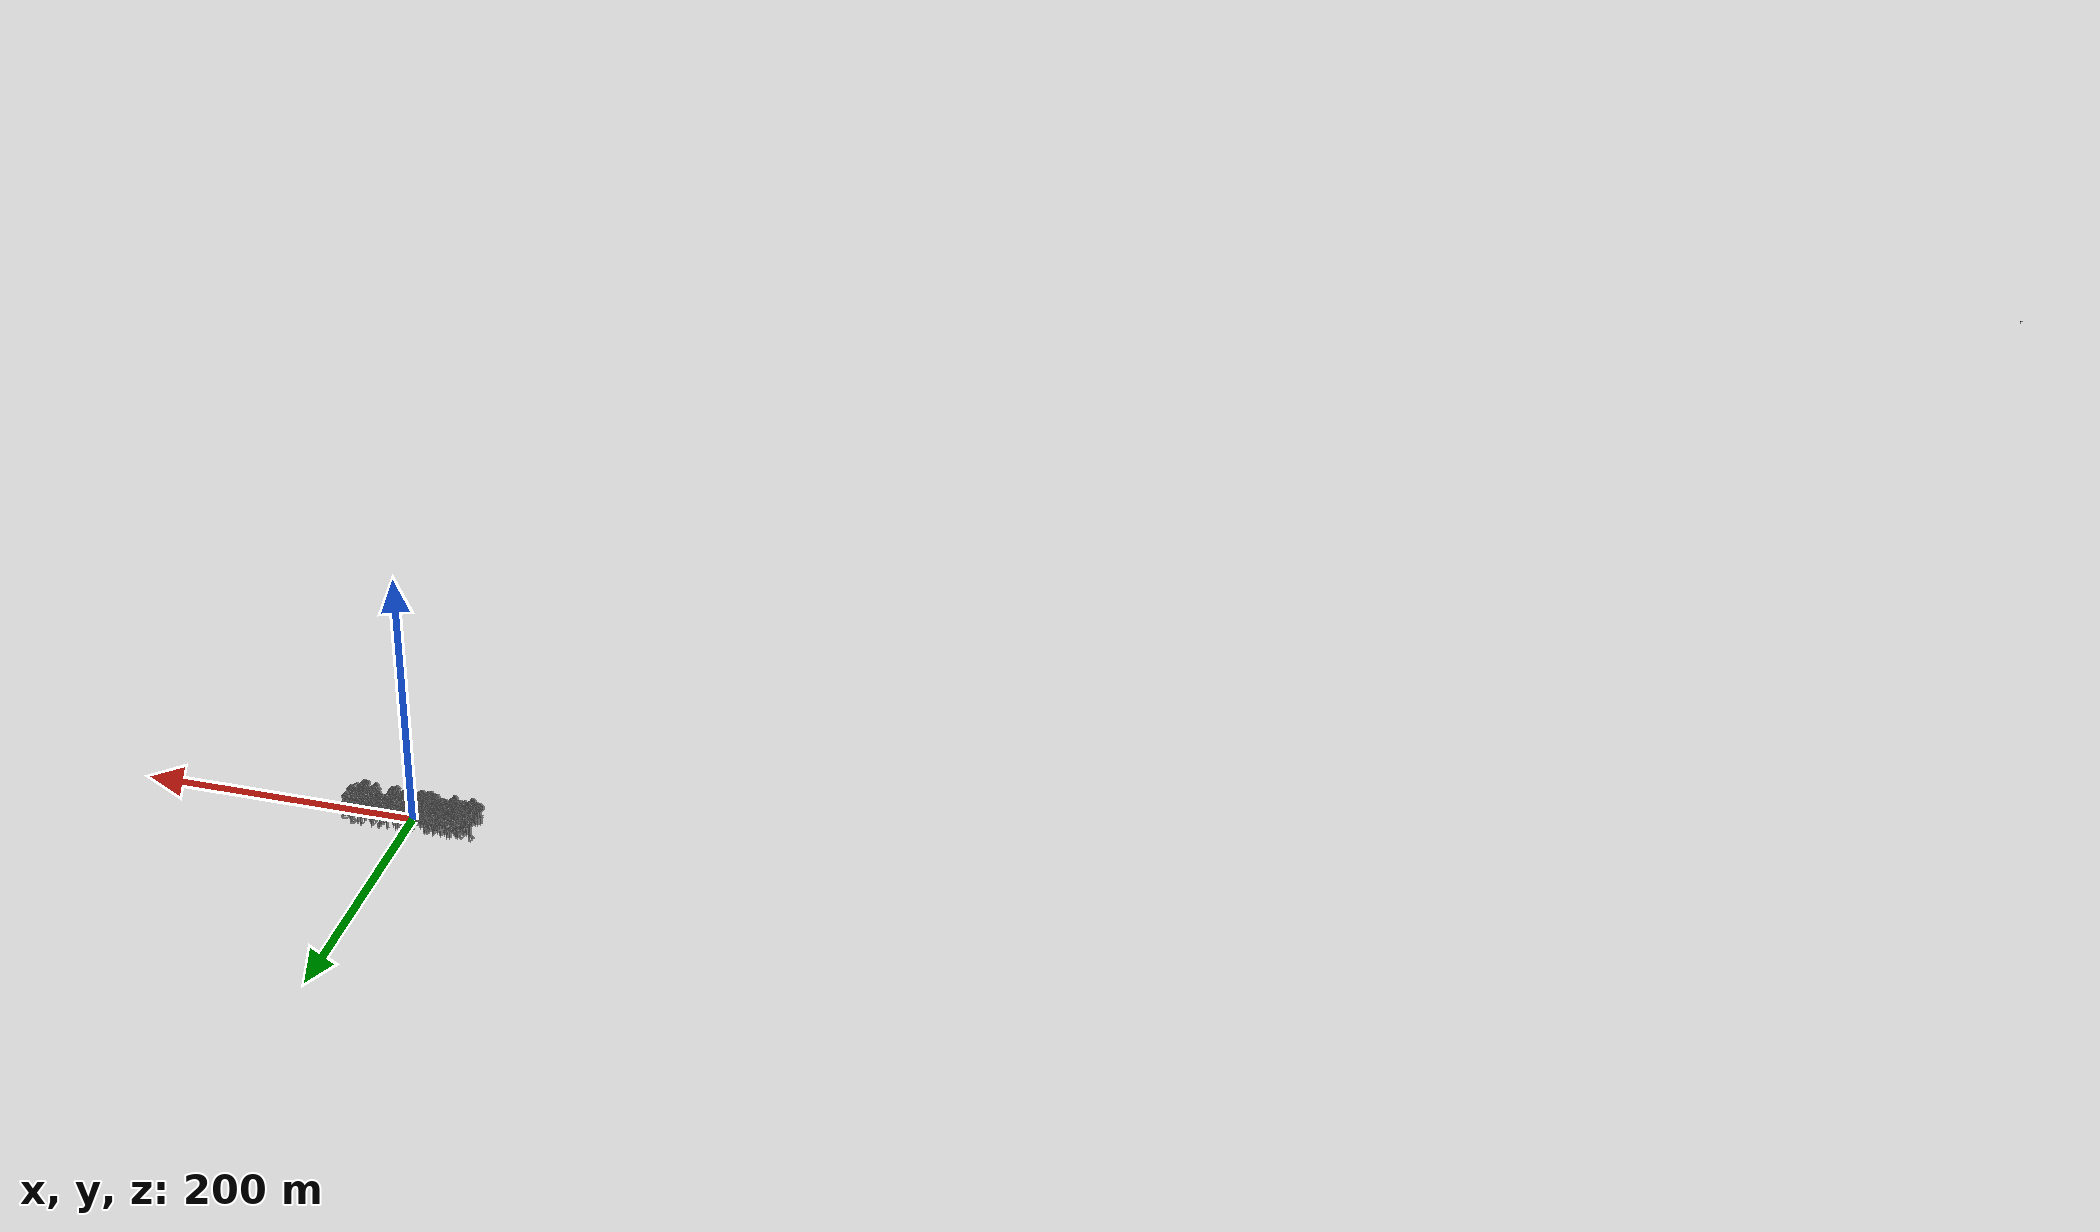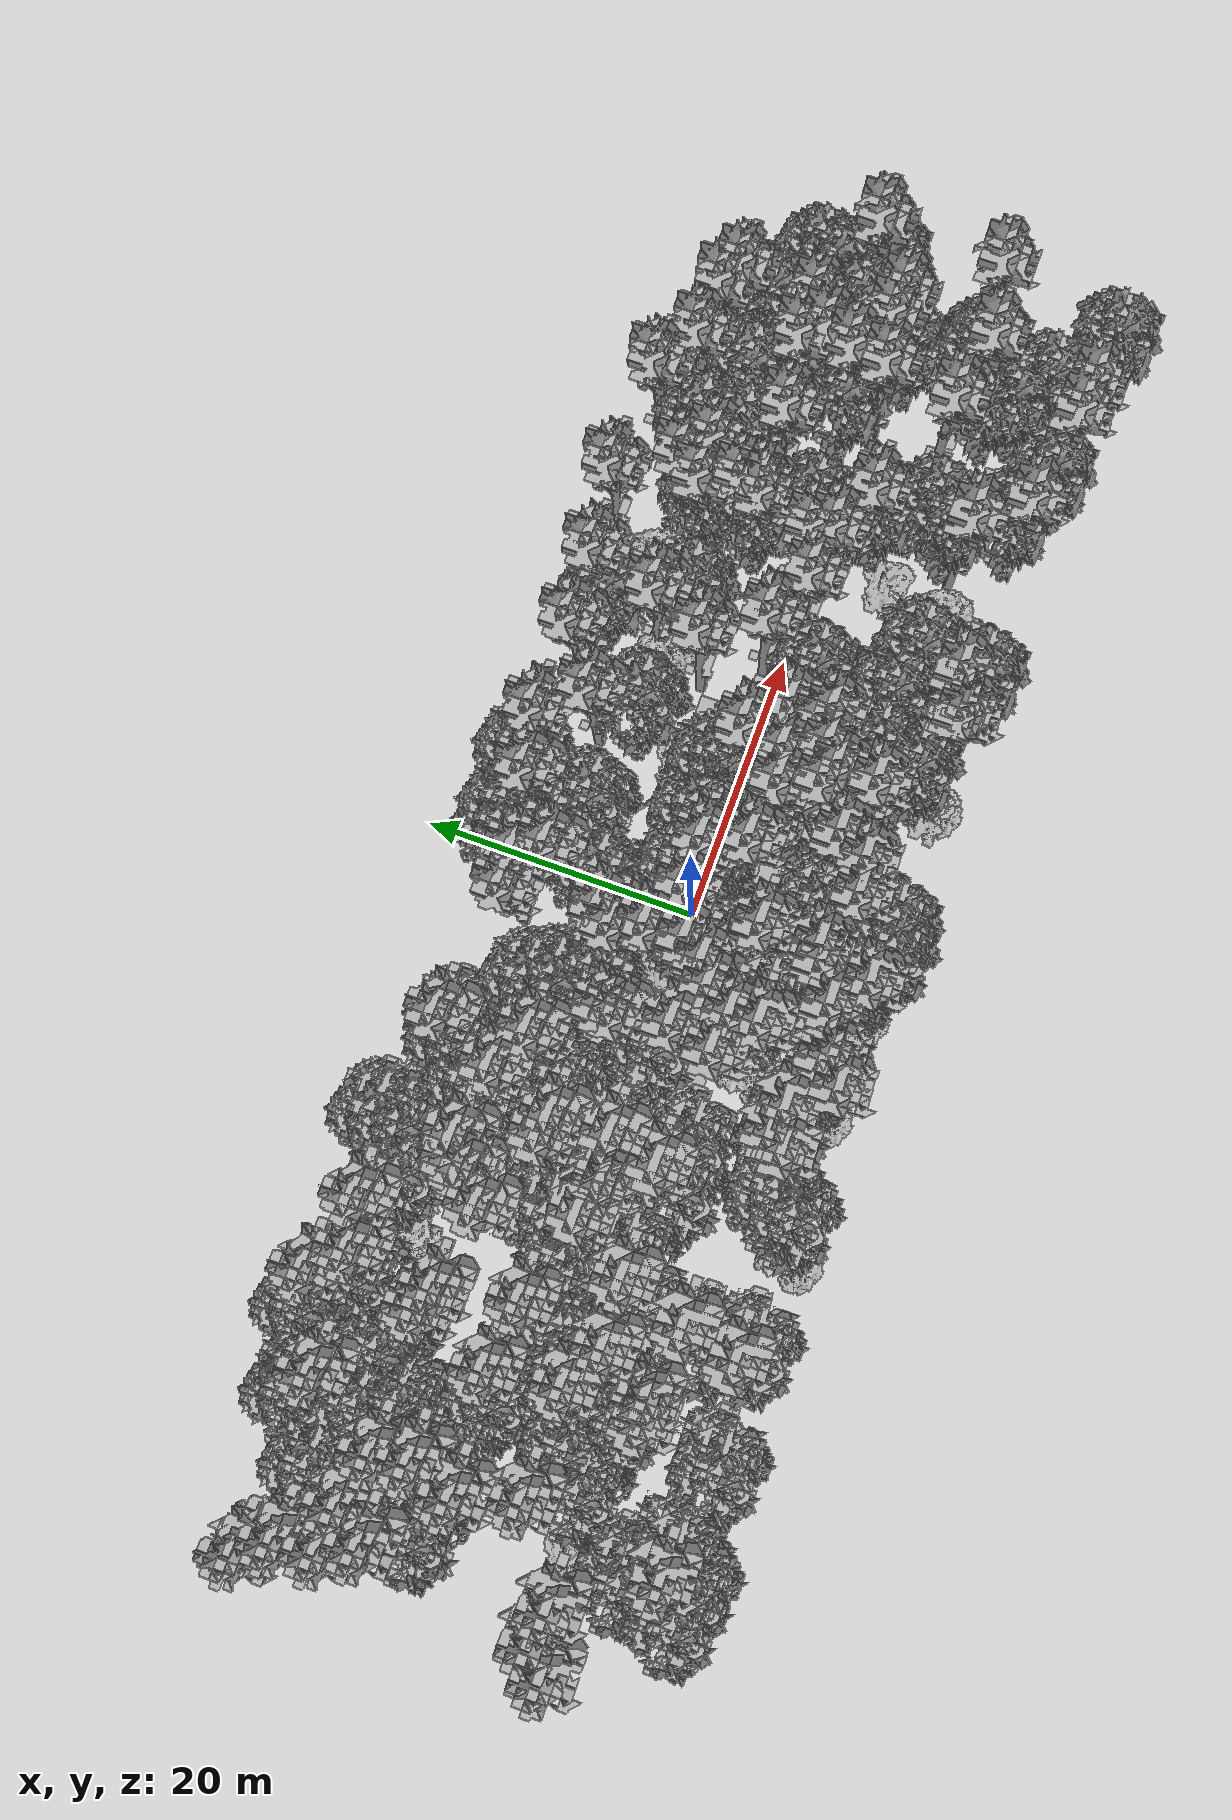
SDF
<sdf version="1.7">
    <world name="default">
        <plugin name="mrs_gazebo_static_transform_republisher_plugin" filename="libMrsGazeboCommonResources_StaticTransformRepublisher.so"/>
        <spherical_coordinates>
            <surface_model>EARTH_WGS84</surface_model>
            <latitude_deg>47.3977</latitude_deg>
            <longitude_deg>8.54559</longitude_deg>
            <elevation>0</elevation>
            <heading_deg>0</heading_deg>
        </spherical_coordinates>
        <physics name="default_physics" default="0" type="ode">
            <ode>
                <solver>
                    <type>quick</type>
                    <iters>10</iters>
                    <sor>1.3</sor>
                    <use_dynamic_moi_rescaling>0</use_dynamic_moi_rescaling>
                </solver>
                <constraints>
                    <cfm>0</cfm>
                    <erp>0.2</erp>
                    <contact_max_correcting_vel>1000</contact_max_correcting_vel>
                    <contact_surface_layer>0.001</contact_surface_layer>
                </constraints>
            </ode>
            <max_step_size>0.004</max_step_size>
            <real_time_factor>1</real_time_factor>
            <real_time_update_rate>250</real_time_update_rate>
        </physics>
        <scene>
            <shadows>0</shadows>
            <ambient>0.4 0.4 0.4 1</ambient>
            <background>0.7 0.7 0.7 1</background>
        </scene>
        <light name="sun" type="directional">
            <pose>0 0 1000 0.4 0.2 0</pose>
            <diffuse>1 1 1 1</diffuse>
            <specular>0.6 0.6 0.6 1</specular>
            <direction>0.1 0.1 -0.9</direction>
            <attenuation>
                <range>20</range>
                <constant>0.5</constant>
                <linear>0.01</linear>
                <quadratic>0.001</quadratic>
            </attenuation>
            <cast_shadows>1</cast_shadows>
            <spot>
                <inner_angle>0</inner_angle>
                <outer_angle>0</outer_angle>
                <falloff>0</falloff>
            </spot>
        </light>
        <model name="ground_plane">
            <static>1</static>
            <link name="link">
                <collision name="collision">
                    <pose>-50 0 0 0 -0 0</pose>
                    <geometry>
                        <plane>
                            <normal>0 0 1</normal>
                            <size>100 100</size>
                        </plane>
                    </geometry>
                    <surface>
                        <contact>
                            <ode>
                                <min_depth>0.01</min_depth>
                                <max_vel>0</max_vel>
                            </ode>
                        </contact>
                        <friction>
                            <ode/>
                            <torsional>
                                <ode/>
                            </torsional>
                        </friction>
                        <bounce/>
                    </surface>
                    <max_contacts>10</max_contacts>
                </collision>
                <visual name="grass">
                    <pose>0 0 0 0 -0 0</pose>
                    <cast_shadows>0</cast_shadows>
                    <geometry>
                        <mesh>
                            <scale>0.5814285714285714 0.18142857142857144 0.1</scale>
                            <uri>file://grass_plane/meshes/grass_plane.dae</uri>
                        </mesh>
                    </geometry>
                </visual>
                <self_collide>0</self_collide>
                <enable_wind>0</enable_wind>
                <kinematic>0</kinematic>
            </link>
        </model>
        <model name="the_void">
            <static>1</static>
            <link name="link">
                <pose>0 0 0.1 0 -0 0</pose>
                <visual name="the_void">
                    <pose>0 0 2 0 -0 0</pose>
                    <geometry>
                        <sphere>
                            <radius>0.25</radius>
                        </sphere>
                    </geometry>
                    <material>
                        <script>
                            <uri>file://media/materials/scripts/Gazebo.material</uri>
                            <name>Gazebo/Black</name>
                        </script>
                    </material>
                </visual>
                <self_collide>0</self_collide>
                <enable_wind>0</enable_wind>
                <kinematic>0</kinematic>
            </link>
            <pose>-1000 -1000 0 0 -0 0</pose>
        </model>
        <gui fullscreen="0">
            <camera name="camera">
                <pose>35.1577 98.6044 40.0204 0 0.407996 -1.99761</pose>
                <view_controller>orbit</view_controller>
                <projection_type>perspective</projection_type>
            </camera>
        </gui>
        <plugin name="mrs_gazebo_rviz_cam_synchronizer" filename="libMrsGazeboCommonResources_RvizCameraSynchronizer.so">
            <target_frame_id>gazebo_user_camera</target_frame_id>
            <world_origin_frame_id>uav1/gps_origin</world_origin_frame_id>
            <frame_to_follow>uav1</frame_to_follow>
        </plugin>
        <gravity>0 0 -9.8066</gravity>
        <magnetic_field>6e-06 2.3e-05 -4.2e-05</magnetic_field>
        <atmosphere type="adiabatic"/>
        <wind/>
        <model name="Tree 0">
            <static>1</static>
            <pose>-9.497331103599258 1.7377793644193638 0 1.57079 -0 0</pose>
            <link name="link">
                <pose>0 0 0 0 -0 0</pose>
                <collision name="collision">
                    <geometry>
                        <mesh>
                            <scale>3.5 5 3.5</scale>
                            <uri>model://tree_9/meshes/tree_9.obj</uri>
                        </mesh>
                    </geometry>
                    <max_contacts>10</max_contacts>
                    <surface>
                        <contact>
                            <ode/>
                        </contact>
                        <bounce/>
                        <friction>
                            <torsional>
                                <ode/>
                            </torsional>
                            <ode/>
                        </friction>
                    </surface>
                </collision>
                <visual name="visual">
                    <geometry>
                        <mesh>
                            <scale>3.5 5 3.5</scale>
                            <uri>model://tree_9/meshes/tree_9.obj</uri>
                        </mesh>
                    </geometry>
                </visual>
                <self_collide>0</self_collide>
                <enable_wind>0</enable_wind>
                <kinematic>0</kinematic>
            </link>
        </model>
        <model name="Tree 1">
            <static>1</static>
            <pose>39.438534800805016 4.661958155739793 0 1.57079 -0 0</pose>
            <link name="link">
                <pose>0 0 0 0 -0 0</pose>
                <collision name="collision">
                    <geometry>
                        <mesh>
                            <scale>3.5 5 3.5</scale>
                            <uri>model://tree_2/meshes/tree_2.obj</uri>
                        </mesh>
                    </geometry>
                    <max_contacts>10</max_contacts>
                    <surface>
                        <contact>
                            <ode/>
                        </contact>
                        <bounce/>
                        <friction>
                            <torsional>
                                <ode/>
                            </torsional>
                            <ode/>
                        </friction>
                    </surface>
                </collision>
                <visual name="visual">
                    <geometry>
                        <mesh>
                            <scale>3.5 5 3.5</scale>
                            <uri>model://tree_2/meshes/tree_2.obj</uri>
                        </mesh>
                    </geometry>
                </visual>
                <self_collide>0</self_collide>
                <enable_wind>0</enable_wind>
                <kinematic>0</kinematic>
            </link>
        </model>
        <model name="Tree 2">
            <static>1</static>
            <pose>-26.45948580254391 -13.488662097697247 0 1.57079 -0 0</pose>
            <link name="link">
                <pose>0 0 0 0 -0 0</pose>
                <collision name="collision">
                    <geometry>
                        <mesh>
                            <scale>3.5 5 3.5</scale>
                            <uri>model://tree_2/meshes/tree_2.obj</uri>
                        </mesh>
                    </geometry>
                    <max_contacts>10</max_contacts>
                    <surface>
                        <contact>
                            <ode/>
                        </contact>
                        <bounce/>
                        <friction>
                            <torsional>
                                <ode/>
                            </torsional>
                            <ode/>
                        </friction>
                    </surface>
                </collision>
                <visual name="visual">
                    <geometry>
                        <mesh>
                            <scale>3.5 5 3.5</scale>
                            <uri>model://tree_2/meshes/tree_2.obj</uri>
                        </mesh>
                    </geometry>
                </visual>
                <self_collide>0</self_collide>
                <enable_wind>0</enable_wind>
                <kinematic>0</kinematic>
            </link>
        </model>
        <model name="Tree 3">
            <static>1</static>
            <pose>17.722591240780247 -2.5185927758991955 0 1.57079 -0 0</pose>
            <link name="link">
                <pose>0 0 0 0 -0 0</pose>
                <collision name="collision">
                    <geometry>
                        <mesh>
                            <scale>3.5 5 3.5</scale>
                            <uri>model://tree_2/meshes/tree_2.obj</uri>
                        </mesh>
                    </geometry>
                    <max_contacts>10</max_contacts>
                    <surface>
                        <contact>
                            <ode/>
                        </contact>
                        <bounce/>
                        <friction>
                            <torsional>
                                <ode/>
                            </torsional>
                            <ode/>
                        </friction>
                    </surface>
                </collision>
                <visual name="visual">
                    <geometry>
                        <mesh>
                            <scale>3.5 5 3.5</scale>
                            <uri>model://tree_2/meshes/tree_2.obj</uri>
                        </mesh>
                    </geometry>
                </visual>
                <self_collide>0</self_collide>
                <enable_wind>0</enable_wind>
                <kinematic>0</kinematic>
            </link>
        </model>
        <model name="Tree 4">
            <static>1</static>
            <pose>-37.860258658787785 12.171442910924156 0 1.57079 -0 0</pose>
            <link name="link">
                <pose>0 0 0 0 -0 0</pose>
                <collision name="collision">
                    <geometry>
                        <mesh>
                            <scale>3.5 5 3.5</scale>
                            <uri>model://tree_2/meshes/tree_2.obj</uri>
                        </mesh>
                    </geometry>
                    <max_contacts>10</max_contacts>
                    <surface>
                        <contact>
                            <ode/>
                        </contact>
                        <bounce/>
                        <friction>
                            <torsional>
                                <ode/>
                            </torsional>
                            <ode/>
                        </friction>
                    </surface>
                </collision>
                <visual name="visual">
                    <geometry>
                        <mesh>
                            <scale>3.5 5 3.5</scale>
                            <uri>model://tree_2/meshes/tree_2.obj</uri>
                        </mesh>
                    </geometry>
                </visual>
                <self_collide>0</self_collide>
                <enable_wind>0</enable_wind>
                <kinematic>0</kinematic>
            </link>
        </model>
        <model name="Tree 5">
            <static>1</static>
            <pose>-5.770280438324974 -3.3481930520723786 0 1.57079 -0 0</pose>
            <link name="link">
                <pose>0 0 0 0 -0 0</pose>
                <collision name="collision">
                    <geometry>
                        <mesh>
                            <scale>3.5 5 3.5</scale>
                            <uri>model://tree_9/meshes/tree_9.obj</uri>
                        </mesh>
                    </geometry>
                    <max_contacts>10</max_contacts>
                    <surface>
                        <contact>
                            <ode/>
                        </contact>
                        <bounce/>
                        <friction>
                            <torsional>
                                <ode/>
                            </torsional>
                            <ode/>
                        </friction>
                    </surface>
                </collision>
                <visual name="visual">
                    <geometry>
                        <mesh>
                            <scale>3.5 5 3.5</scale>
                            <uri>model://tree_9/meshes/tree_9.obj</uri>
                        </mesh>
                    </geometry>
                </visual>
                <self_collide>0</self_collide>
                <enable_wind>0</enable_wind>
                <kinematic>0</kinematic>
            </link>
        </model>
        <model name="Tree 6">
            <static>1</static>
            <pose>5.395262094365876 1.7470312528658738 0 1.57079 -0 0</pose>
            <link name="link">
                <pose>0 0 0 0 -0 0</pose>
                <collision name="collision">
                    <geometry>
                        <mesh>
                            <scale>3.5 5 3.5</scale>
                            <uri>model://tree_2/meshes/tree_2.obj</uri>
                        </mesh>
                    </geometry>
                    <max_contacts>10</max_contacts>
                    <surface>
                        <contact>
                            <ode/>
                        </contact>
                        <bounce/>
                        <friction>
                            <torsional>
                                <ode/>
                            </torsional>
                            <ode/>
                        </friction>
                    </surface>
                </collision>
                <visual name="visual">
                    <geometry>
                        <mesh>
                            <scale>3.5 5 3.5</scale>
                            <uri>model://tree_2/meshes/tree_2.obj</uri>
                        </mesh>
                    </geometry>
                </visual>
                <self_collide>0</self_collide>
                <enable_wind>0</enable_wind>
                <kinematic>0</kinematic>
            </link>
        </model>
        <model name="Tree 7">
            <static>1</static>
            <pose>-26.310678302844597 -8.8970999623425 0 1.57079 -0 0</pose>
            <link name="link">
                <pose>0 0 0 0 -0 0</pose>
                <collision name="collision">
                    <geometry>
                        <mesh>
                            <scale>3.5 5 3.5</scale>
                            <uri>model://tree_9/meshes/tree_9.obj</uri>
                        </mesh>
                    </geometry>
                    <max_contacts>10</max_contacts>
                    <surface>
                        <contact>
                            <ode/>
                        </contact>
                        <bounce/>
                        <friction>
                            <torsional>
                                <ode/>
                            </torsional>
                            <ode/>
                        </friction>
                    </surface>
                </collision>
                <visual name="visual">
                    <geometry>
                        <mesh>
                            <scale>3.5 5 3.5</scale>
                            <uri>model://tree_9/meshes/tree_9.obj</uri>
                        </mesh>
                    </geometry>
                </visual>
                <self_collide>0</self_collide>
                <enable_wind>0</enable_wind>
                <kinematic>0</kinematic>
            </link>
        </model>
        <model name="Tree 8">
            <static>1</static>
            <pose>1.928067051756159 -8.094480789666445 0 1.57079 -0 0</pose>
            <link name="link">
                <pose>0 0 0 0 -0 0</pose>
                <collision name="collision">
                    <geometry>
                        <mesh>
                            <scale>3.5 5 3.5</scale>
                            <uri>model://tree_2/meshes/tree_2.obj</uri>
                        </mesh>
                    </geometry>
                    <max_contacts>10</max_contacts>
                    <surface>
                        <contact>
                            <ode/>
                        </contact>
                        <bounce/>
                        <friction>
                            <torsional>
                                <ode/>
                            </torsional>
                            <ode/>
                        </friction>
                    </surface>
                </collision>
                <visual name="visual">
                    <geometry>
                        <mesh>
                            <scale>3.5 5 3.5</scale>
                            <uri>model://tree_2/meshes/tree_2.obj</uri>
                        </mesh>
                    </geometry>
                </visual>
                <self_collide>0</self_collide>
                <enable_wind>0</enable_wind>
                <kinematic>0</kinematic>
            </link>
        </model>
        <model name="Tree 9">
            <static>1</static>
            <pose>43.24993066943506 -5.576055386693405 0 1.57079 -0 0</pose>
            <link name="link">
                <pose>0 0 0 0 -0 0</pose>
                <collision name="collision">
                    <geometry>
                        <mesh>
                            <scale>3.5 5 3.5</scale>
                            <uri>model://tree_2/meshes/tree_2.obj</uri>
                        </mesh>
                    </geometry>
                    <max_contacts>10</max_contacts>
                    <surface>
                        <contact>
                            <ode/>
                        </contact>
                        <bounce/>
                        <friction>
                            <torsional>
                                <ode/>
                            </torsional>
                            <ode/>
                        </friction>
                    </surface>
                </collision>
                <visual name="visual">
                    <geometry>
                        <mesh>
                            <scale>3.5 5 3.5</scale>
                            <uri>model://tree_2/meshes/tree_2.obj</uri>
                        </mesh>
                    </geometry>
                </visual>
                <self_collide>0</self_collide>
                <enable_wind>0</enable_wind>
                <kinematic>0</kinematic>
            </link>
        </model>
        <model name="Tree 10">
            <static>1</static>
            <pose>-6.427290292997256 -9.65219543196185 0 1.57079 -0 0</pose>
            <link name="link">
                <pose>0 0 0 0 -0 0</pose>
                <collision name="collision">
                    <geometry>
                        <mesh>
                            <scale>3.5 5 3.5</scale>
                            <uri>model://tree_2/meshes/tree_2.obj</uri>
                        </mesh>
                    </geometry>
                    <max_contacts>10</max_contacts>
                    <surface>
                        <contact>
                            <ode/>
                        </contact>
                        <bounce/>
                        <friction>
                            <torsional>
                                <ode/>
                            </torsional>
                            <ode/>
                        </friction>
                    </surface>
                </collision>
                <visual name="visual">
                    <geometry>
                        <mesh>
                            <scale>3.5 5 3.5</scale>
                            <uri>model://tree_2/meshes/tree_2.obj</uri>
                        </mesh>
                    </geometry>
                </visual>
                <self_collide>0</self_collide>
                <enable_wind>0</enable_wind>
                <kinematic>0</kinematic>
            </link>
        </model>
        <model name="Tree 11">
            <static>1</static>
            <pose>-11.699976823902972 -10.894039608267878 0 1.57079 -0 0</pose>
            <link name="link">
                <pose>0 0 0 0 -0 0</pose>
                <collision name="collision">
                    <geometry>
                        <mesh>
                            <scale>3.5 5 3.5</scale>
                            <uri>model://tree_2/meshes/tree_2.obj</uri>
                        </mesh>
                    </geometry>
                    <max_contacts>10</max_contacts>
                    <surface>
                        <contact>
                            <ode/>
                        </contact>
                        <bounce/>
                        <friction>
                            <torsional>
                                <ode/>
                            </torsional>
                            <ode/>
                        </friction>
                    </surface>
                </collision>
                <visual name="visual">
                    <geometry>
                        <mesh>
                            <scale>3.5 5 3.5</scale>
                            <uri>model://tree_2/meshes/tree_2.obj</uri>
                        </mesh>
                    </geometry>
                </visual>
                <self_collide>0</self_collide>
                <enable_wind>0</enable_wind>
                <kinematic>0</kinematic>
            </link>
        </model>
        <model name="Tree 12">
            <static>1</static>
            <pose>5.316116097098707 -11.90297776175353 0 1.57079 -0 0</pose>
            <link name="link">
                <pose>0 0 0 0 -0 0</pose>
                <collision name="collision">
                    <geometry>
                        <mesh>
                            <scale>4 2.5 4</scale>
                            <uri>model://tree_1/meshes/tree_1.obj</uri>
                        </mesh>
                    </geometry>
                    <max_contacts>10</max_contacts>
                    <surface>
                        <contact>
                            <ode/>
                        </contact>
                        <bounce/>
                        <friction>
                            <torsional>
                                <ode/>
                            </torsional>
                            <ode/>
                        </friction>
                    </surface>
                </collision>
                <visual name="visual">
                    <geometry>
                        <mesh>
                            <scale>4 2.5 4</scale>
                            <uri>model://tree_1/meshes/tree_1.obj</uri>
                        </mesh>
                    </geometry>
                </visual>
                <self_collide>0</self_collide>
                <enable_wind>0</enable_wind>
                <kinematic>0</kinematic>
            </link>
        </model>
        <model name="Tree 13">
            <static>1</static>
            <pose>2.4962927978569525 -13.172962160027453 0 1.57079 -0 0</pose>
            <link name="link">
                <pose>0 0 0 0 -0 0</pose>
                <collision name="collision">
                    <geometry>
                        <mesh>
                            <scale>3.5 5 3.5</scale>
                            <uri>model://tree_2/meshes/tree_2.obj</uri>
                        </mesh>
                    </geometry>
                    <max_contacts>10</max_contacts>
                    <surface>
                        <contact>
                            <ode/>
                        </contact>
                        <bounce/>
                        <friction>
                            <torsional>
                                <ode/>
                            </torsional>
                            <ode/>
                        </friction>
                    </surface>
                </collision>
                <visual name="visual">
                    <geometry>
                        <mesh>
                            <scale>3.5 5 3.5</scale>
                            <uri>model://tree_2/meshes/tree_2.obj</uri>
                        </mesh>
                    </geometry>
                </visual>
                <self_collide>0</self_collide>
                <enable_wind>0</enable_wind>
                <kinematic>0</kinematic>
            </link>
        </model>
        <model name="Tree 14">
            <static>1</static>
            <pose>-44.75034069485515 4.949931277231471 0 1.57079 -0 0</pose>
            <link name="link">
                <pose>0 0 0 0 -0 0</pose>
                <collision name="collision">
                    <geometry>
                        <mesh>
                            <scale>3.5 5 3.5</scale>
                            <uri>model://tree_9/meshes/tree_9.obj</uri>
                        </mesh>
                    </geometry>
                    <max_contacts>10</max_contacts>
                    <surface>
                        <contact>
                            <ode/>
                        </contact>
                        <bounce/>
                        <friction>
                            <torsional>
                                <ode/>
                            </torsional>
                            <ode/>
                        </friction>
                    </surface>
                </collision>
                <visual name="visual">
                    <geometry>
                        <mesh>
                            <scale>3.5 5 3.5</scale>
                            <uri>model://tree_9/meshes/tree_9.obj</uri>
                        </mesh>
                    </geometry>
                </visual>
                <self_collide>0</self_collide>
                <enable_wind>0</enable_wind>
                <kinematic>0</kinematic>
            </link>
        </model>
        <model name="Tree 15">
            <static>1</static>
            <pose>-37.89983773162189 2.2039727767756325 0 1.57079 -0 0</pose>
            <link name="link">
                <pose>0 0 0 0 -0 0</pose>
                <collision name="collision">
                    <geometry>
                        <mesh>
                            <scale>3.5 5 3.5</scale>
                            <uri>model://tree_2/meshes/tree_2.obj</uri>
                        </mesh>
                    </geometry>
                    <max_contacts>10</max_contacts>
                    <surface>
                        <contact>
                            <ode/>
                        </contact>
                        <bounce/>
                        <friction>
                            <torsional>
                                <ode/>
                            </torsional>
                            <ode/>
                        </friction>
                    </surface>
                </collision>
                <visual name="visual">
                    <geometry>
                        <mesh>
                            <scale>3.5 5 3.5</scale>
                            <uri>model://tree_2/meshes/tree_2.obj</uri>
                        </mesh>
                    </geometry>
                </visual>
                <self_collide>0</self_collide>
                <enable_wind>0</enable_wind>
                <kinematic>0</kinematic>
            </link>
        </model>
        <model name="Tree 16">
            <static>1</static>
            <pose>-41.636838350007686 7.191071305497637 0 1.57079 -0 0</pose>
            <link name="link">
                <pose>0 0 0 0 -0 0</pose>
                <collision name="collision">
                    <geometry>
                        <mesh>
                            <scale>4 2.5 4</scale>
                            <uri>model://tree_1/meshes/tree_1.obj</uri>
                        </mesh>
                    </geometry>
                    <max_contacts>10</max_contacts>
                    <surface>
                        <contact>
                            <ode/>
                        </contact>
                        <bounce/>
                        <friction>
                            <torsional>
                                <ode/>
                            </torsional>
                            <ode/>
                        </friction>
                    </surface>
                </collision>
                <visual name="visual">
                    <geometry>
                        <mesh>
                            <scale>4 2.5 4</scale>
                            <uri>model://tree_1/meshes/tree_1.obj</uri>
                        </mesh>
                    </geometry>
                </visual>
                <self_collide>0</self_collide>
                <enable_wind>0</enable_wind>
                <kinematic>0</kinematic>
            </link>
        </model>
        <model name="Tree 17">
            <static>1</static>
            <pose>-18.04329894086951 -1.0568003276767577 0 1.57079 -0 0</pose>
            <link name="link">
                <pose>0 0 0 0 -0 0</pose>
                <collision name="collision">
                    <geometry>
                        <mesh>
                            <scale>3.5 5 3.5</scale>
                            <uri>model://tree_2/meshes/tree_2.obj</uri>
                        </mesh>
                    </geometry>
                    <max_contacts>10</max_contacts>
                    <surface>
                        <contact>
                            <ode/>
                        </contact>
                        <bounce/>
                        <friction>
                            <torsional>
                                <ode/>
                            </torsional>
                            <ode/>
                        </friction>
                    </surface>
                </collision>
                <visual name="visual">
                    <geometry>
                        <mesh>
                            <scale>3.5 5 3.5</scale>
                            <uri>model://tree_2/meshes/tree_2.obj</uri>
                        </mesh>
                    </geometry>
                </visual>
                <self_collide>0</self_collide>
                <enable_wind>0</enable_wind>
                <kinematic>0</kinematic>
            </link>
        </model>
        <model name="Tree 18">
            <static>1</static>
            <pose>-32.004453880624155 -3.203963583699915 0 1.57079 -0 0</pose>
            <link name="link">
                <pose>0 0 0 0 -0 0</pose>
                <collision name="collision">
                    <geometry>
                        <mesh>
                            <scale>3.5 5 3.5</scale>
                            <uri>model://tree_9/meshes/tree_9.obj</uri>
                        </mesh>
                    </geometry>
                    <max_contacts>10</max_contacts>
                    <surface>
                        <contact>
                            <ode/>
                        </contact>
                        <bounce/>
                        <friction>
                            <torsional>
                                <ode/>
                            </torsional>
                            <ode/>
                        </friction>
                    </surface>
                </collision>
                <visual name="visual">
                    <geometry>
                        <mesh>
                            <scale>3.5 5 3.5</scale>
                            <uri>model://tree_9/meshes/tree_9.obj</uri>
                        </mesh>
                    </geometry>
                </visual>
                <self_collide>0</self_collide>
                <enable_wind>0</enable_wind>
                <kinematic>0</kinematic>
            </link>
        </model>
        <model name="Tree 19">
            <static>1</static>
            <pose>-43.50208777569813 -7.198003721392618 0 1.57079 -0 0</pose>
            <link name="link">
                <pose>0 0 0 0 -0 0</pose>
                <collision name="collision">
                    <geometry>
                        <mesh>
                            <scale>3 2 3</scale>
                            <uri>model://tree_3/meshes/tree_3.obj</uri>
                        </mesh>
                    </geometry>
                    <max_contacts>10</max_contacts>
                    <surface>
                        <contact>
                            <ode/>
                        </contact>
                        <bounce/>
                        <friction>
                            <torsional>
                                <ode/>
                            </torsional>
                            <ode/>
                        </friction>
                    </surface>
                </collision>
                <visual name="visual">
                    <geometry>
                        <mesh>
                            <scale>3 2 3</scale>
                            <uri>model://tree_3/meshes/tree_3.obj</uri>
                        </mesh>
                    </geometry>
                </visual>
                <self_collide>0</self_collide>
                <enable_wind>0</enable_wind>
                <kinematic>0</kinematic>
            </link>
        </model>
        <model name="Tree 20">
            <static>1</static>
            <pose>16.454242641067495 -12.793850651289368 0 1.57079 -0 0</pose>
            <link name="link">
                <pose>0 0 0 0 -0 0</pose>
                <collision name="collision">
                    <geometry>
                        <mesh>
                            <scale>3.5 5 3.5</scale>
                            <uri>model://tree_9/meshes/tree_9.obj</uri>
                        </mesh>
                    </geometry>
                    <max_contacts>10</max_contacts>
                    <surface>
                        <contact>
                            <ode/>
                        </contact>
                        <bounce/>
                        <friction>
                            <torsional>
                                <ode/>
                            </torsional>
                            <ode/>
                        </friction>
                    </surface>
                </collision>
                <visual name="visual">
                    <geometry>
                        <mesh>
                            <scale>3.5 5 3.5</scale>
                            <uri>model://tree_9/meshes/tree_9.obj</uri>
                        </mesh>
                    </geometry>
                </visual>
                <self_collide>0</self_collide>
                <enable_wind>0</enable_wind>
                <kinematic>0</kinematic>
            </link>
        </model>
        <model name="Tree 21">
            <static>1</static>
            <pose>47.174540948818844 7.239426667694268 0 1.57079 -0 0</pose>
            <link name="link">
                <pose>0 0 0 0 -0 0</pose>
                <collision name="collision">
                    <geometry>
                        <mesh>
                            <scale>3.5 5 3.5</scale>
                            <uri>model://tree_2/meshes/tree_2.obj</uri>
                        </mesh>
                    </geometry>
                    <max_contacts>10</max_contacts>
                    <surface>
                        <contact>
                            <ode/>
                        </contact>
                        <bounce/>
                        <friction>
                            <torsional>
                                <ode/>
                            </torsional>
                            <ode/>
                        </friction>
                    </surface>
                </collision>
                <visual name="visual">
                    <geometry>
                        <mesh>
                            <scale>3.5 5 3.5</scale>
                            <uri>model://tree_2/meshes/tree_2.obj</uri>
                        </mesh>
                    </geometry>
                </visual>
                <self_collide>0</self_collide>
                <enable_wind>0</enable_wind>
                <kinematic>0</kinematic>
            </link>
        </model>
        <model name="Tree 22">
            <static>1</static>
            <pose>-40.57744656535178 -12.582310519198732 0 1.57079 -0 0</pose>
            <link name="link">
                <pose>0 0 0 0 -0 0</pose>
                <collision name="collision">
                    <geometry>
                        <mesh>
                            <scale>3.5 5 3.5</scale>
                            <uri>model://tree_9/meshes/tree_9.obj</uri>
                        </mesh>
                    </geometry>
                    <max_contacts>10</max_contacts>
                    <surface>
                        <contact>
                            <ode/>
                        </contact>
                        <bounce/>
                        <friction>
                            <torsional>
                                <ode/>
                            </torsional>
                            <ode/>
                        </friction>
                    </surface>
                </collision>
                <visual name="visual">
                    <geometry>
                        <mesh>
                            <scale>3.5 5 3.5</scale>
                            <uri>model://tree_9/meshes/tree_9.obj</uri>
                        </mesh>
                    </geometry>
                </visual>
                <self_collide>0</self_collide>
                <enable_wind>0</enable_wind>
                <kinematic>0</kinematic>
            </link>
        </model>
        <model name="Tree 23">
            <static>1</static>
            <pose>31.78843503341058 -6.538116669138439 0 1.57079 -0 0</pose>
            <link name="link">
                <pose>0 0 0 0 -0 0</pose>
                <collision name="collision">
                    <geometry>
                        <mesh>
                            <scale>3.5 5 3.5</scale>
                            <uri>model://tree_2/meshes/tree_2.obj</uri>
                        </mesh>
                    </geometry>
                    <max_contacts>10</max_contacts>
                    <surface>
                        <contact>
                            <ode/>
                        </contact>
                        <bounce/>
                        <friction>
                            <torsional>
                                <ode/>
                            </torsional>
                            <ode/>
                        </friction>
                    </surface>
                </collision>
                <visual name="visual">
                    <geometry>
                        <mesh>
                            <scale>3.5 5 3.5</scale>
                            <uri>model://tree_2/meshes/tree_2.obj</uri>
                        </mesh>
                    </geometry>
                </visual>
                <self_collide>0</self_collide>
                <enable_wind>0</enable_wind>
                <kinematic>0</kinematic>
            </link>
        </model>
        <model name="Tree 24">
            <static>1</static>
            <pose>27.602788038337465 -5.3436573824634 0 1.57079 -0 0</pose>
            <link name="link">
                <pose>0 0 0 0 -0 0</pose>
                <collision name="collision">
                    <geometry>
                        <mesh>
                            <scale>3 2 3</scale>
                            <uri>model://tree_3/meshes/tree_3.obj</uri>
                        </mesh>
                    </geometry>
                    <max_contacts>10</max_contacts>
                    <surface>
                        <contact>
                            <ode/>
                        </contact>
                        <bounce/>
                        <friction>
                            <torsional>
                                <ode/>
                            </torsional>
                            <ode/>
                        </friction>
                    </surface>
                </collision>
                <visual name="visual">
                    <geometry>
                        <mesh>
                            <scale>3 2 3</scale>
                            <uri>model://tree_3/meshes/tree_3.obj</uri>
                        </mesh>
                    </geometry>
                </visual>
                <self_collide>0</self_collide>
                <enable_wind>0</enable_wind>
                <kinematic>0</kinematic>
            </link>
        </model>
        <model name="Tree 25">
            <static>1</static>
            <pose>0.5691270658067111 -13.588676001851574 0 1.57079 -0 0</pose>
            <link name="link">
                <pose>0 0 0 0 -0 0</pose>
                <collision name="collision">
                    <geometry>
                        <mesh>
                            <scale>3.5 5 3.5</scale>
                            <uri>model://tree_2/meshes/tree_2.obj</uri>
                        </mesh>
                    </geometry>
                    <max_contacts>10</max_contacts>
                    <surface>
                        <contact>
                            <ode/>
                        </contact>
                        <bounce/>
                        <friction>
                            <torsional>
                                <ode/>
                            </torsional>
                            <ode/>
                        </friction>
                    </surface>
                </collision>
                <visual name="visual">
                    <geometry>
                        <mesh>
                            <scale>3.5 5 3.5</scale>
                            <uri>model://tree_2/meshes/tree_2.obj</uri>
                        </mesh>
                    </geometry>
                </visual>
                <self_collide>0</self_collide>
                <enable_wind>0</enable_wind>
                <kinematic>0</kinematic>
            </link>
        </model>
        <model name="Tree 26">
            <static>1</static>
            <pose>16.46781186742119 5.183758551244221 0 1.57079 -0 0</pose>
            <link name="link">
                <pose>0 0 0 0 -0 0</pose>
                <collision name="collision">
                    <geometry>
                        <mesh>
                            <scale>3.5 5 3.5</scale>
                            <uri>model://tree_9/meshes/tree_9.obj</uri>
                        </mesh>
                    </geometry>
                    <max_contacts>10</max_contacts>
                    <surface>
                        <contact>
                            <ode/>
                        </contact>
                        <bounce/>
                        <friction>
                            <torsional>
                                <ode/>
                            </torsional>
                            <ode/>
                        </friction>
                    </surface>
                </collision>
                <visual name="visual">
                    <geometry>
                        <mesh>
                            <scale>3.5 5 3.5</scale>
                            <uri>model://tree_9/meshes/tree_9.obj</uri>
                        </mesh>
                    </geometry>
                </visual>
                <self_collide>0</self_collide>
                <enable_wind>0</enable_wind>
                <kinematic>0</kinematic>
            </link>
        </model>
        <model name="Tree 27">
            <static>1</static>
            <pose>-2.034383786363911 0.4205439793284995 0 1.57079 -0 0</pose>
            <link name="link">
                <pose>0 0 0 0 -0 0</pose>
                <collision name="collision">
                    <geometry>
                        <mesh>
                            <scale>3.5 5 3.5</scale>
                            <uri>model://tree_2/meshes/tree_2.obj</uri>
                        </mesh>
                    </geometry>
                    <max_contacts>10</max_contacts>
                    <surface>
                        <contact>
                            <ode/>
                        </contact>
                        <bounce/>
                        <friction>
                            <torsional>
                                <ode/>
                            </torsional>
                            <ode/>
                        </friction>
                    </surface>
                </collision>
                <visual name="visual">
                    <geometry>
                        <mesh>
                            <scale>3.5 5 3.5</scale>
                            <uri>model://tree_2/meshes/tree_2.obj</uri>
                        </mesh>
                    </geometry>
                </visual>
                <self_collide>0</self_collide>
                <enable_wind>0</enable_wind>
                <kinematic>0</kinematic>
            </link>
        </model>
        <model name="Tree 28">
            <static>1</static>
            <pose>48.171285346727814 9.23360146076735 0 1.57079 -0 0</pose>
            <link name="link">
                <pose>0 0 0 0 -0 0</pose>
                <collision name="collision">
                    <geometry>
                        <mesh>
                            <scale>3 2 3</scale>
                            <uri>model://tree_3/meshes/tree_3.obj</uri>
                        </mesh>
                    </geometry>
                    <max_contacts>10</max_contacts>
                    <surface>
                        <contact>
                            <ode/>
                        </contact>
                        <bounce/>
                        <friction>
                            <torsional>
                                <ode/>
                            </torsional>
                            <ode/>
                        </friction>
                    </surface>
                </collision>
                <visual name="visual">
                    <geometry>
                        <mesh>
                            <scale>3 2 3</scale>
                            <uri>model://tree_3/meshes/tree_3.obj</uri>
                        </mesh>
                    </geometry>
                </visual>
                <self_collide>0</self_collide>
                <enable_wind>0</enable_wind>
                <kinematic>0</kinematic>
            </link>
        </model>
        <model name="Tree 29">
            <static>1</static>
            <pose>10.450314175094896 -6.321341003616984 0 1.57079 -0 0</pose>
            <link name="link">
                <pose>0 0 0 0 -0 0</pose>
                <collision name="collision">
                    <geometry>
                        <mesh>
                            <scale>3.5 5 3.5</scale>
                            <uri>model://tree_9/meshes/tree_9.obj</uri>
                        </mesh>
                    </geometry>
                    <max_contacts>10</max_contacts>
                    <surface>
                        <contact>
                            <ode/>
                        </contact>
                        <bounce/>
                        <friction>
                            <torsional>
                                <ode/>
                            </torsional>
                            <ode/>
                        </friction>
                    </surface>
                </collision>
                <visual name="visual">
                    <geometry>
                        <mesh>
                            <scale>3.5 5 3.5</scale>
                            <uri>model://tree_9/meshes/tree_9.obj</uri>
                        </mesh>
                    </geometry>
                </visual>
                <self_collide>0</self_collide>
                <enable_wind>0</enable_wind>
                <kinematic>0</kinematic>
            </link>
        </model>
        <model name="Tree 30">
            <static>1</static>
            <pose>-46.451018027933905 -6.5726264874756755 0 1.57079 -0 0</pose>
            <link name="link">
                <pose>0 0 0 0 -0 0</pose>
                <collision name="collision">
                    <geometry>
                        <mesh>
                            <scale>3.5 5 3.5</scale>
                            <uri>model://tree_9/meshes/tree_9.obj</uri>
                        </mesh>
                    </geometry>
                    <max_contacts>10</max_contacts>
                    <surface>
                        <contact>
                            <ode/>
                        </contact>
                        <bounce/>
                        <friction>
                            <torsional>
                                <ode/>
                            </torsional>
                            <ode/>
                        </friction>
                    </surface>
                </collision>
                <visual name="visual">
                    <geometry>
                        <mesh>
                            <scale>3.5 5 3.5</scale>
                            <uri>model://tree_9/meshes/tree_9.obj</uri>
                        </mesh>
                    </geometry>
                </visual>
                <self_collide>0</self_collide>
                <enable_wind>0</enable_wind>
                <kinematic>0</kinematic>
            </link>
        </model>
        <model name="Tree 31">
            <static>1</static>
            <pose>0.11112618233485705 -7.958130080903205 0 1.57079 -0 0</pose>
            <link name="link">
                <pose>0 0 0 0 -0 0</pose>
                <collision name="collision">
                    <geometry>
                        <mesh>
                            <scale>3.5 5 3.5</scale>
                            <uri>model://tree_2/meshes/tree_2.obj</uri>
                        </mesh>
                    </geometry>
                    <max_contacts>10</max_contacts>
                    <surface>
                        <contact>
                            <ode/>
                        </contact>
                        <bounce/>
                        <friction>
                            <torsional>
                                <ode/>
                            </torsional>
                            <ode/>
                        </friction>
                    </surface>
                </collision>
                <visual name="visual">
                    <geometry>
                        <mesh>
                            <scale>3.5 5 3.5</scale>
                            <uri>model://tree_2/meshes/tree_2.obj</uri>
                        </mesh>
                    </geometry>
                </visual>
                <self_collide>0</self_collide>
                <enable_wind>0</enable_wind>
                <kinematic>0</kinematic>
            </link>
        </model>
        <model name="Tree 32">
            <static>1</static>
            <pose>-14.664122695703682 11.285026428368614 0 1.57079 -0 0</pose>
            <link name="link">
                <pose>0 0 0 0 -0 0</pose>
                <collision name="collision">
                    <geometry>
                        <mesh>
                            <scale>3.5 5 3.5</scale>
                            <uri>model://tree_2/meshes/tree_2.obj</uri>
                        </mesh>
                    </geometry>
                    <max_contacts>10</max_contacts>
                    <surface>
                        <contact>
                            <ode/>
                        </contact>
                        <bounce/>
                        <friction>
                            <torsional>
                                <ode/>
                            </torsional>
                            <ode/>
                        </friction>
                    </surface>
                </collision>
                <visual name="visual">
                    <geometry>
                        <mesh>
                            <scale>3.5 5 3.5</scale>
                            <uri>model://tree_2/meshes/tree_2.obj</uri>
                        </mesh>
                    </geometry>
                </visual>
                <self_collide>0</self_collide>
                <enable_wind>0</enable_wind>
                <kinematic>0</kinematic>
            </link>
        </model>
        <model name="Tree 33">
            <static>1</static>
            <pose>-14.378093770031185 11.09797481008357 0 1.57079 -0 0</pose>
            <link name="link">
                <pose>0 0 0 0 -0 0</pose>
                <collision name="collision">
                    <geometry>
                        <mesh>
                            <scale>4 2.5 4</scale>
                            <uri>model://tree_1/meshes/tree_1.obj</uri>
                        </mesh>
                    </geometry>
                    <max_contacts>10</max_contacts>
                    <surface>
                        <contact>
                            <ode/>
                        </contact>
                        <bounce/>
                        <friction>
                            <torsional>
                                <ode/>
                            </torsional>
                            <ode/>
                        </friction>
                    </surface>
                </collision>
                <visual name="visual">
                    <geometry>
                        <mesh>
                            <scale>4 2.5 4</scale>
                            <uri>model://tree_1/meshes/tree_1.obj</uri>
                        </mesh>
                    </geometry>
                </visual>
                <self_collide>0</self_collide>
                <enable_wind>0</enable_wind>
                <kinematic>0</kinematic>
            </link>
        </model>
        <model name="Tree 34">
            <static>1</static>
            <pose>27.09267132470289 -9.83745168477164 0 1.57079 -0 0</pose>
            <link name="link">
                <pose>0 0 0 0 -0 0</pose>
                <collision name="collision">
                    <geometry>
                        <mesh>
                            <scale>4 2.5 4</scale>
                            <uri>model://tree_1/meshes/tree_1.obj</uri>
                        </mesh>
                    </geometry>
                    <max_contacts>10</max_contacts>
                    <surface>
                        <contact>
                            <ode/>
                        </contact>
                        <bounce/>
                        <friction>
                            <torsional>
                                <ode/>
                            </torsional>
                            <ode/>
                        </friction>
                    </surface>
                </collision>
                <visual name="visual">
                    <geometry>
                        <mesh>
                            <scale>4 2.5 4</scale>
                            <uri>model://tree_1/meshes/tree_1.obj</uri>
                        </mesh>
                    </geometry>
                </visual>
                <self_collide>0</self_collide>
                <enable_wind>0</enable_wind>
                <kinematic>0</kinematic>
            </link>
        </model>
        <model name="Tree 35">
            <static>1</static>
            <pose>19.354249676947177 13.855078429910566 0 1.57079 -0 0</pose>
            <link name="link">
                <pose>0 0 0 0 -0 0</pose>
                <collision name="collision">
                    <geometry>
                        <mesh>
                            <scale>3.5 5 3.5</scale>
                            <uri>model://tree_9/meshes/tree_9.obj</uri>
                        </mesh>
                    </geometry>
                    <max_contacts>10</max_contacts>
                    <surface>
                        <contact>
                            <ode/>
                        </contact>
                        <bounce/>
                        <friction>
                            <torsional>
                                <ode/>
                            </torsional>
                            <ode/>
                        </friction>
                    </surface>
                </collision>
                <visual name="visual">
                    <geometry>
                        <mesh>
                            <scale>3.5 5 3.5</scale>
                            <uri>model://tree_9/meshes/tree_9.obj</uri>
                        </mesh>
                    </geometry>
                </visual>
                <self_collide>0</self_collide>
                <enable_wind>0</enable_wind>
                <kinematic>0</kinematic>
            </link>
        </model>
        <model name="Tree 36">
            <static>1</static>
            <pose>43.208266657189924 9.308287690918334 0 1.57079 -0 0</pose>
            <link name="link">
                <pose>0 0 0 0 -0 0</pose>
                <collision name="collision">
                    <geometry>
                        <mesh>
                            <scale>3.5 5 3.5</scale>
                            <uri>model://tree_2/meshes/tree_2.obj</uri>
                        </mesh>
                    </geometry>
                    <max_contacts>10</max_contacts>
                    <surface>
                        <contact>
                            <ode/>
                        </contact>
                        <bounce/>
                        <friction>
                            <torsional>
                                <ode/>
                            </torsional>
                            <ode/>
                        </friction>
                    </surface>
                </collision>
                <visual name="visual">
                    <geometry>
                        <mesh>
                            <scale>3.5 5 3.5</scale>
                            <uri>model://tree_2/meshes/tree_2.obj</uri>
                        </mesh>
                    </geometry>
                </visual>
                <self_collide>0</self_collide>
                <enable_wind>0</enable_wind>
                <kinematic>0</kinematic>
            </link>
        </model>
        <model name="Tree 37">
            <static>1</static>
            <pose>-22.42477993910186 8.73177841220993 0 1.57079 -0 0</pose>
            <link name="link">
                <pose>0 0 0 0 -0 0</pose>
                <collision name="collision">
                    <geometry>
                        <mesh>
                            <scale>4 2.5 4</scale>
                            <uri>model://tree_1/meshes/tree_1.obj</uri>
                        </mesh>
                    </geometry>
                    <max_contacts>10</max_contacts>
                    <surface>
                        <contact>
                            <ode/>
                        </contact>
                        <bounce/>
                        <friction>
                            <torsional>
                                <ode/>
                            </torsional>
                            <ode/>
                        </friction>
                    </surface>
                </collision>
                <visual name="visual">
                    <geometry>
                        <mesh>
                            <scale>4 2.5 4</scale>
                            <uri>model://tree_1/meshes/tree_1.obj</uri>
                        </mesh>
                    </geometry>
                </visual>
                <self_collide>0</self_collide>
                <enable_wind>0</enable_wind>
                <kinematic>0</kinematic>
            </link>
        </model>
        <model name="Tree 38">
            <static>1</static>
            <pose>-10.811741499283201 -13.386256837153619 0 1.57079 -0 0</pose>
            <link name="link">
                <pose>0 0 0 0 -0 0</pose>
                <collision name="collision">
                    <geometry>
                        <mesh>
                            <scale>4 2.5 4</scale>
                            <uri>model://tree_1/meshes/tree_1.obj</uri>
                        </mesh>
                    </geometry>
                    <max_contacts>10</max_contacts>
                    <surface>
                        <contact>
                            <ode/>
                        </contact>
                        <bounce/>
                        <friction>
                            <torsional>
                                <ode/>
                            </torsional>
                            <ode/>
                        </friction>
                    </surface>
                </collision>
                <visual name="visual">
                    <geometry>
                        <mesh>
                            <scale>4 2.5 4</scale>
                            <uri>model://tree_1/meshes/tree_1.obj</uri>
                        </mesh>
                    </geometry>
                </visual>
                <self_collide>0</self_collide>
                <enable_wind>0</enable_wind>
                <kinematic>0</kinematic>
            </link>
        </model>
        <model name="Tree 39">
            <static>1</static>
            <pose>-0.16340453287491385 0.3203288540258953 0 1.57079 -0 0</pose>
            <link name="link">
                <pose>0 0 0 0 -0 0</pose>
                <collision name="collision">
                    <geometry>
                        <mesh>
                            <scale>3.5 5 3.5</scale>
                            <uri>model://tree_9/meshes/tree_9.obj</uri>
                        </mesh>
                    </geometry>
                    <max_contacts>10</max_contacts>
                    <surface>
                        <contact>
                            <ode/>
                        </contact>
                        <bounce/>
                        <friction>
                            <torsional>
                                <ode/>
                            </torsional>
                            <ode/>
                        </friction>
                    </surface>
                </collision>
                <visual name="visual">
                    <geometry>
                        <mesh>
                            <scale>3.5 5 3.5</scale>
                            <uri>model://tree_9/meshes/tree_9.obj</uri>
                        </mesh>
                    </geometry>
                </visual>
                <self_collide>0</self_collide>
                <enable_wind>0</enable_wind>
                <kinematic>0</kinematic>
            </link>
        </model>
        <model name="Tree 40">
            <static>1</static>
            <pose>-8.50479910655664 6.722008664823875 0 1.57079 -0 0</pose>
            <link name="link">
                <pose>0 0 0 0 -0 0</pose>
                <collision name="collision">
                    <geometry>
                        <mesh>
                            <scale>3.5 5 3.5</scale>
                            <uri>model://tree_2/meshes/tree_2.obj</uri>
                        </mesh>
                    </geometry>
                    <max_contacts>10</max_contacts>
                    <surface>
                        <contact>
                            <ode/>
                        </contact>
                        <bounce/>
                        <friction>
                            <torsional>
                                <ode/>
                            </torsional>
                            <ode/>
                        </friction>
                    </surface>
                </collision>
                <visual name="visual">
                    <geometry>
                        <mesh>
                            <scale>3.5 5 3.5</scale>
                            <uri>model://tree_2/meshes/tree_2.obj</uri>
                        </mesh>
                    </geometry>
                </visual>
                <self_collide>0</self_collide>
                <enable_wind>0</enable_wind>
                <kinematic>0</kinematic>
            </link>
        </model>
        <model name="Tree 41">
            <static>1</static>
            <pose>-30.985689575818704 -8.131184535370043 0 1.57079 -0 0</pose>
            <link name="link">
                <pose>0 0 0 0 -0 0</pose>
                <collision name="collision">
                    <geometry>
                        <mesh>
                            <scale>3.5 5 3.5</scale>
                            <uri>model://tree_9/meshes/tree_9.obj</uri>
                        </mesh>
                    </geometry>
                    <max_contacts>10</max_contacts>
                    <surface>
                        <contact>
                            <ode/>
                        </contact>
                        <bounce/>
                        <friction>
                            <torsional>
                                <ode/>
                            </torsional>
                            <ode/>
                        </friction>
                    </surface>
                </collision>
                <visual name="visual">
                    <geometry>
                        <mesh>
                            <scale>3.5 5 3.5</scale>
                            <uri>model://tree_9/meshes/tree_9.obj</uri>
                        </mesh>
                    </geometry>
                </visual>
                <self_collide>0</self_collide>
                <enable_wind>0</enable_wind>
                <kinematic>0</kinematic>
            </link>
        </model>
        <model name="Tree 42">
            <static>1</static>
            <pose>39.64517526174194 4.24558620658852 0 1.57079 -0 0</pose>
            <link name="link">
                <pose>0 0 0 0 -0 0</pose>
                <collision name="collision">
                    <geometry>
                        <mesh>
                            <scale>3.5 5 3.5</scale>
                            <uri>model://tree_9/meshes/tree_9.obj</uri>
                        </mesh>
                    </geometry>
                    <max_contacts>10</max_contacts>
                    <surface>
                        <contact>
                            <ode/>
                        </contact>
                        <bounce/>
                        <friction>
                            <torsional>
                                <ode/>
                            </torsional>
                            <ode/>
                        </friction>
                    </surface>
                </collision>
                <visual name="visual">
                    <geometry>
                        <mesh>
                            <scale>3.5 5 3.5</scale>
                            <uri>model://tree_9/meshes/tree_9.obj</uri>
                        </mesh>
                    </geometry>
                </visual>
                <self_collide>0</self_collide>
                <enable_wind>0</enable_wind>
                <kinematic>0</kinematic>
            </link>
        </model>
        <model name="Tree 43">
            <static>1</static>
            <pose>-22.003413727077035 -0.5513016951008716 0 1.57079 -0 0</pose>
            <link name="link">
                <pose>0 0 0 0 -0 0</pose>
                <collision name="collision">
                    <geometry>
                        <mesh>
                            <scale>3.5 5 3.5</scale>
                            <uri>model://tree_9/meshes/tree_9.obj</uri>
                        </mesh>
                    </geometry>
                    <max_contacts>10</max_contacts>
                    <surface>
                        <contact>
                            <ode/>
                        </contact>
                        <bounce/>
                        <friction>
                            <torsional>
                                <ode/>
                            </torsional>
                            <ode/>
                        </friction>
                    </surface>
                </collision>
                <visual name="visual">
                    <geometry>
                        <mesh>
                            <scale>3.5 5 3.5</scale>
                            <uri>model://tree_9/meshes/tree_9.obj</uri>
                        </mesh>
                    </geometry>
                </visual>
                <self_collide>0</self_collide>
                <enable_wind>0</enable_wind>
                <kinematic>0</kinematic>
            </link>
        </model>
        <model name="Tree 44">
            <static>1</static>
            <pose>-4.452420643435083 -11.713150179870878 0 1.57079 -0 0</pose>
            <link name="link">
                <pose>0 0 0 0 -0 0</pose>
                <collision name="collision">
                    <geometry>
                        <mesh>
                            <scale>3.5 5 3.5</scale>
                            <uri>model://tree_2/meshes/tree_2.obj</uri>
                        </mesh>
                    </geometry>
                    <max_contacts>10</max_contacts>
                    <surface>
                        <contact>
                            <ode/>
                        </contact>
                        <bounce/>
                        <friction>
                            <torsional>
                                <ode/>
                            </torsional>
                            <ode/>
                        </friction>
                    </surface>
                </collision>
                <visual name="visual">
                    <geometry>
                        <mesh>
                            <scale>3.5 5 3.5</scale>
                            <uri>model://tree_2/meshes/tree_2.obj</uri>
                        </mesh>
                    </geometry>
                </visual>
                <self_collide>0</self_collide>
                <enable_wind>0</enable_wind>
                <kinematic>0</kinematic>
            </link>
        </model>
        <model name="Tree 45">
            <static>1</static>
            <pose>-45.793317973348465 7.11568474986823 0 1.57079 -0 0</pose>
            <link name="link">
                <pose>0 0 0 0 -0 0</pose>
                <collision name="collision">
                    <geometry>
                        <mesh>
                            <scale>3.5 5 3.5</scale>
                            <uri>model://tree_9/meshes/tree_9.obj</uri>
                        </mesh>
                    </geometry>
                    <max_contacts>10</max_contacts>
                    <surface>
                        <contact>
                            <ode/>
                        </contact>
                        <bounce/>
                        <friction>
                            <torsional>
                                <ode/>
                            </torsional>
                            <ode/>
                        </friction>
                    </surface>
                </collision>
                <visual name="visual">
                    <geometry>
                        <mesh>
                            <scale>3.5 5 3.5</scale>
                            <uri>model://tree_9/meshes/tree_9.obj</uri>
                        </mesh>
                    </geometry>
                </visual>
                <self_collide>0</self_collide>
                <enable_wind>0</enable_wind>
                <kinematic>0</kinematic>
            </link>
        </model>
        <model name="Tree 46">
            <static>1</static>
            <pose>27.43259729148032 4.736633962972046 0 1.57079 -0 0</pose>
            <link name="link">
                <pose>0 0 0 0 -0 0</pose>
                <collision name="collision">
                    <geometry>
                        <mesh>
                            <scale>3.5 5 3.5</scale>
                            <uri>model://tree_9/meshes/tree_9.obj</uri>
                        </mesh>
                    </geometry>
                    <max_contacts>10</max_contacts>
                    <surface>
                        <contact>
                            <ode/>
                        </contact>
                        <bounce/>
                        <friction>
                            <torsional>
                                <ode/>
                            </torsional>
                            <ode/>
                        </friction>
                    </surface>
                </collision>
                <visual name="visual">
                    <geometry>
                        <mesh>
                            <scale>3.5 5 3.5</scale>
                            <uri>model://tree_9/meshes/tree_9.obj</uri>
                        </mesh>
                    </geometry>
                </visual>
                <self_collide>0</self_collide>
                <enable_wind>0</enable_wind>
                <kinematic>0</kinematic>
            </link>
        </model>
        <model name="Tree 47">
            <static>1</static>
            <pose>41.85661095444867 -14.033017614137888 0 1.57079 -0 0</pose>
            <link name="link">
                <pose>0 0 0 0 -0 0</pose>
                <collision name="collision">
                    <geometry>
                        <mesh>
                            <scale>3.5 5 3.5</scale>
                            <uri>model://tree_9/meshes/tree_9.obj</uri>
                        </mesh>
                    </geometry>
                    <max_contacts>10</max_contacts>
                    <surface>
                        <contact>
                            <ode/>
                        </contact>
                        <bounce/>
                        <friction>
                            <torsional>
                                <ode/>
                            </torsional>
                            <ode/>
                        </friction>
                    </surface>
                </collision>
                <visual name="visual">
                    <geometry>
                        <mesh>
                            <scale>3.5 5 3.5</scale>
                            <uri>model://tree_9/meshes/tree_9.obj</uri>
                        </mesh>
                    </geometry>
                </visual>
                <self_collide>0</self_collide>
                <enable_wind>0</enable_wind>
                <kinematic>0</kinematic>
            </link>
        </model>
        <model name="Tree 48">
            <static>1</static>
            <pose>-19.806803796304102 -1.2841629576280909 0 1.57079 -0 0</pose>
            <link name="link">
                <pose>0 0 0 0 -0 0</pose>
                <collision name="collision">
                    <geometry>
                        <mesh>
                            <scale>3.5 5 3.5</scale>
                            <uri>model://tree_9/meshes/tree_9.obj</uri>
                        </mesh>
                    </geometry>
                    <max_contacts>10</max_contacts>
                    <surface>
                        <contact>
                            <ode/>
                        </contact>
                        <bounce/>
                        <friction>
                            <torsional>
                                <ode/>
                            </torsional>
                            <ode/>
                        </friction>
                    </surface>
                </collision>
                <visual name="visual">
                    <geometry>
                        <mesh>
                            <scale>3.5 5 3.5</scale>
                            <uri>model://tree_9/meshes/tree_9.obj</uri>
                        </mesh>
                    </geometry>
                </visual>
                <self_collide>0</self_collide>
                <enable_wind>0</enable_wind>
                <kinematic>0</kinematic>
            </link>
        </model>
        <model name="Tree 49">
            <static>1</static>
            <pose>-19.52015672082067 -1.2997518263097714 0 1.57079 -0 0</pose>
            <link name="link">
                <pose>0 0 0 0 -0 0</pose>
                <collision name="collision">
                    <geometry>
                        <mesh>
                            <scale>3.5 5 3.5</scale>
                            <uri>model://tree_9/meshes/tree_9.obj</uri>
                        </mesh>
                    </geometry>
                    <max_contacts>10</max_contacts>
                    <surface>
                        <contact>
                            <ode/>
                        </contact>
                        <bounce/>
                        <friction>
                            <torsional>
                                <ode/>
                            </torsional>
                            <ode/>
                        </friction>
                    </surface>
                </collision>
                <visual name="visual">
                    <geometry>
                        <mesh>
                            <scale>3.5 5 3.5</scale>
                            <uri>model://tree_9/meshes/tree_9.obj</uri>
                        </mesh>
                    </geometry>
                </visual>
                <self_collide>0</self_collide>
                <enable_wind>0</enable_wind>
                <kinematic>0</kinematic>
            </link>
        </model>
        <model name="Tree 50">
            <static>1</static>
            <pose>-41.31986290226871 -14.52100744663332 0 1.57079 -0 0</pose>
            <link name="link">
                <pose>0 0 0 0 -0 0</pose>
                <collision name="collision">
                    <geometry>
                        <mesh>
                            <scale>3.5 5 3.5</scale>
                            <uri>model://tree_2/meshes/tree_2.obj</uri>
                        </mesh>
                    </geometry>
                    <max_contacts>10</max_contacts>
                    <surface>
                        <contact>
                            <ode/>
                        </contact>
                        <bounce/>
                        <friction>
                            <torsional>
                                <ode/>
                            </torsional>
                            <ode/>
                        </friction>
                    </surface>
                </collision>
                <visual name="visual">
                    <geometry>
                        <mesh>
                            <scale>3.5 5 3.5</scale>
                            <uri>model://tree_2/meshes/tree_2.obj</uri>
                        </mesh>
                    </geometry>
                </visual>
                <self_collide>0</self_collide>
                <enable_wind>0</enable_wind>
                <kinematic>0</kinematic>
            </link>
        </model>
        <model name="Tree 51">
            <static>1</static>
            <pose>-16.72435800502567 9.23620157318754 0 1.57079 -0 0</pose>
            <link name="link">
                <pose>0 0 0 0 -0 0</pose>
                <collision name="collision">
                    <geometry>
                        <mesh>
                            <scale>3.5 5 3.5</scale>
                            <uri>model://tree_2/meshes/tree_2.obj</uri>
                        </mesh>
                    </geometry>
                    <max_contacts>10</max_contacts>
                    <surface>
                        <contact>
                            <ode/>
                        </contact>
                        <bounce/>
                        <friction>
                            <torsional>
                                <ode/>
                            </torsional>
                            <ode/>
                        </friction>
                    </surface>
                </collision>
                <visual name="visual">
                    <geometry>
                        <mesh>
                            <scale>3.5 5 3.5</scale>
                            <uri>model://tree_2/meshes/tree_2.obj</uri>
                        </mesh>
                    </geometry>
                </visual>
                <self_collide>0</self_collide>
                <enable_wind>0</enable_wind>
                <kinematic>0</kinematic>
            </link>
        </model>
        <model name="Tree 52">
            <static>1</static>
            <pose>19.435046538628868 -11.908399850332778 0 1.57079 -0 0</pose>
            <link name="link">
                <pose>0 0 0 0 -0 0</pose>
                <collision name="collision">
                    <geometry>
                        <mesh>
                            <scale>3.5 5 3.5</scale>
                            <uri>model://tree_9/meshes/tree_9.obj</uri>
                        </mesh>
                    </geometry>
                    <max_contacts>10</max_contacts>
                    <surface>
                        <contact>
                            <ode/>
                        </contact>
                        <bounce/>
                        <friction>
                            <torsional>
                                <ode/>
                            </torsional>
                            <ode/>
                        </friction>
                    </surface>
                </collision>
                <visual name="visual">
                    <geometry>
                        <mesh>
                            <scale>3.5 5 3.5</scale>
                            <uri>model://tree_9/meshes/tree_9.obj</uri>
                        </mesh>
                    </geometry>
                </visual>
                <self_collide>0</self_collide>
                <enable_wind>0</enable_wind>
                <kinematic>0</kinematic>
            </link>
        </model>
        <model name="Tree 53">
            <static>1</static>
            <pose>-16.991508887009395 3.1494003061655924 0 1.57079 -0 0</pose>
            <link name="link">
                <pose>0 0 0 0 -0 0</pose>
                <collision name="collision">
                    <geometry>
                        <mesh>
                            <scale>3.5 5 3.5</scale>
                            <uri>model://tree_9/meshes/tree_9.obj</uri>
                        </mesh>
                    </geometry>
                    <max_contacts>10</max_contacts>
                    <surface>
                        <contact>
                            <ode/>
                        </contact>
                        <bounce/>
                        <friction>
                            <torsional>
                                <ode/>
                            </torsional>
                            <ode/>
                        </friction>
                    </surface>
                </collision>
                <visual name="visual">
                    <geometry>
                        <mesh>
                            <scale>3.5 5 3.5</scale>
                            <uri>model://tree_9/meshes/tree_9.obj</uri>
                        </mesh>
                    </geometry>
                </visual>
                <self_collide>0</self_collide>
                <enable_wind>0</enable_wind>
                <kinematic>0</kinematic>
            </link>
        </model>
        <model name="Tree 54">
            <static>1</static>
            <pose>-40.341334356723706 0.8218448333657946 0 1.57079 -0 0</pose>
            <link name="link">
                <pose>0 0 0 0 -0 0</pose>
                <collision name="collision">
                    <geometry>
                        <mesh>
                            <scale>3.5 5 3.5</scale>
                            <uri>model://tree_9/meshes/tree_9.obj</uri>
                        </mesh>
                    </geometry>
                    <max_contacts>10</max_contacts>
                    <surface>
                        <contact>
                            <ode/>
                        </contact>
                        <bounce/>
                        <friction>
                            <torsional>
                                <ode/>
                            </torsional>
                            <ode/>
                        </friction>
                    </surface>
                </collision>
                <visual name="visual">
                    <geometry>
                        <mesh>
                            <scale>3.5 5 3.5</scale>
                            <uri>model://tree_9/meshes/tree_9.obj</uri>
                        </mesh>
                    </geometry>
                </visual>
                <self_collide>0</self_collide>
                <enable_wind>0</enable_wind>
                <kinematic>0</kinematic>
            </link>
        </model>
        <model name="Tree 55">
            <static>1</static>
            <pose>-21.872445120083867 7.160355748071019 0 1.57079 -0 0</pose>
            <link name="link">
                <pose>0 0 0 0 -0 0</pose>
                <collision name="collision">
                    <geometry>
                        <mesh>
                            <scale>3.5 5 3.5</scale>
                            <uri>model://tree_9/meshes/tree_9.obj</uri>
                        </mesh>
                    </geometry>
                    <max_contacts>10</max_contacts>
                    <surface>
                        <contact>
                            <ode/>
                        </contact>
                        <bounce/>
                        <friction>
                            <torsional>
                                <ode/>
                            </torsional>
                            <ode/>
                        </friction>
                    </surface>
                </collision>
                <visual name="visual">
                    <geometry>
                        <mesh>
                            <scale>3.5 5 3.5</scale>
                            <uri>model://tree_9/meshes/tree_9.obj</uri>
                        </mesh>
                    </geometry>
                </visual>
                <self_collide>0</self_collide>
                <enable_wind>0</enable_wind>
                <kinematic>0</kinematic>
            </link>
        </model>
        <model name="Tree 56">
            <static>1</static>
            <pose>-23.486659413663684 11.520179222853876 0 1.57079 -0 0</pose>
            <link name="link">
                <pose>0 0 0 0 -0 0</pose>
                <collision name="collision">
                    <geometry>
                        <mesh>
                            <scale>3.5 5 3.5</scale>
                            <uri>model://tree_2/meshes/tree_2.obj</uri>
                        </mesh>
                    </geometry>
                    <max_contacts>10</max_contacts>
                    <surface>
                        <contact>
                            <ode/>
                        </contact>
                        <bounce/>
                        <friction>
                            <torsional>
                                <ode/>
                            </torsional>
                            <ode/>
                        </friction>
                    </surface>
                </collision>
                <visual name="visual">
                    <geometry>
                        <mesh>
                            <scale>3.5 5 3.5</scale>
                            <uri>model://tree_2/meshes/tree_2.obj</uri>
                        </mesh>
                    </geometry>
                </visual>
                <self_collide>0</self_collide>
                <enable_wind>0</enable_wind>
                <kinematic>0</kinematic>
            </link>
        </model>
        <model name="Tree 57">
            <static>1</static>
            <pose>18.00385599798709 -8.010313193416405 0 1.57079 -0 0</pose>
            <link name="link">
                <pose>0 0 0 0 -0 0</pose>
                <collision name="collision">
                    <geometry>
                        <mesh>
                            <scale>3.5 5 3.5</scale>
                            <uri>model://tree_2/meshes/tree_2.obj</uri>
                        </mesh>
                    </geometry>
                    <max_contacts>10</max_contacts>
                    <surface>
                        <contact>
                            <ode/>
                        </contact>
                        <bounce/>
                        <friction>
                            <torsional>
                                <ode/>
                            </torsional>
                            <ode/>
                        </friction>
                    </surface>
                </collision>
                <visual name="visual">
                    <geometry>
                        <mesh>
                            <scale>3.5 5 3.5</scale>
                            <uri>model://tree_2/meshes/tree_2.obj</uri>
                        </mesh>
                    </geometry>
                </visual>
                <self_collide>0</self_collide>
                <enable_wind>0</enable_wind>
                <kinematic>0</kinematic>
            </link>
        </model>
        <model name="Tree 58">
            <static>1</static>
            <pose>27.40576640393988 6.129142607500544 0 1.57079 -0 0</pose>
            <link name="link">
                <pose>0 0 0 0 -0 0</pose>
                <collision name="collision">
                    <geometry>
                        <mesh>
                            <scale>3.5 5 3.5</scale>
                            <uri>model://tree_9/meshes/tree_9.obj</uri>
                        </mesh>
                    </geometry>
                    <max_contacts>10</max_contacts>
                    <surface>
                        <contact>
                            <ode/>
                        </contact>
                        <bounce/>
                        <friction>
                            <torsional>
                                <ode/>
                            </torsional>
                            <ode/>
                        </friction>
                    </surface>
                </collision>
                <visual name="visual">
                    <geometry>
                        <mesh>
                            <scale>3.5 5 3.5</scale>
                            <uri>model://tree_9/meshes/tree_9.obj</uri>
                        </mesh>
                    </geometry>
                </visual>
                <self_collide>0</self_collide>
                <enable_wind>0</enable_wind>
                <kinematic>0</kinematic>
            </link>
        </model>
        <model name="Tree 59">
            <static>1</static>
            <pose>9.804459546936933 -6.893472536614691 0 1.57079 -0 0</pose>
            <link name="link">
                <pose>0 0 0 0 -0 0</pose>
                <collision name="collision">
                    <geometry>
                        <mesh>
                            <scale>3.5 5 3.5</scale>
                            <uri>model://tree_2/meshes/tree_2.obj</uri>
                        </mesh>
                    </geometry>
                    <max_contacts>10</max_contacts>
                    <surface>
                        <contact>
                            <ode/>
                        </contact>
                        <bounce/>
                        <friction>
                            <torsional>
                                <ode/>
                            </torsional>
                            <ode/>
                        </friction>
                    </surface>
                </collision>
                <visual name="visual">
                    <geometry>
                        <mesh>
                            <scale>3.5 5 3.5</scale>
                            <uri>model://tree_2/meshes/tree_2.obj</uri>
                        </mesh>
                    </geometry>
                </visual>
                <self_collide>0</self_collide>
                <enable_wind>0</enable_wind>
                <kinematic>0</kinematic>
            </link>
        </model>
        <model name="Tree 60">
            <static>1</static>
            <pose>-40.44781382082306 7.845623440817647 0 1.57079 -0 0</pose>
            <link name="link">
                <pose>0 0 0 0 -0 0</pose>
                <collision name="collision">
                    <geometry>
                        <mesh>
                            <scale>3 2 3</scale>
                            <uri>model://tree_3/meshes/tree_3.obj</uri>
                        </mesh>
                    </geometry>
                    <max_contacts>10</max_contacts>
                    <surface>
                        <contact>
                            <ode/>
                        </contact>
                        <bounce/>
                        <friction>
                            <torsional>
                                <ode/>
                            </torsional>
                            <ode/>
                        </friction>
                    </surface>
                </collision>
                <visual name="visual">
                    <geometry>
                        <mesh>
                            <scale>3 2 3</scale>
                            <uri>model://tree_3/meshes/tree_3.obj</uri>
                        </mesh>
                    </geometry>
                </visual>
                <self_collide>0</self_collide>
                <enable_wind>0</enable_wind>
                <kinematic>0</kinematic>
            </link>
        </model>
        <model name="Tree 61">
            <static>1</static>
            <pose>29.15933652591984 1.5840856958395264 0 1.57079 -0 0</pose>
            <link name="link">
                <pose>0 0 0 0 -0 0</pose>
                <collision name="collision">
                    <geometry>
                        <mesh>
                            <scale>3.5 5 3.5</scale>
                            <uri>model://tree_2/meshes/tree_2.obj</uri>
                        </mesh>
                    </geometry>
                    <max_contacts>10</max_contacts>
                    <surface>
                        <contact>
                            <ode/>
                        </contact>
                        <bounce/>
                        <friction>
                            <torsional>
                                <ode/>
                            </torsional>
                            <ode/>
                        </friction>
                    </surface>
                </collision>
                <visual name="visual">
                    <geometry>
                        <mesh>
                            <scale>3.5 5 3.5</scale>
                            <uri>model://tree_2/meshes/tree_2.obj</uri>
                        </mesh>
                    </geometry>
                </visual>
                <self_collide>0</self_collide>
                <enable_wind>0</enable_wind>
                <kinematic>0</kinematic>
            </link>
        </model>
        <model name="Tree 62">
            <static>1</static>
            <pose>-4.201006692350269 11.191984248366413 0 1.57079 -0 0</pose>
            <link name="link">
                <pose>0 0 0 0 -0 0</pose>
                <collision name="collision">
                    <geometry>
                        <mesh>
                            <scale>3.5 5 3.5</scale>
                            <uri>model://tree_9/meshes/tree_9.obj</uri>
                        </mesh>
                    </geometry>
                    <max_contacts>10</max_contacts>
                    <surface>
                        <contact>
                            <ode/>
                        </contact>
                        <bounce/>
                        <friction>
                            <torsional>
                                <ode/>
                            </torsional>
                            <ode/>
                        </friction>
                    </surface>
                </collision>
                <visual name="visual">
                    <geometry>
                        <mesh>
                            <scale>3.5 5 3.5</scale>
                            <uri>model://tree_9/meshes/tree_9.obj</uri>
                        </mesh>
                    </geometry>
                </visual>
                <self_collide>0</self_collide>
                <enable_wind>0</enable_wind>
                <kinematic>0</kinematic>
            </link>
        </model>
        <model name="Tree 63">
            <static>1</static>
            <pose>-33.44967682732476 14.292488591595887 0 1.57079 -0 0</pose>
            <link name="link">
                <pose>0 0 0 0 -0 0</pose>
                <collision name="collision">
                    <geometry>
                        <mesh>
                            <scale>3.5 5 3.5</scale>
                            <uri>model://tree_2/meshes/tree_2.obj</uri>
                        </mesh>
                    </geometry>
                    <max_contacts>10</max_contacts>
                    <surface>
                        <contact>
                            <ode/>
                        </contact>
                        <bounce/>
                        <friction>
                            <torsional>
                                <ode/>
                            </torsional>
                            <ode/>
                        </friction>
                    </surface>
                </collision>
                <visual name="visual">
                    <geometry>
                        <mesh>
                            <scale>3.5 5 3.5</scale>
                            <uri>model://tree_2/meshes/tree_2.obj</uri>
                        </mesh>
                    </geometry>
                </visual>
                <self_collide>0</self_collide>
                <enable_wind>0</enable_wind>
                <kinematic>0</kinematic>
            </link>
        </model>
        <model name="Tree 64">
            <static>1</static>
            <pose>4.59431582282695 8.518184912507614 0 1.57079 -0 0</pose>
            <link name="link">
                <pose>0 0 0 0 -0 0</pose>
                <collision name="collision">
                    <geometry>
                        <mesh>
                            <scale>4 2.5 4</scale>
                            <uri>model://tree_1/meshes/tree_1.obj</uri>
                        </mesh>
                    </geometry>
                    <max_contacts>10</max_contacts>
                    <surface>
                        <contact>
                            <ode/>
                        </contact>
                        <bounce/>
                        <friction>
                            <torsional>
                                <ode/>
                            </torsional>
                            <ode/>
                        </friction>
                    </surface>
                </collision>
                <visual name="visual">
                    <geometry>
                        <mesh>
                            <scale>4 2.5 4</scale>
                            <uri>model://tree_1/meshes/tree_1.obj</uri>
                        </mesh>
                    </geometry>
                </visual>
                <self_collide>0</self_collide>
                <enable_wind>0</enable_wind>
                <kinematic>0</kinematic>
            </link>
        </model>
        <model name="Tree 65">
            <static>1</static>
            <pose>13.541130771491588 -8.121654438636444 0 1.57079 -0 0</pose>
            <link name="link">
                <pose>0 0 0 0 -0 0</pose>
                <collision name="collision">
                    <geometry>
                        <mesh>
                            <scale>3 2 3</scale>
                            <uri>model://tree_3/meshes/tree_3.obj</uri>
                        </mesh>
                    </geometry>
                    <max_contacts>10</max_contacts>
                    <surface>
                        <contact>
                            <ode/>
                        </contact>
                        <bounce/>
                        <friction>
                            <torsional>
                                <ode/>
                            </torsional>
                            <ode/>
                        </friction>
                    </surface>
                </collision>
                <visual name="visual">
                    <geometry>
                        <mesh>
                            <scale>3 2 3</scale>
                            <uri>model://tree_3/meshes/tree_3.obj</uri>
                        </mesh>
                    </geometry>
                </visual>
                <self_collide>0</self_collide>
                <enable_wind>0</enable_wind>
                <kinematic>0</kinematic>
            </link>
        </model>
        <model name="Tree 66">
            <static>1</static>
            <pose>-13.206713249784272 12.125868164935806 0 1.57079 -0 0</pose>
            <link name="link">
                <pose>0 0 0 0 -0 0</pose>
                <collision name="collision">
                    <geometry>
                        <mesh>
                            <scale>3.5 5 3.5</scale>
                            <uri>model://tree_9/meshes/tree_9.obj</uri>
                        </mesh>
                    </geometry>
                    <max_contacts>10</max_contacts>
                    <surface>
                        <contact>
                            <ode/>
                        </contact>
                        <bounce/>
                        <friction>
                            <torsional>
                                <ode/>
                            </torsional>
                            <ode/>
                        </friction>
                    </surface>
                </collision>
                <visual name="visual">
                    <geometry>
                        <mesh>
                            <scale>3.5 5 3.5</scale>
                            <uri>model://tree_9/meshes/tree_9.obj</uri>
                        </mesh>
                    </geometry>
                </visual>
                <self_collide>0</self_collide>
                <enable_wind>0</enable_wind>
                <kinematic>0</kinematic>
            </link>
        </model>
        <model name="Tree 67">
            <static>1</static>
            <pose>13.300848614291318 -2.133708763998756 0 1.57079 -0 0</pose>
            <link name="link">
                <pose>0 0 0 0 -0 0</pose>
                <collision name="collision">
                    <geometry>
                        <mesh>
                            <scale>3.5 5 3.5</scale>
                            <uri>model://tree_9/meshes/tree_9.obj</uri>
                        </mesh>
                    </geometry>
                    <max_contacts>10</max_contacts>
                    <surface>
                        <contact>
                            <ode/>
                        </contact>
                        <bounce/>
                        <friction>
                            <torsional>
                                <ode/>
                            </torsional>
                            <ode/>
                        </friction>
                    </surface>
                </collision>
                <visual name="visual">
                    <geometry>
                        <mesh>
                            <scale>3.5 5 3.5</scale>
                            <uri>model://tree_9/meshes/tree_9.obj</uri>
                        </mesh>
                    </geometry>
                </visual>
                <self_collide>0</self_collide>
                <enable_wind>0</enable_wind>
                <kinematic>0</kinematic>
            </link>
        </model>
        <model name="Tree 68">
            <static>1</static>
            <pose>32.05835510216215 11.019620846693915 0 1.57079 -0 0</pose>
            <link name="link">
                <pose>0 0 0 0 -0 0</pose>
                <collision name="collision">
                    <geometry>
                        <mesh>
                            <scale>3.5 5 3.5</scale>
                            <uri>model://tree_2/meshes/tree_2.obj</uri>
                        </mesh>
                    </geometry>
                    <max_contacts>10</max_contacts>
                    <surface>
                        <contact>
                            <ode/>
                        </contact>
                        <bounce/>
                        <friction>
                            <torsional>
                                <ode/>
                            </torsional>
                            <ode/>
                        </friction>
                    </surface>
                </collision>
                <visual name="visual">
                    <geometry>
                        <mesh>
                            <scale>3.5 5 3.5</scale>
                            <uri>model://tree_2/meshes/tree_2.obj</uri>
                        </mesh>
                    </geometry>
                </visual>
                <self_collide>0</self_collide>
                <enable_wind>0</enable_wind>
                <kinematic>0</kinematic>
            </link>
        </model>
        <model name="Tree 69">
            <static>1</static>
            <pose>-21.60116722320341 7.794739982756468 0 1.57079 -0 0</pose>
            <link name="link">
                <pose>0 0 0 0 -0 0</pose>
                <collision name="collision">
                    <geometry>
                        <mesh>
                            <scale>3.5 5 3.5</scale>
                            <uri>model://tree_9/meshes/tree_9.obj</uri>
                        </mesh>
                    </geometry>
                    <max_contacts>10</max_contacts>
                    <surface>
                        <contact>
                            <ode/>
                        </contact>
                        <bounce/>
                        <friction>
                            <torsional>
                                <ode/>
                            </torsional>
                            <ode/>
                        </friction>
                    </surface>
                </collision>
                <visual name="visual">
                    <geometry>
                        <mesh>
                            <scale>3.5 5 3.5</scale>
                            <uri>model://tree_9/meshes/tree_9.obj</uri>
                        </mesh>
                    </geometry>
                </visual>
                <self_collide>0</self_collide>
                <enable_wind>0</enable_wind>
                <kinematic>0</kinematic>
            </link>
        </model>
        <model name="Tree 70">
            <static>1</static>
            <pose>-13.979761720872823 -11.06183409672255 0 1.57079 -0 0</pose>
            <link name="link">
                <pose>0 0 0 0 -0 0</pose>
                <collision name="collision">
                    <geometry>
                        <mesh>
                            <scale>3.5 5 3.5</scale>
                            <uri>model://tree_9/meshes/tree_9.obj</uri>
                        </mesh>
                    </geometry>
                    <max_contacts>10</max_contacts>
                    <surface>
                        <contact>
                            <ode/>
                        </contact>
                        <bounce/>
                        <friction>
                            <torsional>
                                <ode/>
                            </torsional>
                            <ode/>
                        </friction>
                    </surface>
                </collision>
                <visual name="visual">
                    <geometry>
                        <mesh>
                            <scale>3.5 5 3.5</scale>
                            <uri>model://tree_9/meshes/tree_9.obj</uri>
                        </mesh>
                    </geometry>
                </visual>
                <self_collide>0</self_collide>
                <enable_wind>0</enable_wind>
                <kinematic>0</kinematic>
            </link>
        </model>
        <model name="Tree 71">
            <static>1</static>
            <pose>-28.243124983899808 1.0530893934686425 0 1.57079 -0 0</pose>
            <link name="link">
                <pose>0 0 0 0 -0 0</pose>
                <collision name="collision">
                    <geometry>
                        <mesh>
                            <scale>3.5 5 3.5</scale>
                            <uri>model://tree_9/meshes/tree_9.obj</uri>
                        </mesh>
                    </geometry>
                    <max_contacts>10</max_contacts>
                    <surface>
                        <contact>
                            <ode/>
                        </contact>
                        <bounce/>
                        <friction>
                            <torsional>
                                <ode/>
                            </torsional>
                            <ode/>
                        </friction>
                    </surface>
                </collision>
                <visual name="visual">
                    <geometry>
                        <mesh>
                            <scale>3.5 5 3.5</scale>
                            <uri>model://tree_9/meshes/tree_9.obj</uri>
                        </mesh>
                    </geometry>
                </visual>
                <self_collide>0</self_collide>
                <enable_wind>0</enable_wind>
                <kinematic>0</kinematic>
            </link>
        </model>
        <model name="Tree 72">
            <static>1</static>
            <pose>43.10988054961213 -6.688378975577939 0 1.57079 -0 0</pose>
            <link name="link">
                <pose>0 0 0 0 -0 0</pose>
                <collision name="collision">
                    <geometry>
                        <mesh>
                            <scale>3.5 5 3.5</scale>
                            <uri>model://tree_9/meshes/tree_9.obj</uri>
                        </mesh>
                    </geometry>
                    <max_contacts>10</max_contacts>
                    <surface>
                        <contact>
                            <ode/>
                        </contact>
                        <bounce/>
                        <friction>
                            <torsional>
                                <ode/>
                            </torsional>
                            <ode/>
                        </friction>
                    </surface>
                </collision>
                <visual name="visual">
                    <geometry>
                        <mesh>
                            <scale>3.5 5 3.5</scale>
                            <uri>model://tree_9/meshes/tree_9.obj</uri>
                        </mesh>
                    </geometry>
                </visual>
                <self_collide>0</self_collide>
                <enable_wind>0</enable_wind>
                <kinematic>0</kinematic>
            </link>
        </model>
        <model name="Tree 73">
            <static>1</static>
            <pose>-30.730541087219702 6.754065405681249 0 1.57079 -0 0</pose>
            <link name="link">
                <pose>0 0 0 0 -0 0</pose>
                <collision name="collision">
                    <geometry>
                        <mesh>
                            <scale>3.5 5 3.5</scale>
                            <uri>model://tree_9/meshes/tree_9.obj</uri>
                        </mesh>
                    </geometry>
                    <max_contacts>10</max_contacts>
                    <surface>
                        <contact>
                            <ode/>
                        </contact>
                        <bounce/>
                        <friction>
                            <torsional>
                                <ode/>
                            </torsional>
                            <ode/>
                        </friction>
                    </surface>
                </collision>
                <visual name="visual">
                    <geometry>
                        <mesh>
                            <scale>3.5 5 3.5</scale>
                            <uri>model://tree_9/meshes/tree_9.obj</uri>
                        </mesh>
                    </geometry>
                </visual>
                <self_collide>0</self_collide>
                <enable_wind>0</enable_wind>
                <kinematic>0</kinematic>
            </link>
        </model>
        <model name="Tree 74">
            <static>1</static>
            <pose>-13.436709036604256 6.265429311939727 0 1.57079 -0 0</pose>
            <link name="link">
                <pose>0 0 0 0 -0 0</pose>
                <collision name="collision">
                    <geometry>
                        <mesh>
                            <scale>3.5 5 3.5</scale>
                            <uri>model://tree_2/meshes/tree_2.obj</uri>
                        </mesh>
                    </geometry>
                    <max_contacts>10</max_contacts>
                    <surface>
                        <contact>
                            <ode/>
                        </contact>
                        <bounce/>
                        <friction>
                            <torsional>
                                <ode/>
                            </torsional>
                            <ode/>
                        </friction>
                    </surface>
                </collision>
                <visual name="visual">
                    <geometry>
                        <mesh>
                            <scale>3.5 5 3.5</scale>
                            <uri>model://tree_2/meshes/tree_2.obj</uri>
                        </mesh>
                    </geometry>
                </visual>
                <self_collide>0</self_collide>
                <enable_wind>0</enable_wind>
                <kinematic>0</kinematic>
            </link>
        </model>
        <model name="Tree 75">
            <static>1</static>
            <pose>8.296020331979953 -3.073296791481299 0 1.57079 -0 0</pose>
            <link name="link">
                <pose>0 0 0 0 -0 0</pose>
                <collision name="collision">
                    <geometry>
                        <mesh>
                            <scale>3.5 5 3.5</scale>
                            <uri>model://tree_9/meshes/tree_9.obj</uri>
                        </mesh>
                    </geometry>
                    <max_contacts>10</max_contacts>
                    <surface>
                        <contact>
                            <ode/>
                        </contact>
                        <bounce/>
                        <friction>
                            <torsional>
                                <ode/>
                            </torsional>
                            <ode/>
                        </friction>
                    </surface>
                </collision>
                <visual name="visual">
                    <geometry>
                        <mesh>
                            <scale>3.5 5 3.5</scale>
                            <uri>model://tree_9/meshes/tree_9.obj</uri>
                        </mesh>
                    </geometry>
                </visual>
                <self_collide>0</self_collide>
                <enable_wind>0</enable_wind>
                <kinematic>0</kinematic>
            </link>
        </model>
        <model name="Tree 76">
            <static>1</static>
            <pose>-17.594310115672364 -4.083865694465267 0 1.57079 -0 0</pose>
            <link name="link">
                <pose>0 0 0 0 -0 0</pose>
                <collision name="collision">
                    <geometry>
                        <mesh>
                            <scale>3.5 5 3.5</scale>
                            <uri>model://tree_9/meshes/tree_9.obj</uri>
                        </mesh>
                    </geometry>
                    <max_contacts>10</max_contacts>
                    <surface>
                        <contact>
                            <ode/>
                        </contact>
                        <bounce/>
                        <friction>
                            <torsional>
                                <ode/>
                            </torsional>
                            <ode/>
                        </friction>
                    </surface>
                </collision>
                <visual name="visual">
                    <geometry>
                        <mesh>
                            <scale>3.5 5 3.5</scale>
                            <uri>model://tree_9/meshes/tree_9.obj</uri>
                        </mesh>
                    </geometry>
                </visual>
                <self_collide>0</self_collide>
                <enable_wind>0</enable_wind>
                <kinematic>0</kinematic>
            </link>
        </model>
        <model name="Tree 77">
            <static>1</static>
            <pose>13.379054204391224 -9.042575613824981 0 1.57079 -0 0</pose>
            <link name="link">
                <pose>0 0 0 0 -0 0</pose>
                <collision name="collision">
                    <geometry>
                        <mesh>
                            <scale>3.5 5 3.5</scale>
                            <uri>model://tree_2/meshes/tree_2.obj</uri>
                        </mesh>
                    </geometry>
                    <max_contacts>10</max_contacts>
                    <surface>
                        <contact>
                            <ode/>
                        </contact>
                        <bounce/>
                        <friction>
                            <torsional>
                                <ode/>
                            </torsional>
                            <ode/>
                        </friction>
                    </surface>
                </collision>
                <visual name="visual">
                    <geometry>
                        <mesh>
                            <scale>3.5 5 3.5</scale>
                            <uri>model://tree_2/meshes/tree_2.obj</uri>
                        </mesh>
                    </geometry>
                </visual>
                <self_collide>0</self_collide>
                <enable_wind>0</enable_wind>
                <kinematic>0</kinematic>
            </link>
        </model>
        <model name="Tree 78">
            <static>1</static>
            <pose>3.8481951249199824 8.781640937320205 0 1.57079 -0 0</pose>
            <link name="link">
                <pose>0 0 0 0 -0 0</pose>
                <collision name="collision">
                    <geometry>
                        <mesh>
                            <scale>3.5 5 3.5</scale>
                            <uri>model://tree_2/meshes/tree_2.obj</uri>
                        </mesh>
                    </geometry>
                    <max_contacts>10</max_contacts>
                    <surface>
                        <contact>
                            <ode/>
                        </contact>
                        <bounce/>
                        <friction>
                            <torsional>
                                <ode/>
                            </torsional>
                            <ode/>
                        </friction>
                    </surface>
                </collision>
                <visual name="visual">
                    <geometry>
                        <mesh>
                            <scale>3.5 5 3.5</scale>
                            <uri>model://tree_2/meshes/tree_2.obj</uri>
                        </mesh>
                    </geometry>
                </visual>
                <self_collide>0</self_collide>
                <enable_wind>0</enable_wind>
                <kinematic>0</kinematic>
            </link>
        </model>
        <model name="Tree 79">
            <static>1</static>
            <pose>-16.529121288026133 -11.453767614737691 0 1.57079 -0 0</pose>
            <link name="link">
                <pose>0 0 0 0 -0 0</pose>
                <collision name="collision">
                    <geometry>
                        <mesh>
                            <scale>3.5 5 3.5</scale>
                            <uri>model://tree_2/meshes/tree_2.obj</uri>
                        </mesh>
                    </geometry>
                    <max_contacts>10</max_contacts>
                    <surface>
                        <contact>
                            <ode/>
                        </contact>
                        <bounce/>
                        <friction>
                            <torsional>
                                <ode/>
                            </torsional>
                            <ode/>
                        </friction>
                    </surface>
                </collision>
                <visual name="visual">
                    <geometry>
                        <mesh>
                            <scale>3.5 5 3.5</scale>
                            <uri>model://tree_2/meshes/tree_2.obj</uri>
                        </mesh>
                    </geometry>
                </visual>
                <self_collide>0</self_collide>
                <enable_wind>0</enable_wind>
                <kinematic>0</kinematic>
            </link>
        </model>
        <model name="Tree 80">
            <static>1</static>
            <pose>-41.1367477736361 11.532578595082306 0 1.57079 -0 0</pose>
            <link name="link">
                <pose>0 0 0 0 -0 0</pose>
                <collision name="collision">
                    <geometry>
                        <mesh>
                            <scale>4 2.5 4</scale>
                            <uri>model://tree_1/meshes/tree_1.obj</uri>
                        </mesh>
                    </geometry>
                    <max_contacts>10</max_contacts>
                    <surface>
                        <contact>
                            <ode/>
                        </contact>
                        <bounce/>
                        <friction>
                            <torsional>
                                <ode/>
                            </torsional>
                            <ode/>
                        </friction>
                    </surface>
                </collision>
                <visual name="visual">
                    <geometry>
                        <mesh>
                            <scale>4 2.5 4</scale>
                            <uri>model://tree_1/meshes/tree_1.obj</uri>
                        </mesh>
                    </geometry>
                </visual>
                <self_collide>0</self_collide>
                <enable_wind>0</enable_wind>
                <kinematic>0</kinematic>
            </link>
        </model>
        <model name="Tree 81">
            <static>1</static>
            <pose>10.408305497439471 -9.109267931708922 0 1.57079 -0 0</pose>
            <link name="link">
                <pose>0 0 0 0 -0 0</pose>
                <collision name="collision">
                    <geometry>
                        <mesh>
                            <scale>3.5 5 3.5</scale>
                            <uri>model://tree_9/meshes/tree_9.obj</uri>
                        </mesh>
                    </geometry>
                    <max_contacts>10</max_contacts>
                    <surface>
                        <contact>
                            <ode/>
                        </contact>
                        <bounce/>
                        <friction>
                            <torsional>
                                <ode/>
                            </torsional>
                            <ode/>
                        </friction>
                    </surface>
                </collision>
                <visual name="visual">
                    <geometry>
                        <mesh>
                            <scale>3.5 5 3.5</scale>
                            <uri>model://tree_9/meshes/tree_9.obj</uri>
                        </mesh>
                    </geometry>
                </visual>
                <self_collide>0</self_collide>
                <enable_wind>0</enable_wind>
                <kinematic>0</kinematic>
            </link>
        </model>
        <model name="Tree 82">
            <static>1</static>
            <pose>10.09311361776171 10.743697854941676 0 1.57079 -0 0</pose>
            <link name="link">
                <pose>0 0 0 0 -0 0</pose>
                <collision name="collision">
                    <geometry>
                        <mesh>
                            <scale>3.5 5 3.5</scale>
                            <uri>model://tree_9/meshes/tree_9.obj</uri>
                        </mesh>
                    </geometry>
                    <max_contacts>10</max_contacts>
                    <surface>
                        <contact>
                            <ode/>
                        </contact>
                        <bounce/>
                        <friction>
                            <torsional>
                                <ode/>
                            </torsional>
                            <ode/>
                        </friction>
                    </surface>
                </collision>
                <visual name="visual">
                    <geometry>
                        <mesh>
                            <scale>3.5 5 3.5</scale>
                            <uri>model://tree_9/meshes/tree_9.obj</uri>
                        </mesh>
                    </geometry>
                </visual>
                <self_collide>0</self_collide>
                <enable_wind>0</enable_wind>
                <kinematic>0</kinematic>
            </link>
        </model>
        <model name="Tree 83">
            <static>1</static>
            <pose>36.725668205328574 -13.238163543499311 0 1.57079 -0 0</pose>
            <link name="link">
                <pose>0 0 0 0 -0 0</pose>
                <collision name="collision">
                    <geometry>
                        <mesh>
                            <scale>3.5 5 3.5</scale>
                            <uri>model://tree_2/meshes/tree_2.obj</uri>
                        </mesh>
                    </geometry>
                    <max_contacts>10</max_contacts>
                    <surface>
                        <contact>
                            <ode/>
                        </contact>
                        <bounce/>
                        <friction>
                            <torsional>
                                <ode/>
                            </torsional>
                            <ode/>
                        </friction>
                    </surface>
                </collision>
                <visual name="visual">
                    <geometry>
                        <mesh>
                            <scale>3.5 5 3.5</scale>
                            <uri>model://tree_2/meshes/tree_2.obj</uri>
                        </mesh>
                    </geometry>
                </visual>
                <self_collide>0</self_collide>
                <enable_wind>0</enable_wind>
                <kinematic>0</kinematic>
            </link>
        </model>
        <model name="Tree 84">
            <static>1</static>
            <pose>-32.75522785681848 1.6694224545257974 0 1.57079 -0 0</pose>
            <link name="link">
                <pose>0 0 0 0 -0 0</pose>
                <collision name="collision">
                    <geometry>
                        <mesh>
                            <scale>3.5 5 3.5</scale>
                            <uri>model://tree_9/meshes/tree_9.obj</uri>
                        </mesh>
                    </geometry>
                    <max_contacts>10</max_contacts>
                    <surface>
                        <contact>
                            <ode/>
                        </contact>
                        <bounce/>
                        <friction>
                            <torsional>
                                <ode/>
                            </torsional>
                            <ode/>
                        </friction>
                    </surface>
                </collision>
                <visual name="visual">
                    <geometry>
                        <mesh>
                            <scale>3.5 5 3.5</scale>
                            <uri>model://tree_9/meshes/tree_9.obj</uri>
                        </mesh>
                    </geometry>
                </visual>
                <self_collide>0</self_collide>
                <enable_wind>0</enable_wind>
                <kinematic>0</kinematic>
            </link>
        </model>
        <model name="Tree 85">
            <static>1</static>
            <pose>42.262467730414485 6.971455879778915 0 1.57079 -0 0</pose>
            <link name="link">
                <pose>0 0 0 0 -0 0</pose>
                <collision name="collision">
                    <geometry>
                        <mesh>
                            <scale>3.5 5 3.5</scale>
                            <uri>model://tree_2/meshes/tree_2.obj</uri>
                        </mesh>
                    </geometry>
                    <max_contacts>10</max_contacts>
                    <surface>
                        <contact>
                            <ode/>
                        </contact>
                        <bounce/>
                        <friction>
                            <torsional>
                                <ode/>
                            </torsional>
                            <ode/>
                        </friction>
                    </surface>
                </collision>
                <visual name="visual">
                    <geometry>
                        <mesh>
                            <scale>3.5 5 3.5</scale>
                            <uri>model://tree_2/meshes/tree_2.obj</uri>
                        </mesh>
                    </geometry>
                </visual>
                <self_collide>0</self_collide>
                <enable_wind>0</enable_wind>
                <kinematic>0</kinematic>
            </link>
        </model>
        <model name="Tree 86">
            <static>1</static>
            <pose>36.91299996346265 2.18167758323321 0 1.57079 -0 0</pose>
            <link name="link">
                <pose>0 0 0 0 -0 0</pose>
                <collision name="collision">
                    <geometry>
                        <mesh>
                            <scale>3.5 5 3.5</scale>
                            <uri>model://tree_2/meshes/tree_2.obj</uri>
                        </mesh>
                    </geometry>
                    <max_contacts>10</max_contacts>
                    <surface>
                        <contact>
                            <ode/>
                        </contact>
                        <bounce/>
                        <friction>
                            <torsional>
                                <ode/>
                            </torsional>
                            <ode/>
                        </friction>
                    </surface>
                </collision>
                <visual name="visual">
                    <geometry>
                        <mesh>
                            <scale>3.5 5 3.5</scale>
                            <uri>model://tree_2/meshes/tree_2.obj</uri>
                        </mesh>
                    </geometry>
                </visual>
                <self_collide>0</self_collide>
                <enable_wind>0</enable_wind>
                <kinematic>0</kinematic>
            </link>
        </model>
        <model name="Tree 87">
            <static>1</static>
            <pose>21.50384578012188 -8.78247293183308 0 1.57079 -0 0</pose>
            <link name="link">
                <pose>0 0 0 0 -0 0</pose>
                <collision name="collision">
                    <geometry>
                        <mesh>
                            <scale>3.5 5 3.5</scale>
                            <uri>model://tree_2/meshes/tree_2.obj</uri>
                        </mesh>
                    </geometry>
                    <max_contacts>10</max_contacts>
                    <surface>
                        <contact>
                            <ode/>
                        </contact>
                        <bounce/>
                        <friction>
                            <torsional>
                                <ode/>
                            </torsional>
                            <ode/>
                        </friction>
                    </surface>
                </collision>
                <visual name="visual">
                    <geometry>
                        <mesh>
                            <scale>3.5 5 3.5</scale>
                            <uri>model://tree_2/meshes/tree_2.obj</uri>
                        </mesh>
                    </geometry>
                </visual>
                <self_collide>0</self_collide>
                <enable_wind>0</enable_wind>
                <kinematic>0</kinematic>
            </link>
        </model>
        <model name="Tree 88">
            <static>1</static>
            <pose>-43.419350916576334 -14.297812030931658 0 1.57079 -0 0</pose>
            <link name="link">
                <pose>0 0 0 0 -0 0</pose>
                <collision name="collision">
                    <geometry>
                        <mesh>
                            <scale>3.5 5 3.5</scale>
                            <uri>model://tree_2/meshes/tree_2.obj</uri>
                        </mesh>
                    </geometry>
                    <max_contacts>10</max_contacts>
                    <surface>
                        <contact>
                            <ode/>
                        </contact>
                        <bounce/>
                        <friction>
                            <torsional>
                                <ode/>
                            </torsional>
                            <ode/>
                        </friction>
                    </surface>
                </collision>
                <visual name="visual">
                    <geometry>
                        <mesh>
                            <scale>3.5 5 3.5</scale>
                            <uri>model://tree_2/meshes/tree_2.obj</uri>
                        </mesh>
                    </geometry>
                </visual>
                <self_collide>0</self_collide>
                <enable_wind>0</enable_wind>
                <kinematic>0</kinematic>
            </link>
        </model>
        <model name="Tree 89">
            <static>1</static>
            <pose>29.3549763327904 8.72708487267004 0 1.57079 -0 0</pose>
            <link name="link">
                <pose>0 0 0 0 -0 0</pose>
                <collision name="collision">
                    <geometry>
                        <mesh>
                            <scale>3.5 5 3.5</scale>
                            <uri>model://tree_9/meshes/tree_9.obj</uri>
                        </mesh>
                    </geometry>
                    <max_contacts>10</max_contacts>
                    <surface>
                        <contact>
                            <ode/>
                        </contact>
                        <bounce/>
                        <friction>
                            <torsional>
                                <ode/>
                            </torsional>
                            <ode/>
                        </friction>
                    </surface>
                </collision>
                <visual name="visual">
                    <geometry>
                        <mesh>
                            <scale>3.5 5 3.5</scale>
                            <uri>model://tree_9/meshes/tree_9.obj</uri>
                        </mesh>
                    </geometry>
                </visual>
                <self_collide>0</self_collide>
                <enable_wind>0</enable_wind>
                <kinematic>0</kinematic>
            </link>
        </model>
        <model name="Tree 90">
            <static>1</static>
            <pose>-43.16778841487732 -10.589826447314364 0 1.57079 -0 0</pose>
            <link name="link">
                <pose>0 0 0 0 -0 0</pose>
                <collision name="collision">
                    <geometry>
                        <mesh>
                            <scale>3 2 3</scale>
                            <uri>model://tree_3/meshes/tree_3.obj</uri>
                        </mesh>
                    </geometry>
                    <max_contacts>10</max_contacts>
                    <surface>
                        <contact>
                            <ode/>
                        </contact>
                        <bounce/>
                        <friction>
                            <torsional>
                                <ode/>
                            </torsional>
                            <ode/>
                        </friction>
                    </surface>
                </collision>
                <visual name="visual">
                    <geometry>
                        <mesh>
                            <scale>3 2 3</scale>
                            <uri>model://tree_3/meshes/tree_3.obj</uri>
                        </mesh>
                    </geometry>
                </visual>
                <self_collide>0</self_collide>
                <enable_wind>0</enable_wind>
                <kinematic>0</kinematic>
            </link>
        </model>
        <model name="Tree 91">
            <static>1</static>
            <pose>-12.400790913337978 6.341492975651281 0 1.57079 -0 0</pose>
            <link name="link">
                <pose>0 0 0 0 -0 0</pose>
                <collision name="collision">
                    <geometry>
                        <mesh>
                            <scale>3.5 5 3.5</scale>
                            <uri>model://tree_9/meshes/tree_9.obj</uri>
                        </mesh>
                    </geometry>
                    <max_contacts>10</max_contacts>
                    <surface>
                        <contact>
                            <ode/>
                        </contact>
                        <bounce/>
                        <friction>
                            <torsional>
                                <ode/>
                            </torsional>
                            <ode/>
                        </friction>
                    </surface>
                </collision>
                <visual name="visual">
                    <geometry>
                        <mesh>
                            <scale>3.5 5 3.5</scale>
                            <uri>model://tree_9/meshes/tree_9.obj</uri>
                        </mesh>
                    </geometry>
                </visual>
                <self_collide>0</self_collide>
                <enable_wind>0</enable_wind>
                <kinematic>0</kinematic>
            </link>
        </model>
        <model name="Tree 92">
            <static>1</static>
            <pose>-9.369894469279913 2.4951010414381614 0 1.57079 -0 0</pose>
            <link name="link">
                <pose>0 0 0 0 -0 0</pose>
                <collision name="collision">
                    <geometry>
                        <mesh>
                            <scale>3.5 5 3.5</scale>
                            <uri>model://tree_9/meshes/tree_9.obj</uri>
                        </mesh>
                    </geometry>
                    <max_contacts>10</max_contacts>
                    <surface>
                        <contact>
                            <ode/>
                        </contact>
                        <bounce/>
                        <friction>
                            <torsional>
                                <ode/>
                            </torsional>
                            <ode/>
                        </friction>
                    </surface>
                </collision>
                <visual name="visual">
                    <geometry>
                        <mesh>
                            <scale>3.5 5 3.5</scale>
                            <uri>model://tree_9/meshes/tree_9.obj</uri>
                        </mesh>
                    </geometry>
                </visual>
                <self_collide>0</self_collide>
                <enable_wind>0</enable_wind>
                <kinematic>0</kinematic>
            </link>
        </model>
        <model name="Tree 93">
            <static>1</static>
            <pose>38.75601762012252 -0.43405114977865544 0 1.57079 -0 0</pose>
            <link name="link">
                <pose>0 0 0 0 -0 0</pose>
                <collision name="collision">
                    <geometry>
                        <mesh>
                            <scale>3.5 5 3.5</scale>
                            <uri>model://tree_9/meshes/tree_9.obj</uri>
                        </mesh>
                    </geometry>
                    <max_contacts>10</max_contacts>
                    <surface>
                        <contact>
                            <ode/>
                        </contact>
                        <bounce/>
                        <friction>
                            <torsional>
                                <ode/>
                            </torsional>
                            <ode/>
                        </friction>
                    </surface>
                </collision>
                <visual name="visual">
                    <geometry>
                        <mesh>
                            <scale>3.5 5 3.5</scale>
                            <uri>model://tree_9/meshes/tree_9.obj</uri>
                        </mesh>
                    </geometry>
                </visual>
                <self_collide>0</self_collide>
                <enable_wind>0</enable_wind>
                <kinematic>0</kinematic>
            </link>
        </model>
        <model name="Tree 94">
            <static>1</static>
            <pose>32.4743963889655 -11.638551022658454 0 1.57079 -0 0</pose>
            <link name="link">
                <pose>0 0 0 0 -0 0</pose>
                <collision name="collision">
                    <geometry>
                        <mesh>
                            <scale>3.5 5 3.5</scale>
                            <uri>model://tree_2/meshes/tree_2.obj</uri>
                        </mesh>
                    </geometry>
                    <max_contacts>10</max_contacts>
                    <surface>
                        <contact>
                            <ode/>
                        </contact>
                        <bounce/>
                        <friction>
                            <torsional>
                                <ode/>
                            </torsional>
                            <ode/>
                        </friction>
                    </surface>
                </collision>
                <visual name="visual">
                    <geometry>
                        <mesh>
                            <scale>3.5 5 3.5</scale>
                            <uri>model://tree_2/meshes/tree_2.obj</uri>
                        </mesh>
                    </geometry>
                </visual>
                <self_collide>0</self_collide>
                <enable_wind>0</enable_wind>
                <kinematic>0</kinematic>
            </link>
        </model>
        <model name="Tree 95">
            <static>1</static>
            <pose>-39.918934291686966 -13.082580999991238 0 1.57079 -0 0</pose>
            <link name="link">
                <pose>0 0 0 0 -0 0</pose>
                <collision name="collision">
                    <geometry>
                        <mesh>
                            <scale>3.5 5 3.5</scale>
                            <uri>model://tree_2/meshes/tree_2.obj</uri>
                        </mesh>
                    </geometry>
                    <max_contacts>10</max_contacts>
                    <surface>
                        <contact>
                            <ode/>
                        </contact>
                        <bounce/>
                        <friction>
                            <torsional>
                                <ode/>
                            </torsional>
                            <ode/>
                        </friction>
                    </surface>
                </collision>
                <visual name="visual">
                    <geometry>
                        <mesh>
                            <scale>3.5 5 3.5</scale>
                            <uri>model://tree_2/meshes/tree_2.obj</uri>
                        </mesh>
                    </geometry>
                </visual>
                <self_collide>0</self_collide>
                <enable_wind>0</enable_wind>
                <kinematic>0</kinematic>
            </link>
        </model>
        <model name="Tree 96">
            <static>1</static>
            <pose>12.970861597530835 -4.231435875924941 0 1.57079 -0 0</pose>
            <link name="link">
                <pose>0 0 0 0 -0 0</pose>
                <collision name="collision">
                    <geometry>
                        <mesh>
                            <scale>3.5 5 3.5</scale>
                            <uri>model://tree_9/meshes/tree_9.obj</uri>
                        </mesh>
                    </geometry>
                    <max_contacts>10</max_contacts>
                    <surface>
                        <contact>
                            <ode/>
                        </contact>
                        <bounce/>
                        <friction>
                            <torsional>
                                <ode/>
                            </torsional>
                            <ode/>
                        </friction>
                    </surface>
                </collision>
                <visual name="visual">
                    <geometry>
                        <mesh>
                            <scale>3.5 5 3.5</scale>
                            <uri>model://tree_9/meshes/tree_9.obj</uri>
                        </mesh>
                    </geometry>
                </visual>
                <self_collide>0</self_collide>
                <enable_wind>0</enable_wind>
                <kinematic>0</kinematic>
            </link>
        </model>
        <model name="Tree 97">
            <static>1</static>
            <pose>-33.367677042747594 -13.554370511493621 0 1.57079 -0 0</pose>
            <link name="link">
                <pose>0 0 0 0 -0 0</pose>
                <collision name="collision">
                    <geometry>
                        <mesh>
                            <scale>3 2 3</scale>
                            <uri>model://tree_3/meshes/tree_3.obj</uri>
                        </mesh>
                    </geometry>
                    <max_contacts>10</max_contacts>
                    <surface>
                        <contact>
                            <ode/>
                        </contact>
                        <bounce/>
                        <friction>
                            <torsional>
                                <ode/>
                            </torsional>
                            <ode/>
                        </friction>
                    </surface>
                </collision>
                <visual name="visual">
                    <geometry>
                        <mesh>
                            <scale>3 2 3</scale>
                            <uri>model://tree_3/meshes/tree_3.obj</uri>
                        </mesh>
                    </geometry>
                </visual>
                <self_collide>0</self_collide>
                <enable_wind>0</enable_wind>
                <kinematic>0</kinematic>
            </link>
        </model>
        <model name="Tree 98">
            <static>1</static>
            <pose>-47.51415072182769 11.718019205872942 0 1.57079 -0 0</pose>
            <link name="link">
                <pose>0 0 0 0 -0 0</pose>
                <collision name="collision">
                    <geometry>
                        <mesh>
                            <scale>3.5 5 3.5</scale>
                            <uri>model://tree_9/meshes/tree_9.obj</uri>
                        </mesh>
                    </geometry>
                    <max_contacts>10</max_contacts>
                    <surface>
                        <contact>
                            <ode/>
                        </contact>
                        <bounce/>
                        <friction>
                            <torsional>
                                <ode/>
                            </torsional>
                            <ode/>
                        </friction>
                    </surface>
                </collision>
                <visual name="visual">
                    <geometry>
                        <mesh>
                            <scale>3.5 5 3.5</scale>
                            <uri>model://tree_9/meshes/tree_9.obj</uri>
                        </mesh>
                    </geometry>
                </visual>
                <self_collide>0</self_collide>
                <enable_wind>0</enable_wind>
                <kinematic>0</kinematic>
            </link>
        </model>
        <model name="Tree 99">
            <static>1</static>
            <pose>13.859949696034562 -8.22762852864722 0 1.57079 -0 0</pose>
            <link name="link">
                <pose>0 0 0 0 -0 0</pose>
                <collision name="collision">
                    <geometry>
                        <mesh>
                            <scale>3.5 5 3.5</scale>
                            <uri>model://tree_2/meshes/tree_2.obj</uri>
                        </mesh>
                    </geometry>
                    <max_contacts>10</max_contacts>
                    <surface>
                        <contact>
                            <ode/>
                        </contact>
                        <bounce/>
                        <friction>
                            <torsional>
                                <ode/>
                            </torsional>
                            <ode/>
                        </friction>
                    </surface>
                </collision>
                <visual name="visual">
                    <geometry>
                        <mesh>
                            <scale>3.5 5 3.5</scale>
                            <uri>model://tree_2/meshes/tree_2.obj</uri>
                        </mesh>
                    </geometry>
                </visual>
                <self_collide>0</self_collide>
                <enable_wind>0</enable_wind>
                <kinematic>0</kinematic>
            </link>
        </model>
        <model name="Tree 100">
            <static>1</static>
            <pose>-0.9446715450455159 6.507319348263653 0 1.57079 -0 0</pose>
            <link name="link">
                <pose>0 0 0 0 -0 0</pose>
                <collision name="collision">
                    <geometry>
                        <mesh>
                            <scale>3.5 5 3.5</scale>
                            <uri>model://tree_2/meshes/tree_2.obj</uri>
                        </mesh>
                    </geometry>
                    <max_contacts>10</max_contacts>
                    <surface>
                        <contact>
                            <ode/>
                        </contact>
                        <bounce/>
                        <friction>
                            <torsional>
                                <ode/>
                            </torsional>
                            <ode/>
                        </friction>
                    </surface>
                </collision>
                <visual name="visual">
                    <geometry>
                        <mesh>
                            <scale>3.5 5 3.5</scale>
                            <uri>model://tree_2/meshes/tree_2.obj</uri>
                        </mesh>
                    </geometry>
                </visual>
                <self_collide>0</self_collide>
                <enable_wind>0</enable_wind>
                <kinematic>0</kinematic>
            </link>
        </model>
        <model name="Tree 101">
            <static>1</static>
            <pose>39.44321117397 13.825564177482395 0 1.57079 -0 0</pose>
            <link name="link">
                <pose>0 0 0 0 -0 0</pose>
                <collision name="collision">
                    <geometry>
                        <mesh>
                            <scale>3 2 3</scale>
                            <uri>model://tree_3/meshes/tree_3.obj</uri>
                        </mesh>
                    </geometry>
                    <max_contacts>10</max_contacts>
                    <surface>
                        <contact>
                            <ode/>
                        </contact>
                        <bounce/>
                        <friction>
                            <torsional>
                                <ode/>
                            </torsional>
                            <ode/>
                        </friction>
                    </surface>
                </collision>
                <visual name="visual">
                    <geometry>
                        <mesh>
                            <scale>3 2 3</scale>
                            <uri>model://tree_3/meshes/tree_3.obj</uri>
                        </mesh>
                    </geometry>
                </visual>
                <self_collide>0</self_collide>
                <enable_wind>0</enable_wind>
                <kinematic>0</kinematic>
            </link>
        </model>
        <model name="Tree 102">
            <static>1</static>
            <pose>47.05776648851011 6.107167622781649 0 1.57079 -0 0</pose>
            <link name="link">
                <pose>0 0 0 0 -0 0</pose>
                <collision name="collision">
                    <geometry>
                        <mesh>
                            <scale>3.5 5 3.5</scale>
                            <uri>model://tree_2/meshes/tree_2.obj</uri>
                        </mesh>
                    </geometry>
                    <max_contacts>10</max_contacts>
                    <surface>
                        <contact>
                            <ode/>
                        </contact>
                        <bounce/>
                        <friction>
                            <torsional>
                                <ode/>
                            </torsional>
                            <ode/>
                        </friction>
                    </surface>
                </collision>
                <visual name="visual">
                    <geometry>
                        <mesh>
                            <scale>3.5 5 3.5</scale>
                            <uri>model://tree_2/meshes/tree_2.obj</uri>
                        </mesh>
                    </geometry>
                </visual>
                <self_collide>0</self_collide>
                <enable_wind>0</enable_wind>
                <kinematic>0</kinematic>
            </link>
        </model>
        <model name="Tree 103">
            <static>1</static>
            <pose>5.509208831778295 14.187820304037416 0 1.57079 -0 0</pose>
            <link name="link">
                <pose>0 0 0 0 -0 0</pose>
                <collision name="collision">
                    <geometry>
                        <mesh>
                            <scale>3.5 5 3.5</scale>
                            <uri>model://tree_2/meshes/tree_2.obj</uri>
                        </mesh>
                    </geometry>
                    <max_contacts>10</max_contacts>
                    <surface>
                        <contact>
                            <ode/>
                        </contact>
                        <bounce/>
                        <friction>
                            <torsional>
                                <ode/>
                            </torsional>
                            <ode/>
                        </friction>
                    </surface>
                </collision>
                <visual name="visual">
                    <geometry>
                        <mesh>
                            <scale>3.5 5 3.5</scale>
                            <uri>model://tree_2/meshes/tree_2.obj</uri>
                        </mesh>
                    </geometry>
                </visual>
                <self_collide>0</self_collide>
                <enable_wind>0</enable_wind>
                <kinematic>0</kinematic>
            </link>
        </model>
        <model name="Tree 104">
            <static>1</static>
            <pose>10.290354420964 -2.6244502917817094 0 1.57079 -0 0</pose>
            <link name="link">
                <pose>0 0 0 0 -0 0</pose>
                <collision name="collision">
                    <geometry>
                        <mesh>
                            <scale>3.5 5 3.5</scale>
                            <uri>model://tree_9/meshes/tree_9.obj</uri>
                        </mesh>
                    </geometry>
                    <max_contacts>10</max_contacts>
                    <surface>
                        <contact>
                            <ode/>
                        </contact>
                        <bounce/>
                        <friction>
                            <torsional>
                                <ode/>
                            </torsional>
                            <ode/>
                        </friction>
                    </surface>
                </collision>
                <visual name="visual">
                    <geometry>
                        <mesh>
                            <scale>3.5 5 3.5</scale>
                            <uri>model://tree_9/meshes/tree_9.obj</uri>
                        </mesh>
                    </geometry>
                </visual>
                <self_collide>0</self_collide>
                <enable_wind>0</enable_wind>
                <kinematic>0</kinematic>
            </link>
        </model>
        <model name="Tree 105">
            <static>1</static>
            <pose>-27.05613961843585 -12.576167345246487 0 1.57079 -0 0</pose>
            <link name="link">
                <pose>0 0 0 0 -0 0</pose>
                <collision name="collision">
                    <geometry>
                        <mesh>
                            <scale>3.5 5 3.5</scale>
                            <uri>model://tree_9/meshes/tree_9.obj</uri>
                        </mesh>
                    </geometry>
                    <max_contacts>10</max_contacts>
                    <surface>
                        <contact>
                            <ode/>
                        </contact>
                        <bounce/>
                        <friction>
                            <torsional>
                                <ode/>
                            </torsional>
                            <ode/>
                        </friction>
                    </surface>
                </collision>
                <visual name="visual">
                    <geometry>
                        <mesh>
                            <scale>3.5 5 3.5</scale>
                            <uri>model://tree_9/meshes/tree_9.obj</uri>
                        </mesh>
                    </geometry>
                </visual>
                <self_collide>0</self_collide>
                <enable_wind>0</enable_wind>
                <kinematic>0</kinematic>
            </link>
        </model>
        <model name="Tree 106">
            <static>1</static>
            <pose>-39.076345653039546 -3.2334070671596873 0 1.57079 -0 0</pose>
            <link name="link">
                <pose>0 0 0 0 -0 0</pose>
                <collision name="collision">
                    <geometry>
                        <mesh>
                            <scale>3.5 5 3.5</scale>
                            <uri>model://tree_9/meshes/tree_9.obj</uri>
                        </mesh>
                    </geometry>
                    <max_contacts>10</max_contacts>
                    <surface>
                        <contact>
                            <ode/>
                        </contact>
                        <bounce/>
                        <friction>
                            <torsional>
                                <ode/>
                            </torsional>
                            <ode/>
                        </friction>
                    </surface>
                </collision>
                <visual name="visual">
                    <geometry>
                        <mesh>
                            <scale>3.5 5 3.5</scale>
                            <uri>model://tree_9/meshes/tree_9.obj</uri>
                        </mesh>
                    </geometry>
                </visual>
                <self_collide>0</self_collide>
                <enable_wind>0</enable_wind>
                <kinematic>0</kinematic>
            </link>
        </model>
        <model name="Tree 107">
            <static>1</static>
            <pose>-34.65278559874103 1.0095065330319137 0 1.57079 -0 0</pose>
            <link name="link">
                <pose>0 0 0 0 -0 0</pose>
                <collision name="collision">
                    <geometry>
                        <mesh>
                            <scale>3.5 5 3.5</scale>
                            <uri>model://tree_2/meshes/tree_2.obj</uri>
                        </mesh>
                    </geometry>
                    <max_contacts>10</max_contacts>
                    <surface>
                        <contact>
                            <ode/>
                        </contact>
                        <bounce/>
                        <friction>
                            <torsional>
                                <ode/>
                            </torsional>
                            <ode/>
                        </friction>
                    </surface>
                </collision>
                <visual name="visual">
                    <geometry>
                        <mesh>
                            <scale>3.5 5 3.5</scale>
                            <uri>model://tree_2/meshes/tree_2.obj</uri>
                        </mesh>
                    </geometry>
                </visual>
                <self_collide>0</self_collide>
                <enable_wind>0</enable_wind>
                <kinematic>0</kinematic>
            </link>
        </model>
        <model name="Tree 108">
            <static>1</static>
            <pose>6.361925723181436 -7.98581527534663 0 1.57079 -0 0</pose>
            <link name="link">
                <pose>0 0 0 0 -0 0</pose>
                <collision name="collision">
                    <geometry>
                        <mesh>
                            <scale>3.5 5 3.5</scale>
                            <uri>model://tree_9/meshes/tree_9.obj</uri>
                        </mesh>
                    </geometry>
                    <max_contacts>10</max_contacts>
                    <surface>
                        <contact>
                            <ode/>
                        </contact>
                        <bounce/>
                        <friction>
                            <torsional>
                                <ode/>
                            </torsional>
                            <ode/>
                        </friction>
                    </surface>
                </collision>
                <visual name="visual">
                    <geometry>
                        <mesh>
                            <scale>3.5 5 3.5</scale>
                            <uri>model://tree_9/meshes/tree_9.obj</uri>
                        </mesh>
                    </geometry>
                </visual>
                <self_collide>0</self_collide>
                <enable_wind>0</enable_wind>
                <kinematic>0</kinematic>
            </link>
        </model>
        <model name="Tree 109">
            <static>1</static>
            <pose>-15.518443925284636 -5.425385847746153 0 1.57079 -0 0</pose>
            <link name="link">
                <pose>0 0 0 0 -0 0</pose>
                <collision name="collision">
                    <geometry>
                        <mesh>
                            <scale>3.5 5 3.5</scale>
                            <uri>model://tree_2/meshes/tree_2.obj</uri>
                        </mesh>
                    </geometry>
                    <max_contacts>10</max_contacts>
                    <surface>
                        <contact>
                            <ode/>
                        </contact>
                        <bounce/>
                        <friction>
                            <torsional>
                                <ode/>
                            </torsional>
                            <ode/>
                        </friction>
                    </surface>
                </collision>
                <visual name="visual">
                    <geometry>
                        <mesh>
                            <scale>3.5 5 3.5</scale>
                            <uri>model://tree_2/meshes/tree_2.obj</uri>
                        </mesh>
                    </geometry>
                </visual>
                <self_collide>0</self_collide>
                <enable_wind>0</enable_wind>
                <kinematic>0</kinematic>
            </link>
        </model>
        <model name="Tree 110">
            <static>1</static>
            <pose>39.722865862390194 -13.807783102920915 0 1.57079 -0 0</pose>
            <link name="link">
                <pose>0 0 0 0 -0 0</pose>
                <collision name="collision">
                    <geometry>
                        <mesh>
                            <scale>3.5 5 3.5</scale>
                            <uri>model://tree_9/meshes/tree_9.obj</uri>
                        </mesh>
                    </geometry>
                    <max_contacts>10</max_contacts>
                    <surface>
                        <contact>
                            <ode/>
                        </contact>
                        <bounce/>
                        <friction>
                            <torsional>
                                <ode/>
                            </torsional>
                            <ode/>
                        </friction>
                    </surface>
                </collision>
                <visual name="visual">
                    <geometry>
                        <mesh>
                            <scale>3.5 5 3.5</scale>
                            <uri>model://tree_9/meshes/tree_9.obj</uri>
                        </mesh>
                    </geometry>
                </visual>
                <self_collide>0</self_collide>
                <enable_wind>0</enable_wind>
                <kinematic>0</kinematic>
            </link>
        </model>
        <model name="Tree 111">
            <static>1</static>
            <pose>46.3862062708275 5.071837659205293 0 1.57079 -0 0</pose>
            <link name="link">
                <pose>0 0 0 0 -0 0</pose>
                <collision name="collision">
                    <geometry>
                        <mesh>
                            <scale>3 2 3</scale>
                            <uri>model://tree_3/meshes/tree_3.obj</uri>
                        </mesh>
                    </geometry>
                    <max_contacts>10</max_contacts>
                    <surface>
                        <contact>
                            <ode/>
                        </contact>
                        <bounce/>
                        <friction>
                            <torsional>
                                <ode/>
                            </torsional>
                            <ode/>
                        </friction>
                    </surface>
                </collision>
                <visual name="visual">
                    <geometry>
                        <mesh>
                            <scale>3 2 3</scale>
                            <uri>model://tree_3/meshes/tree_3.obj</uri>
                        </mesh>
                    </geometry>
                </visual>
                <self_collide>0</self_collide>
                <enable_wind>0</enable_wind>
                <kinematic>0</kinematic>
            </link>
        </model>
        <model name="Tree 112">
            <static>1</static>
            <pose>42.02842041854511 0.2939057919578545 0 1.57079 -0 0</pose>
            <link name="link">
                <pose>0 0 0 0 -0 0</pose>
                <collision name="collision">
                    <geometry>
                        <mesh>
                            <scale>3.5 5 3.5</scale>
                            <uri>model://tree_9/meshes/tree_9.obj</uri>
                        </mesh>
                    </geometry>
                    <max_contacts>10</max_contacts>
                    <surface>
                        <contact>
                            <ode/>
                        </contact>
                        <bounce/>
                        <friction>
                            <torsional>
                                <ode/>
                            </torsional>
                            <ode/>
                        </friction>
                    </surface>
                </collision>
                <visual name="visual">
                    <geometry>
                        <mesh>
                            <scale>3.5 5 3.5</scale>
                            <uri>model://tree_9/meshes/tree_9.obj</uri>
                        </mesh>
                    </geometry>
                </visual>
                <self_collide>0</self_collide>
                <enable_wind>0</enable_wind>
                <kinematic>0</kinematic>
            </link>
        </model>
        <model name="Tree 113">
            <static>1</static>
            <pose>-28.83321609251505 11.94003335373807 0 1.57079 -0 0</pose>
            <link name="link">
                <pose>0 0 0 0 -0 0</pose>
                <collision name="collision">
                    <geometry>
                        <mesh>
                            <scale>3.5 5 3.5</scale>
                            <uri>model://tree_9/meshes/tree_9.obj</uri>
                        </mesh>
                    </geometry>
                    <max_contacts>10</max_contacts>
                    <surface>
                        <contact>
                            <ode/>
                        </contact>
                        <bounce/>
                        <friction>
                            <torsional>
                                <ode/>
                            </torsional>
                            <ode/>
                        </friction>
                    </surface>
                </collision>
                <visual name="visual">
                    <geometry>
                        <mesh>
                            <scale>3.5 5 3.5</scale>
                            <uri>model://tree_9/meshes/tree_9.obj</uri>
                        </mesh>
                    </geometry>
                </visual>
                <self_collide>0</self_collide>
                <enable_wind>0</enable_wind>
                <kinematic>0</kinematic>
            </link>
        </model>
        <model name="Tree 114">
            <static>1</static>
            <pose>47.02110284671839 9.617382538339683 0 1.57079 -0 0</pose>
            <link name="link">
                <pose>0 0 0 0 -0 0</pose>
                <collision name="collision">
                    <geometry>
                        <mesh>
                            <scale>3 2 3</scale>
                            <uri>model://tree_3/meshes/tree_3.obj</uri>
                        </mesh>
                    </geometry>
                    <max_contacts>10</max_contacts>
                    <surface>
                        <contact>
                            <ode/>
                        </contact>
                        <bounce/>
                        <friction>
                            <torsional>
                                <ode/>
                            </torsional>
                            <ode/>
                        </friction>
                    </surface>
                </collision>
                <visual name="visual">
                    <geometry>
                        <mesh>
                            <scale>3 2 3</scale>
                            <uri>model://tree_3/meshes/tree_3.obj</uri>
                        </mesh>
                    </geometry>
                </visual>
                <self_collide>0</self_collide>
                <enable_wind>0</enable_wind>
                <kinematic>0</kinematic>
            </link>
        </model>
        <model name="Tree 115">
            <static>1</static>
            <pose>-22.923245364739397 1.7038899878995473 0 1.57079 -0 0</pose>
            <link name="link">
                <pose>0 0 0 0 -0 0</pose>
                <collision name="collision">
                    <geometry>
                        <mesh>
                            <scale>3.5 5 3.5</scale>
                            <uri>model://tree_2/meshes/tree_2.obj</uri>
                        </mesh>
                    </geometry>
                    <max_contacts>10</max_contacts>
                    <surface>
                        <contact>
                            <ode/>
                        </contact>
                        <bounce/>
                        <friction>
                            <torsional>
                                <ode/>
                            </torsional>
                            <ode/>
                        </friction>
                    </surface>
                </collision>
                <visual name="visual">
                    <geometry>
                        <mesh>
                            <scale>3.5 5 3.5</scale>
                            <uri>model://tree_2/meshes/tree_2.obj</uri>
                        </mesh>
                    </geometry>
                </visual>
                <self_collide>0</self_collide>
                <enable_wind>0</enable_wind>
                <kinematic>0</kinematic>
            </link>
        </model>
        <model name="Tree 116">
            <static>1</static>
            <pose>-7.7044737305500846 -11.631333290633659 0 1.57079 -0 0</pose>
            <link name="link">
                <pose>0 0 0 0 -0 0</pose>
                <collision name="collision">
                    <geometry>
                        <mesh>
                            <scale>3.5 5 3.5</scale>
                            <uri>model://tree_9/meshes/tree_9.obj</uri>
                        </mesh>
                    </geometry>
                    <max_contacts>10</max_contacts>
                    <surface>
                        <contact>
                            <ode/>
                        </contact>
                        <bounce/>
                        <friction>
                            <torsional>
                                <ode/>
                            </torsional>
                            <ode/>
                        </friction>
                    </surface>
                </collision>
                <visual name="visual">
                    <geometry>
                        <mesh>
                            <scale>3.5 5 3.5</scale>
                            <uri>model://tree_9/meshes/tree_9.obj</uri>
                        </mesh>
                    </geometry>
                </visual>
                <self_collide>0</self_collide>
                <enable_wind>0</enable_wind>
                <kinematic>0</kinematic>
            </link>
        </model>
        <model name="Tree 117">
            <static>1</static>
            <pose>-31.981748058142976 -3.6840381105944804 0 1.57079 -0 0</pose>
            <link name="link">
                <pose>0 0 0 0 -0 0</pose>
                <collision name="collision">
                    <geometry>
                        <mesh>
                            <scale>3.5 5 3.5</scale>
                            <uri>model://tree_2/meshes/tree_2.obj</uri>
                        </mesh>
                    </geometry>
                    <max_contacts>10</max_contacts>
                    <surface>
                        <contact>
                            <ode/>
                        </contact>
                        <bounce/>
                        <friction>
                            <torsional>
                                <ode/>
                            </torsional>
                            <ode/>
                        </friction>
                    </surface>
                </collision>
                <visual name="visual">
                    <geometry>
                        <mesh>
                            <scale>3.5 5 3.5</scale>
                            <uri>model://tree_2/meshes/tree_2.obj</uri>
                        </mesh>
                    </geometry>
                </visual>
                <self_collide>0</self_collide>
                <enable_wind>0</enable_wind>
                <kinematic>0</kinematic>
            </link>
        </model>
        <model name="Tree 118">
            <static>1</static>
            <pose>-29.359946945149986 6.324889846735328 0 1.57079 -0 0</pose>
            <link name="link">
                <pose>0 0 0 0 -0 0</pose>
                <collision name="collision">
                    <geometry>
                        <mesh>
                            <scale>3.5 5 3.5</scale>
                            <uri>model://tree_9/meshes/tree_9.obj</uri>
                        </mesh>
                    </geometry>
                    <max_contacts>10</max_contacts>
                    <surface>
                        <contact>
                            <ode/>
                        </contact>
                        <bounce/>
                        <friction>
                            <torsional>
                                <ode/>
                            </torsional>
                            <ode/>
                        </friction>
                    </surface>
                </collision>
                <visual name="visual">
                    <geometry>
                        <mesh>
                            <scale>3.5 5 3.5</scale>
                            <uri>model://tree_9/meshes/tree_9.obj</uri>
                        </mesh>
                    </geometry>
                </visual>
                <self_collide>0</self_collide>
                <enable_wind>0</enable_wind>
                <kinematic>0</kinematic>
            </link>
        </model>
        <model name="Tree 119">
            <static>1</static>
            <pose>1.4167093341750032 13.772814906580862 0 1.57079 -0 0</pose>
            <link name="link">
                <pose>0 0 0 0 -0 0</pose>
                <collision name="collision">
                    <geometry>
                        <mesh>
                            <scale>3.5 5 3.5</scale>
                            <uri>model://tree_2/meshes/tree_2.obj</uri>
                        </mesh>
                    </geometry>
                    <max_contacts>10</max_contacts>
                    <surface>
                        <contact>
                            <ode/>
                        </contact>
                        <bounce/>
                        <friction>
                            <torsional>
                                <ode/>
                            </torsional>
                            <ode/>
                        </friction>
                    </surface>
                </collision>
                <visual name="visual">
                    <geometry>
                        <mesh>
                            <scale>3.5 5 3.5</scale>
                            <uri>model://tree_2/meshes/tree_2.obj</uri>
                        </mesh>
                    </geometry>
                </visual>
                <self_collide>0</self_collide>
                <enable_wind>0</enable_wind>
                <kinematic>0</kinematic>
            </link>
        </model>
        <model name="Tree 120">
            <static>1</static>
            <pose>41.5613821377452 5.6217864798113055 0 1.57079 -0 0</pose>
            <link name="link">
                <pose>0 0 0 0 -0 0</pose>
                <collision name="collision">
                    <geometry>
                        <mesh>
                            <scale>3.5 5 3.5</scale>
                            <uri>model://tree_9/meshes/tree_9.obj</uri>
                        </mesh>
                    </geometry>
                    <max_contacts>10</max_contacts>
                    <surface>
                        <contact>
                            <ode/>
                        </contact>
                        <bounce/>
                        <friction>
                            <torsional>
                                <ode/>
                            </torsional>
                            <ode/>
                        </friction>
                    </surface>
                </collision>
                <visual name="visual">
                    <geometry>
                        <mesh>
                            <scale>3.5 5 3.5</scale>
                            <uri>model://tree_9/meshes/tree_9.obj</uri>
                        </mesh>
                    </geometry>
                </visual>
                <self_collide>0</self_collide>
                <enable_wind>0</enable_wind>
                <kinematic>0</kinematic>
            </link>
        </model>
        <model name="Tree 121">
            <static>1</static>
            <pose>39.85179484441602 13.952411223870676 0 1.57079 -0 0</pose>
            <link name="link">
                <pose>0 0 0 0 -0 0</pose>
                <collision name="collision">
                    <geometry>
                        <mesh>
                            <scale>4 2.5 4</scale>
                            <uri>model://tree_1/meshes/tree_1.obj</uri>
                        </mesh>
                    </geometry>
                    <max_contacts>10</max_contacts>
                    <surface>
                        <contact>
                            <ode/>
                        </contact>
                        <bounce/>
                        <friction>
                            <torsional>
                                <ode/>
                            </torsional>
                            <ode/>
                        </friction>
                    </surface>
                </collision>
                <visual name="visual">
                    <geometry>
                        <mesh>
                            <scale>4 2.5 4</scale>
                            <uri>model://tree_1/meshes/tree_1.obj</uri>
                        </mesh>
                    </geometry>
                </visual>
                <self_collide>0</self_collide>
                <enable_wind>0</enable_wind>
                <kinematic>0</kinematic>
            </link>
        </model>
        <model name="Tree 122">
            <static>1</static>
            <pose>-5.922536078951509 -5.738882718412427 0 1.57079 -0 0</pose>
            <link name="link">
                <pose>0 0 0 0 -0 0</pose>
                <collision name="collision">
                    <geometry>
                        <mesh>
                            <scale>4 2.5 4</scale>
                            <uri>model://tree_1/meshes/tree_1.obj</uri>
                        </mesh>
                    </geometry>
                    <max_contacts>10</max_contacts>
                    <surface>
                        <contact>
                            <ode/>
                        </contact>
                        <bounce/>
                        <friction>
                            <torsional>
                                <ode/>
                            </torsional>
                            <ode/>
                        </friction>
                    </surface>
                </collision>
                <visual name="visual">
                    <geometry>
                        <mesh>
                            <scale>4 2.5 4</scale>
                            <uri>model://tree_1/meshes/tree_1.obj</uri>
                        </mesh>
                    </geometry>
                </visual>
                <self_collide>0</self_collide>
                <enable_wind>0</enable_wind>
                <kinematic>0</kinematic>
            </link>
        </model>
        <model name="Tree 123">
            <static>1</static>
            <pose>-1.6933411976029618 11.26106063939168 0 1.57079 -0 0</pose>
            <link name="link">
                <pose>0 0 0 0 -0 0</pose>
                <collision name="collision">
                    <geometry>
                        <mesh>
                            <scale>3.5 5 3.5</scale>
                            <uri>model://tree_9/meshes/tree_9.obj</uri>
                        </mesh>
                    </geometry>
                    <max_contacts>10</max_contacts>
                    <surface>
                        <contact>
                            <ode/>
                        </contact>
                        <bounce/>
                        <friction>
                            <torsional>
                                <ode/>
                            </torsional>
                            <ode/>
                        </friction>
                    </surface>
                </collision>
                <visual name="visual">
                    <geometry>
                        <mesh>
                            <scale>3.5 5 3.5</scale>
                            <uri>model://tree_9/meshes/tree_9.obj</uri>
                        </mesh>
                    </geometry>
                </visual>
                <self_collide>0</self_collide>
                <enable_wind>0</enable_wind>
                <kinematic>0</kinematic>
            </link>
        </model>
        <model name="Tree 124">
            <static>1</static>
            <pose>14.162760716932091 13.53461043275253 0 1.57079 -0 0</pose>
            <link name="link">
                <pose>0 0 0 0 -0 0</pose>
                <collision name="collision">
                    <geometry>
                        <mesh>
                            <scale>3.5 5 3.5</scale>
                            <uri>model://tree_9/meshes/tree_9.obj</uri>
                        </mesh>
                    </geometry>
                    <max_contacts>10</max_contacts>
                    <surface>
                        <contact>
                            <ode/>
                        </contact>
                        <bounce/>
                        <friction>
                            <torsional>
                                <ode/>
                            </torsional>
                            <ode/>
                        </friction>
                    </surface>
                </collision>
                <visual name="visual">
                    <geometry>
                        <mesh>
                            <scale>3.5 5 3.5</scale>
                            <uri>model://tree_9/meshes/tree_9.obj</uri>
                        </mesh>
                    </geometry>
                </visual>
                <self_collide>0</self_collide>
                <enable_wind>0</enable_wind>
                <kinematic>0</kinematic>
            </link>
        </model>
        <model name="Tree 125">
            <static>1</static>
            <pose>-39.55416533805814 6.17032811723622 0 1.57079 -0 0</pose>
            <link name="link">
                <pose>0 0 0 0 -0 0</pose>
                <collision name="collision">
                    <geometry>
                        <mesh>
                            <scale>3.5 5 3.5</scale>
                            <uri>model://tree_9/meshes/tree_9.obj</uri>
                        </mesh>
                    </geometry>
                    <max_contacts>10</max_contacts>
                    <surface>
                        <contact>
                            <ode/>
                        </contact>
                        <bounce/>
                        <friction>
                            <torsional>
                                <ode/>
                            </torsional>
                            <ode/>
                        </friction>
                    </surface>
                </collision>
                <visual name="visual">
                    <geometry>
                        <mesh>
                            <scale>3.5 5 3.5</scale>
                            <uri>model://tree_9/meshes/tree_9.obj</uri>
                        </mesh>
                    </geometry>
                </visual>
                <self_collide>0</self_collide>
                <enable_wind>0</enable_wind>
                <kinematic>0</kinematic>
            </link>
        </model>
        <model name="Tree 126">
            <static>1</static>
            <pose>11.666931532045218 -5.338253650486589 0 1.57079 -0 0</pose>
            <link name="link">
                <pose>0 0 0 0 -0 0</pose>
                <collision name="collision">
                    <geometry>
                        <mesh>
                            <scale>3.5 5 3.5</scale>
                            <uri>model://tree_9/meshes/tree_9.obj</uri>
                        </mesh>
                    </geometry>
                    <max_contacts>10</max_contacts>
                    <surface>
                        <contact>
                            <ode/>
                        </contact>
                        <bounce/>
                        <friction>
                            <torsional>
                                <ode/>
                            </torsional>
                            <ode/>
                        </friction>
                    </surface>
                </collision>
                <visual name="visual">
                    <geometry>
                        <mesh>
                            <scale>3.5 5 3.5</scale>
                            <uri>model://tree_9/meshes/tree_9.obj</uri>
                        </mesh>
                    </geometry>
                </visual>
                <self_collide>0</self_collide>
                <enable_wind>0</enable_wind>
                <kinematic>0</kinematic>
            </link>
        </model>
        <model name="Tree 127">
            <static>1</static>
            <pose>11.22910025381126 0.27817923473581985 0 1.57079 -0 0</pose>
            <link name="link">
                <pose>0 0 0 0 -0 0</pose>
                <collision name="collision">
                    <geometry>
                        <mesh>
                            <scale>3.5 5 3.5</scale>
                            <uri>model://tree_9/meshes/tree_9.obj</uri>
                        </mesh>
                    </geometry>
                    <max_contacts>10</max_contacts>
                    <surface>
                        <contact>
                            <ode/>
                        </contact>
                        <bounce/>
                        <friction>
                            <torsional>
                                <ode/>
                            </torsional>
                            <ode/>
                        </friction>
                    </surface>
                </collision>
                <visual name="visual">
                    <geometry>
                        <mesh>
                            <scale>3.5 5 3.5</scale>
                            <uri>model://tree_9/meshes/tree_9.obj</uri>
                        </mesh>
                    </geometry>
                </visual>
                <self_collide>0</self_collide>
                <enable_wind>0</enable_wind>
                <kinematic>0</kinematic>
            </link>
        </model>
        <model name="Tree 128">
            <static>1</static>
            <pose>-48.01977873896834 -7.865043977241875 0 1.57079 -0 0</pose>
            <link name="link">
                <pose>0 0 0 0 -0 0</pose>
                <collision name="collision">
                    <geometry>
                        <mesh>
                            <scale>3.5 5 3.5</scale>
                            <uri>model://tree_9/meshes/tree_9.obj</uri>
                        </mesh>
                    </geometry>
                    <max_contacts>10</max_contacts>
                    <surface>
                        <contact>
                            <ode/>
                        </contact>
                        <bounce/>
                        <friction>
                            <torsional>
                                <ode/>
                            </torsional>
                            <ode/>
                        </friction>
                    </surface>
                </collision>
                <visual name="visual">
                    <geometry>
                        <mesh>
                            <scale>3.5 5 3.5</scale>
                            <uri>model://tree_9/meshes/tree_9.obj</uri>
                        </mesh>
                    </geometry>
                </visual>
                <self_collide>0</self_collide>
                <enable_wind>0</enable_wind>
                <kinematic>0</kinematic>
            </link>
        </model>
        <model name="Tree 129">
            <static>1</static>
            <pose>20.394927642066023 7.578805828465274 0 1.57079 -0 0</pose>
            <link name="link">
                <pose>0 0 0 0 -0 0</pose>
                <collision name="collision">
                    <geometry>
                        <mesh>
                            <scale>3.5 5 3.5</scale>
                            <uri>model://tree_2/meshes/tree_2.obj</uri>
                        </mesh>
                    </geometry>
                    <max_contacts>10</max_contacts>
                    <surface>
                        <contact>
                            <ode/>
                        </contact>
                        <bounce/>
                        <friction>
                            <torsional>
                                <ode/>
                            </torsional>
                            <ode/>
                        </friction>
                    </surface>
                </collision>
                <visual name="visual">
                    <geometry>
                        <mesh>
                            <scale>3.5 5 3.5</scale>
                            <uri>model://tree_2/meshes/tree_2.obj</uri>
                        </mesh>
                    </geometry>
                </visual>
                <self_collide>0</self_collide>
                <enable_wind>0</enable_wind>
                <kinematic>0</kinematic>
            </link>
        </model>
        <model name="Tree 130">
            <static>1</static>
            <pose>26.036751403765805 8.306208109836074 0 1.57079 -0 0</pose>
            <link name="link">
                <pose>0 0 0 0 -0 0</pose>
                <collision name="collision">
                    <geometry>
                        <mesh>
                            <scale>3 2 3</scale>
                            <uri>model://tree_3/meshes/tree_3.obj</uri>
                        </mesh>
                    </geometry>
                    <max_contacts>10</max_contacts>
                    <surface>
                        <contact>
                            <ode/>
                        </contact>
                        <bounce/>
                        <friction>
                            <torsional>
                                <ode/>
                            </torsional>
                            <ode/>
                        </friction>
                    </surface>
                </collision>
                <visual name="visual">
                    <geometry>
                        <mesh>
                            <scale>3 2 3</scale>
                            <uri>model://tree_3/meshes/tree_3.obj</uri>
                        </mesh>
                    </geometry>
                </visual>
                <self_collide>0</self_collide>
                <enable_wind>0</enable_wind>
                <kinematic>0</kinematic>
            </link>
        </model>
        <model name="Tree 131">
            <static>1</static>
            <pose>-28.945773769120372 -1.593304123937049 0 1.57079 -0 0</pose>
            <link name="link">
                <pose>0 0 0 0 -0 0</pose>
                <collision name="collision">
                    <geometry>
                        <mesh>
                            <scale>3.5 5 3.5</scale>
                            <uri>model://tree_2/meshes/tree_2.obj</uri>
                        </mesh>
                    </geometry>
                    <max_contacts>10</max_contacts>
                    <surface>
                        <contact>
                            <ode/>
                        </contact>
                        <bounce/>
                        <friction>
                            <torsional>
                                <ode/>
                            </torsional>
                            <ode/>
                        </friction>
                    </surface>
                </collision>
                <visual name="visual">
                    <geometry>
                        <mesh>
                            <scale>3.5 5 3.5</scale>
                            <uri>model://tree_2/meshes/tree_2.obj</uri>
                        </mesh>
                    </geometry>
                </visual>
                <self_collide>0</self_collide>
                <enable_wind>0</enable_wind>
                <kinematic>0</kinematic>
            </link>
        </model>
        <model name="Tree 132">
            <static>1</static>
            <pose>26.822442656518106 4.430677894761491 0 1.57079 -0 0</pose>
            <link name="link">
                <pose>0 0 0 0 -0 0</pose>
                <collision name="collision">
                    <geometry>
                        <mesh>
                            <scale>3.5 5 3.5</scale>
                            <uri>model://tree_9/meshes/tree_9.obj</uri>
                        </mesh>
                    </geometry>
                    <max_contacts>10</max_contacts>
                    <surface>
                        <contact>
                            <ode/>
                        </contact>
                        <bounce/>
                        <friction>
                            <torsional>
                                <ode/>
                            </torsional>
                            <ode/>
                        </friction>
                    </surface>
                </collision>
                <visual name="visual">
                    <geometry>
                        <mesh>
                            <scale>3.5 5 3.5</scale>
                            <uri>model://tree_9/meshes/tree_9.obj</uri>
                        </mesh>
                    </geometry>
                </visual>
                <self_collide>0</self_collide>
                <enable_wind>0</enable_wind>
                <kinematic>0</kinematic>
            </link>
        </model>
        <model name="Tree 133">
            <static>1</static>
            <pose>-13.327398469383972 -10.05041229036016 0 1.57079 -0 0</pose>
            <link name="link">
                <pose>0 0 0 0 -0 0</pose>
                <collision name="collision">
                    <geometry>
                        <mesh>
                            <scale>3.5 5 3.5</scale>
                            <uri>model://tree_9/meshes/tree_9.obj</uri>
                        </mesh>
                    </geometry>
                    <max_contacts>10</max_contacts>
                    <surface>
                        <contact>
                            <ode/>
                        </contact>
                        <bounce/>
                        <friction>
                            <torsional>
                                <ode/>
                            </torsional>
                            <ode/>
                        </friction>
                    </surface>
                </collision>
                <visual name="visual">
                    <geometry>
                        <mesh>
                            <scale>3.5 5 3.5</scale>
                            <uri>model://tree_9/meshes/tree_9.obj</uri>
                        </mesh>
                    </geometry>
                </visual>
                <self_collide>0</self_collide>
                <enable_wind>0</enable_wind>
                <kinematic>0</kinematic>
            </link>
        </model>
        <model name="Tree 134">
            <static>1</static>
            <pose>-9.171331318813692 -13.105249612566006 0 1.57079 -0 0</pose>
            <link name="link">
                <pose>0 0 0 0 -0 0</pose>
                <collision name="collision">
                    <geometry>
                        <mesh>
                            <scale>3.5 5 3.5</scale>
                            <uri>model://tree_9/meshes/tree_9.obj</uri>
                        </mesh>
                    </geometry>
                    <max_contacts>10</max_contacts>
                    <surface>
                        <contact>
                            <ode/>
                        </contact>
                        <bounce/>
                        <friction>
                            <torsional>
                                <ode/>
                            </torsional>
                            <ode/>
                        </friction>
                    </surface>
                </collision>
                <visual name="visual">
                    <geometry>
                        <mesh>
                            <scale>3.5 5 3.5</scale>
                            <uri>model://tree_9/meshes/tree_9.obj</uri>
                        </mesh>
                    </geometry>
                </visual>
                <self_collide>0</self_collide>
                <enable_wind>0</enable_wind>
                <kinematic>0</kinematic>
            </link>
        </model>
        <model name="Tree 135">
            <static>1</static>
            <pose>-20.805096340344086 -14.706861940037566 0 1.57079 -0 0</pose>
            <link name="link">
                <pose>0 0 0 0 -0 0</pose>
                <collision name="collision">
                    <geometry>
                        <mesh>
                            <scale>4 2.5 4</scale>
                            <uri>model://tree_1/meshes/tree_1.obj</uri>
                        </mesh>
                    </geometry>
                    <max_contacts>10</max_contacts>
                    <surface>
                        <contact>
                            <ode/>
                        </contact>
                        <bounce/>
                        <friction>
                            <torsional>
                                <ode/>
                            </torsional>
                            <ode/>
                        </friction>
                    </surface>
                </collision>
                <visual name="visual">
                    <geometry>
                        <mesh>
                            <scale>4 2.5 4</scale>
                            <uri>model://tree_1/meshes/tree_1.obj</uri>
                        </mesh>
                    </geometry>
                </visual>
                <self_collide>0</self_collide>
                <enable_wind>0</enable_wind>
                <kinematic>0</kinematic>
            </link>
        </model>
        <model name="Tree 136">
            <static>1</static>
            <pose>-9.948034881585848 -8.123653087335656 0 1.57079 -0 0</pose>
            <link name="link">
                <pose>0 0 0 0 -0 0</pose>
                <collision name="collision">
                    <geometry>
                        <mesh>
                            <scale>4 2.5 4</scale>
                            <uri>model://tree_1/meshes/tree_1.obj</uri>
                        </mesh>
                    </geometry>
                    <max_contacts>10</max_contacts>
                    <surface>
                        <contact>
                            <ode/>
                        </contact>
                        <bounce/>
                        <friction>
                            <torsional>
                                <ode/>
                            </torsional>
                            <ode/>
                        </friction>
                    </surface>
                </collision>
                <visual name="visual">
                    <geometry>
                        <mesh>
                            <scale>4 2.5 4</scale>
                            <uri>model://tree_1/meshes/tree_1.obj</uri>
                        </mesh>
                    </geometry>
                </visual>
                <self_collide>0</self_collide>
                <enable_wind>0</enable_wind>
                <kinematic>0</kinematic>
            </link>
        </model>
        <model name="Tree 137">
            <static>1</static>
            <pose>40.16800773900964 -7.382523453870978 0 1.57079 -0 0</pose>
            <link name="link">
                <pose>0 0 0 0 -0 0</pose>
                <collision name="collision">
                    <geometry>
                        <mesh>
                            <scale>3.5 5 3.5</scale>
                            <uri>model://tree_2/meshes/tree_2.obj</uri>
                        </mesh>
                    </geometry>
                    <max_contacts>10</max_contacts>
                    <surface>
                        <contact>
                            <ode/>
                        </contact>
                        <bounce/>
                        <friction>
                            <torsional>
                                <ode/>
                            </torsional>
                            <ode/>
                        </friction>
                    </surface>
                </collision>
                <visual name="visual">
                    <geometry>
                        <mesh>
                            <scale>3.5 5 3.5</scale>
                            <uri>model://tree_2/meshes/tree_2.obj</uri>
                        </mesh>
                    </geometry>
                </visual>
                <self_collide>0</self_collide>
                <enable_wind>0</enable_wind>
                <kinematic>0</kinematic>
            </link>
        </model>
        <model name="Tree 138">
            <static>1</static>
            <pose>-36.85792273941813 6.355683295993096 0 1.57079 -0 0</pose>
            <link name="link">
                <pose>0 0 0 0 -0 0</pose>
                <collision name="collision">
                    <geometry>
                        <mesh>
                            <scale>3.5 5 3.5</scale>
                            <uri>model://tree_2/meshes/tree_2.obj</uri>
                        </mesh>
                    </geometry>
                    <max_contacts>10</max_contacts>
                    <surface>
                        <contact>
                            <ode/>
                        </contact>
                        <bounce/>
                        <friction>
                            <torsional>
                                <ode/>
                            </torsional>
                            <ode/>
                        </friction>
                    </surface>
                </collision>
                <visual name="visual">
                    <geometry>
                        <mesh>
                            <scale>3.5 5 3.5</scale>
                            <uri>model://tree_2/meshes/tree_2.obj</uri>
                        </mesh>
                    </geometry>
                </visual>
                <self_collide>0</self_collide>
                <enable_wind>0</enable_wind>
                <kinematic>0</kinematic>
            </link>
        </model>
        <model name="Tree 139">
            <static>1</static>
            <pose>-16.95535722290735 -5.941616544343278 0 1.57079 -0 0</pose>
            <link name="link">
                <pose>0 0 0 0 -0 0</pose>
                <collision name="collision">
                    <geometry>
                        <mesh>
                            <scale>3 2 3</scale>
                            <uri>model://tree_3/meshes/tree_3.obj</uri>
                        </mesh>
                    </geometry>
                    <max_contacts>10</max_contacts>
                    <surface>
                        <contact>
                            <ode/>
                        </contact>
                        <bounce/>
                        <friction>
                            <torsional>
                                <ode/>
                            </torsional>
                            <ode/>
                        </friction>
                    </surface>
                </collision>
                <visual name="visual">
                    <geometry>
                        <mesh>
                            <scale>3 2 3</scale>
                            <uri>model://tree_3/meshes/tree_3.obj</uri>
                        </mesh>
                    </geometry>
                </visual>
                <self_collide>0</self_collide>
                <enable_wind>0</enable_wind>
                <kinematic>0</kinematic>
            </link>
        </model>
        <model name="Tree 140">
            <static>1</static>
            <pose>-32.354583053194446 -8.346692944016194 0 1.57079 -0 0</pose>
            <link name="link">
                <pose>0 0 0 0 -0 0</pose>
                <collision name="collision">
                    <geometry>
                        <mesh>
                            <scale>3.5 5 3.5</scale>
                            <uri>model://tree_9/meshes/tree_9.obj</uri>
                        </mesh>
                    </geometry>
                    <max_contacts>10</max_contacts>
                    <surface>
                        <contact>
                            <ode/>
                        </contact>
                        <bounce/>
                        <friction>
                            <torsional>
                                <ode/>
                            </torsional>
                            <ode/>
                        </friction>
                    </surface>
                </collision>
                <visual name="visual">
                    <geometry>
                        <mesh>
                            <scale>3.5 5 3.5</scale>
                            <uri>model://tree_9/meshes/tree_9.obj</uri>
                        </mesh>
                    </geometry>
                </visual>
                <self_collide>0</self_collide>
                <enable_wind>0</enable_wind>
                <kinematic>0</kinematic>
            </link>
        </model>
        <model name="Tree 141">
            <static>1</static>
            <pose>-6.9168690257031855 -7.108718136604426 0 1.57079 -0 0</pose>
            <link name="link">
                <pose>0 0 0 0 -0 0</pose>
                <collision name="collision">
                    <geometry>
                        <mesh>
                            <scale>3.5 5 3.5</scale>
                            <uri>model://tree_9/meshes/tree_9.obj</uri>
                        </mesh>
                    </geometry>
                    <max_contacts>10</max_contacts>
                    <surface>
                        <contact>
                            <ode/>
                        </contact>
                        <bounce/>
                        <friction>
                            <torsional>
                                <ode/>
                            </torsional>
                            <ode/>
                        </friction>
                    </surface>
                </collision>
                <visual name="visual">
                    <geometry>
                        <mesh>
                            <scale>3.5 5 3.5</scale>
                            <uri>model://tree_9/meshes/tree_9.obj</uri>
                        </mesh>
                    </geometry>
                </visual>
                <self_collide>0</self_collide>
                <enable_wind>0</enable_wind>
                <kinematic>0</kinematic>
            </link>
        </model>
        <model name="Tree 142">
            <static>1</static>
            <pose>18.194565951525945 8.993375337956678 0 1.57079 -0 0</pose>
            <link name="link">
                <pose>0 0 0 0 -0 0</pose>
                <collision name="collision">
                    <geometry>
                        <mesh>
                            <scale>3.5 5 3.5</scale>
                            <uri>model://tree_9/meshes/tree_9.obj</uri>
                        </mesh>
                    </geometry>
                    <max_contacts>10</max_contacts>
                    <surface>
                        <contact>
                            <ode/>
                        </contact>
                        <bounce/>
                        <friction>
                            <torsional>
                                <ode/>
                            </torsional>
                            <ode/>
                        </friction>
                    </surface>
                </collision>
                <visual name="visual">
                    <geometry>
                        <mesh>
                            <scale>3.5 5 3.5</scale>
                            <uri>model://tree_9/meshes/tree_9.obj</uri>
                        </mesh>
                    </geometry>
                </visual>
                <self_collide>0</self_collide>
                <enable_wind>0</enable_wind>
                <kinematic>0</kinematic>
            </link>
        </model>
        <model name="Tree 143">
            <static>1</static>
            <pose>-17.15283109599413 -11.668990198624083 0 1.57079 -0 0</pose>
            <link name="link">
                <pose>0 0 0 0 -0 0</pose>
                <collision name="collision">
                    <geometry>
                        <mesh>
                            <scale>3.5 5 3.5</scale>
                            <uri>model://tree_2/meshes/tree_2.obj</uri>
                        </mesh>
                    </geometry>
                    <max_contacts>10</max_contacts>
                    <surface>
                        <contact>
                            <ode/>
                        </contact>
                        <bounce/>
                        <friction>
                            <torsional>
                                <ode/>
                            </torsional>
                            <ode/>
                        </friction>
                    </surface>
                </collision>
                <visual name="visual">
                    <geometry>
                        <mesh>
                            <scale>3.5 5 3.5</scale>
                            <uri>model://tree_2/meshes/tree_2.obj</uri>
                        </mesh>
                    </geometry>
                </visual>
                <self_collide>0</self_collide>
                <enable_wind>0</enable_wind>
                <kinematic>0</kinematic>
            </link>
        </model>
        <model name="Tree 144">
            <static>1</static>
            <pose>-31.50672431746412 -7.996931592137627 0 1.57079 -0 0</pose>
            <link name="link">
                <pose>0 0 0 0 -0 0</pose>
                <collision name="collision">
                    <geometry>
                        <mesh>
                            <scale>3.5 5 3.5</scale>
                            <uri>model://tree_9/meshes/tree_9.obj</uri>
                        </mesh>
                    </geometry>
                    <max_contacts>10</max_contacts>
                    <surface>
                        <contact>
                            <ode/>
                        </contact>
                        <bounce/>
                        <friction>
                            <torsional>
                                <ode/>
                            </torsional>
                            <ode/>
                        </friction>
                    </surface>
                </collision>
                <visual name="visual">
                    <geometry>
                        <mesh>
                            <scale>3.5 5 3.5</scale>
                            <uri>model://tree_9/meshes/tree_9.obj</uri>
                        </mesh>
                    </geometry>
                </visual>
                <self_collide>0</self_collide>
                <enable_wind>0</enable_wind>
                <kinematic>0</kinematic>
            </link>
        </model>
        <model name="Tree 145">
            <static>1</static>
            <pose>13.467658435989776 -11.084788486051226 0 1.57079 -0 0</pose>
            <link name="link">
                <pose>0 0 0 0 -0 0</pose>
                <collision name="collision">
                    <geometry>
                        <mesh>
                            <scale>3.5 5 3.5</scale>
                            <uri>model://tree_2/meshes/tree_2.obj</uri>
                        </mesh>
                    </geometry>
                    <max_contacts>10</max_contacts>
                    <surface>
                        <contact>
                            <ode/>
                        </contact>
                        <bounce/>
                        <friction>
                            <torsional>
                                <ode/>
                            </torsional>
                            <ode/>
                        </friction>
                    </surface>
                </collision>
                <visual name="visual">
                    <geometry>
                        <mesh>
                            <scale>3.5 5 3.5</scale>
                            <uri>model://tree_2/meshes/tree_2.obj</uri>
                        </mesh>
                    </geometry>
                </visual>
                <self_collide>0</self_collide>
                <enable_wind>0</enable_wind>
                <kinematic>0</kinematic>
            </link>
        </model>
        <model name="Tree 146">
            <static>1</static>
            <pose>-7.275215294341891 -12.119292316022658 0 1.57079 -0 0</pose>
            <link name="link">
                <pose>0 0 0 0 -0 0</pose>
                <collision name="collision">
                    <geometry>
                        <mesh>
                            <scale>3.5 5 3.5</scale>
                            <uri>model://tree_9/meshes/tree_9.obj</uri>
                        </mesh>
                    </geometry>
                    <max_contacts>10</max_contacts>
                    <surface>
                        <contact>
                            <ode/>
                        </contact>
                        <bounce/>
                        <friction>
                            <torsional>
                                <ode/>
                            </torsional>
                            <ode/>
                        </friction>
                    </surface>
                </collision>
                <visual name="visual">
                    <geometry>
                        <mesh>
                            <scale>3.5 5 3.5</scale>
                            <uri>model://tree_9/meshes/tree_9.obj</uri>
                        </mesh>
                    </geometry>
                </visual>
                <self_collide>0</self_collide>
                <enable_wind>0</enable_wind>
                <kinematic>0</kinematic>
            </link>
        </model>
        <model name="Tree 147">
            <static>1</static>
            <pose>-28.818314188075348 -2.183991372289224 0 1.57079 -0 0</pose>
            <link name="link">
                <pose>0 0 0 0 -0 0</pose>
                <collision name="collision">
                    <geometry>
                        <mesh>
                            <scale>3.5 5 3.5</scale>
                            <uri>model://tree_2/meshes/tree_2.obj</uri>
                        </mesh>
                    </geometry>
                    <max_contacts>10</max_contacts>
                    <surface>
                        <contact>
                            <ode/>
                        </contact>
                        <bounce/>
                        <friction>
                            <torsional>
                                <ode/>
                            </torsional>
                            <ode/>
                        </friction>
                    </surface>
                </collision>
                <visual name="visual">
                    <geometry>
                        <mesh>
                            <scale>3.5 5 3.5</scale>
                            <uri>model://tree_2/meshes/tree_2.obj</uri>
                        </mesh>
                    </geometry>
                </visual>
                <self_collide>0</self_collide>
                <enable_wind>0</enable_wind>
                <kinematic>0</kinematic>
            </link>
        </model>
        <model name="Tree 148">
            <static>1</static>
            <pose>-0.7135168159950211 9.486704016232345 0 1.57079 -0 0</pose>
            <link name="link">
                <pose>0 0 0 0 -0 0</pose>
                <collision name="collision">
                    <geometry>
                        <mesh>
                            <scale>3.5 5 3.5</scale>
                            <uri>model://tree_9/meshes/tree_9.obj</uri>
                        </mesh>
                    </geometry>
                    <max_contacts>10</max_contacts>
                    <surface>
                        <contact>
                            <ode/>
                        </contact>
                        <bounce/>
                        <friction>
                            <torsional>
                                <ode/>
                            </torsional>
                            <ode/>
                        </friction>
                    </surface>
                </collision>
                <visual name="visual">
                    <geometry>
                        <mesh>
                            <scale>3.5 5 3.5</scale>
                            <uri>model://tree_9/meshes/tree_9.obj</uri>
                        </mesh>
                    </geometry>
                </visual>
                <self_collide>0</self_collide>
                <enable_wind>0</enable_wind>
                <kinematic>0</kinematic>
            </link>
        </model>
        <model name="Tree 149">
            <static>1</static>
            <pose>-10.926921291211968 3.5386517918177454 0 1.57079 -0 0</pose>
            <link name="link">
                <pose>0 0 0 0 -0 0</pose>
                <collision name="collision">
                    <geometry>
                        <mesh>
                            <scale>4 2.5 4</scale>
                            <uri>model://tree_1/meshes/tree_1.obj</uri>
                        </mesh>
                    </geometry>
                    <max_contacts>10</max_contacts>
                    <surface>
                        <contact>
                            <ode/>
                        </contact>
                        <bounce/>
                        <friction>
                            <torsional>
                                <ode/>
                            </torsional>
                            <ode/>
                        </friction>
                    </surface>
                </collision>
                <visual name="visual">
                    <geometry>
                        <mesh>
                            <scale>4 2.5 4</scale>
                            <uri>model://tree_1/meshes/tree_1.obj</uri>
                        </mesh>
                    </geometry>
                </visual>
                <self_collide>0</self_collide>
                <enable_wind>0</enable_wind>
                <kinematic>0</kinematic>
            </link>
        </model>
        <model name="Tree 150">
            <static>1</static>
            <pose>42.921551956239554 2.6749470573341405 0 1.57079 -0 0</pose>
            <link name="link">
                <pose>0 0 0 0 -0 0</pose>
                <collision name="collision">
                    <geometry>
                        <mesh>
                            <scale>3.5 5 3.5</scale>
                            <uri>model://tree_2/meshes/tree_2.obj</uri>
                        </mesh>
                    </geometry>
                    <max_contacts>10</max_contacts>
                    <surface>
                        <contact>
                            <ode/>
                        </contact>
                        <bounce/>
                        <friction>
                            <torsional>
                                <ode/>
                            </torsional>
                            <ode/>
                        </friction>
                    </surface>
                </collision>
                <visual name="visual">
                    <geometry>
                        <mesh>
                            <scale>3.5 5 3.5</scale>
                            <uri>model://tree_2/meshes/tree_2.obj</uri>
                        </mesh>
                    </geometry>
                </visual>
                <self_collide>0</self_collide>
                <enable_wind>0</enable_wind>
                <kinematic>0</kinematic>
            </link>
        </model>
        <model name="Tree 151">
            <static>1</static>
            <pose>-25.679282079979643 12.757698942501651 0 1.57079 -0 0</pose>
            <link name="link">
                <pose>0 0 0 0 -0 0</pose>
                <collision name="collision">
                    <geometry>
                        <mesh>
                            <scale>3.5 5 3.5</scale>
                            <uri>model://tree_9/meshes/tree_9.obj</uri>
                        </mesh>
                    </geometry>
                    <max_contacts>10</max_contacts>
                    <surface>
                        <contact>
                            <ode/>
                        </contact>
                        <bounce/>
                        <friction>
                            <torsional>
                                <ode/>
                            </torsional>
                            <ode/>
                        </friction>
                    </surface>
                </collision>
                <visual name="visual">
                    <geometry>
                        <mesh>
                            <scale>3.5 5 3.5</scale>
                            <uri>model://tree_9/meshes/tree_9.obj</uri>
                        </mesh>
                    </geometry>
                </visual>
                <self_collide>0</self_collide>
                <enable_wind>0</enable_wind>
                <kinematic>0</kinematic>
            </link>
        </model>
        <model name="Tree 152">
            <static>1</static>
            <pose>-4.3000255972768215 0.7047453983362235 0 1.57079 -0 0</pose>
            <link name="link">
                <pose>0 0 0 0 -0 0</pose>
                <collision name="collision">
                    <geometry>
                        <mesh>
                            <scale>3 2 3</scale>
                            <uri>model://tree_3/meshes/tree_3.obj</uri>
                        </mesh>
                    </geometry>
                    <max_contacts>10</max_contacts>
                    <surface>
                        <contact>
                            <ode/>
                        </contact>
                        <bounce/>
                        <friction>
                            <torsional>
                                <ode/>
                            </torsional>
                            <ode/>
                        </friction>
                    </surface>
                </collision>
                <visual name="visual">
                    <geometry>
                        <mesh>
                            <scale>3 2 3</scale>
                            <uri>model://tree_3/meshes/tree_3.obj</uri>
                        </mesh>
                    </geometry>
                </visual>
                <self_collide>0</self_collide>
                <enable_wind>0</enable_wind>
                <kinematic>0</kinematic>
            </link>
        </model>
        <model name="Tree 153">
            <static>1</static>
            <pose>-20.071468756662 8.274634943746559 0 1.57079 -0 0</pose>
            <link name="link">
                <pose>0 0 0 0 -0 0</pose>
                <collision name="collision">
                    <geometry>
                        <mesh>
                            <scale>3.5 5 3.5</scale>
                            <uri>model://tree_9/meshes/tree_9.obj</uri>
                        </mesh>
                    </geometry>
                    <max_contacts>10</max_contacts>
                    <surface>
                        <contact>
                            <ode/>
                        </contact>
                        <bounce/>
                        <friction>
                            <torsional>
                                <ode/>
                            </torsional>
                            <ode/>
                        </friction>
                    </surface>
                </collision>
                <visual name="visual">
                    <geometry>
                        <mesh>
                            <scale>3.5 5 3.5</scale>
                            <uri>model://tree_9/meshes/tree_9.obj</uri>
                        </mesh>
                    </geometry>
                </visual>
                <self_collide>0</self_collide>
                <enable_wind>0</enable_wind>
                <kinematic>0</kinematic>
            </link>
        </model>
        <model name="Tree 154">
            <static>1</static>
            <pose>43.385123763207304 -11.203474286326138 0 1.57079 -0 0</pose>
            <link name="link">
                <pose>0 0 0 0 -0 0</pose>
                <collision name="collision">
                    <geometry>
                        <mesh>
                            <scale>3.5 5 3.5</scale>
                            <uri>model://tree_2/meshes/tree_2.obj</uri>
                        </mesh>
                    </geometry>
                    <max_contacts>10</max_contacts>
                    <surface>
                        <contact>
                            <ode/>
                        </contact>
                        <bounce/>
                        <friction>
                            <torsional>
                                <ode/>
                            </torsional>
                            <ode/>
                        </friction>
                    </surface>
                </collision>
                <visual name="visual">
                    <geometry>
                        <mesh>
                            <scale>3.5 5 3.5</scale>
                            <uri>model://tree_2/meshes/tree_2.obj</uri>
                        </mesh>
                    </geometry>
                </visual>
                <self_collide>0</self_collide>
                <enable_wind>0</enable_wind>
                <kinematic>0</kinematic>
            </link>
        </model>
        <model name="Tree 155">
            <static>1</static>
            <pose>33.34268617506224 14.39269595670175 0 1.57079 -0 0</pose>
            <link name="link">
                <pose>0 0 0 0 -0 0</pose>
                <collision name="collision">
                    <geometry>
                        <mesh>
                            <scale>3.5 5 3.5</scale>
                            <uri>model://tree_9/meshes/tree_9.obj</uri>
                        </mesh>
                    </geometry>
                    <max_contacts>10</max_contacts>
                    <surface>
                        <contact>
                            <ode/>
                        </contact>
                        <bounce/>
                        <friction>
                            <torsional>
                                <ode/>
                            </torsional>
                            <ode/>
                        </friction>
                    </surface>
                </collision>
                <visual name="visual">
                    <geometry>
                        <mesh>
                            <scale>3.5 5 3.5</scale>
                            <uri>model://tree_9/meshes/tree_9.obj</uri>
                        </mesh>
                    </geometry>
                </visual>
                <self_collide>0</self_collide>
                <enable_wind>0</enable_wind>
                <kinematic>0</kinematic>
            </link>
        </model>
        <model name="Tree 156">
            <static>1</static>
            <pose>28.786963989802516 9.050496975332798 0 1.57079 -0 0</pose>
            <link name="link">
                <pose>0 0 0 0 -0 0</pose>
                <collision name="collision">
                    <geometry>
                        <mesh>
                            <scale>3.5 5 3.5</scale>
                            <uri>model://tree_2/meshes/tree_2.obj</uri>
                        </mesh>
                    </geometry>
                    <max_contacts>10</max_contacts>
                    <surface>
                        <contact>
                            <ode/>
                        </contact>
                        <bounce/>
                        <friction>
                            <torsional>
                                <ode/>
                            </torsional>
                            <ode/>
                        </friction>
                    </surface>
                </collision>
                <visual name="visual">
                    <geometry>
                        <mesh>
                            <scale>3.5 5 3.5</scale>
                            <uri>model://tree_2/meshes/tree_2.obj</uri>
                        </mesh>
                    </geometry>
                </visual>
                <self_collide>0</self_collide>
                <enable_wind>0</enable_wind>
                <kinematic>0</kinematic>
            </link>
        </model>
        <model name="Tree 157">
            <static>1</static>
            <pose>-4.419270396962034 -2.4527848097170235 0 1.57079 -0 0</pose>
            <link name="link">
                <pose>0 0 0 0 -0 0</pose>
                <collision name="collision">
                    <geometry>
                        <mesh>
                            <scale>3.5 5 3.5</scale>
                            <uri>model://tree_9/meshes/tree_9.obj</uri>
                        </mesh>
                    </geometry>
                    <max_contacts>10</max_contacts>
                    <surface>
                        <contact>
                            <ode/>
                        </contact>
                        <bounce/>
                        <friction>
                            <torsional>
                                <ode/>
                            </torsional>
                            <ode/>
                        </friction>
                    </surface>
                </collision>
                <visual name="visual">
                    <geometry>
                        <mesh>
                            <scale>3.5 5 3.5</scale>
                            <uri>model://tree_9/meshes/tree_9.obj</uri>
                        </mesh>
                    </geometry>
                </visual>
                <self_collide>0</self_collide>
                <enable_wind>0</enable_wind>
                <kinematic>0</kinematic>
            </link>
        </model>
        <model name="Tree 158">
            <static>1</static>
            <pose>13.871066521948364 -4.829152796474821 0 1.57079 -0 0</pose>
            <link name="link">
                <pose>0 0 0 0 -0 0</pose>
                <collision name="collision">
                    <geometry>
                        <mesh>
                            <scale>3.5 5 3.5</scale>
                            <uri>model://tree_9/meshes/tree_9.obj</uri>
                        </mesh>
                    </geometry>
                    <max_contacts>10</max_contacts>
                    <surface>
                        <contact>
                            <ode/>
                        </contact>
                        <bounce/>
                        <friction>
                            <torsional>
                                <ode/>
                            </torsional>
                            <ode/>
                        </friction>
                    </surface>
                </collision>
                <visual name="visual">
                    <geometry>
                        <mesh>
                            <scale>3.5 5 3.5</scale>
                            <uri>model://tree_9/meshes/tree_9.obj</uri>
                        </mesh>
                    </geometry>
                </visual>
                <self_collide>0</self_collide>
                <enable_wind>0</enable_wind>
                <kinematic>0</kinematic>
            </link>
        </model>
        <model name="Tree 159">
            <static>1</static>
            <pose>18.245189151901783 12.701846837846421 0 1.57079 -0 0</pose>
            <link name="link">
                <pose>0 0 0 0 -0 0</pose>
                <collision name="collision">
                    <geometry>
                        <mesh>
                            <scale>3.5 5 3.5</scale>
                            <uri>model://tree_2/meshes/tree_2.obj</uri>
                        </mesh>
                    </geometry>
                    <max_contacts>10</max_contacts>
                    <surface>
                        <contact>
                            <ode/>
                        </contact>
                        <bounce/>
                        <friction>
                            <torsional>
                                <ode/>
                            </torsional>
                            <ode/>
                        </friction>
                    </surface>
                </collision>
                <visual name="visual">
                    <geometry>
                        <mesh>
                            <scale>3.5 5 3.5</scale>
                            <uri>model://tree_2/meshes/tree_2.obj</uri>
                        </mesh>
                    </geometry>
                </visual>
                <self_collide>0</self_collide>
                <enable_wind>0</enable_wind>
                <kinematic>0</kinematic>
            </link>
        </model>
        <model name="Tree 160">
            <static>1</static>
            <pose>26.224962614947515 -0.8859838909379683 0 1.57079 -0 0</pose>
            <link name="link">
                <pose>0 0 0 0 -0 0</pose>
                <collision name="collision">
                    <geometry>
                        <mesh>
                            <scale>3.5 5 3.5</scale>
                            <uri>model://tree_9/meshes/tree_9.obj</uri>
                        </mesh>
                    </geometry>
                    <max_contacts>10</max_contacts>
                    <surface>
                        <contact>
                            <ode/>
                        </contact>
                        <bounce/>
                        <friction>
                            <torsional>
                                <ode/>
                            </torsional>
                            <ode/>
                        </friction>
                    </surface>
                </collision>
                <visual name="visual">
                    <geometry>
                        <mesh>
                            <scale>3.5 5 3.5</scale>
                            <uri>model://tree_9/meshes/tree_9.obj</uri>
                        </mesh>
                    </geometry>
                </visual>
                <self_collide>0</self_collide>
                <enable_wind>0</enable_wind>
                <kinematic>0</kinematic>
            </link>
        </model>
        <model name="Tree 161">
            <static>1</static>
            <pose>2.910968427068255 0.2856962792246289 0 1.57079 -0 0</pose>
            <link name="link">
                <pose>0 0 0 0 -0 0</pose>
                <collision name="collision">
                    <geometry>
                        <mesh>
                            <scale>3.5 5 3.5</scale>
                            <uri>model://tree_9/meshes/tree_9.obj</uri>
                        </mesh>
                    </geometry>
                    <max_contacts>10</max_contacts>
                    <surface>
                        <contact>
                            <ode/>
                        </contact>
                        <bounce/>
                        <friction>
                            <torsional>
                                <ode/>
                            </torsional>
                            <ode/>
                        </friction>
                    </surface>
                </collision>
                <visual name="visual">
                    <geometry>
                        <mesh>
                            <scale>3.5 5 3.5</scale>
                            <uri>model://tree_9/meshes/tree_9.obj</uri>
                        </mesh>
                    </geometry>
                </visual>
                <self_collide>0</self_collide>
                <enable_wind>0</enable_wind>
                <kinematic>0</kinematic>
            </link>
        </model>
        <model name="Tree 162">
            <static>1</static>
            <pose>7.577398023436501 13.521437495282576 0 1.57079 -0 0</pose>
            <link name="link">
                <pose>0 0 0 0 -0 0</pose>
                <collision name="collision">
                    <geometry>
                        <mesh>
                            <scale>3.5 5 3.5</scale>
                            <uri>model://tree_9/meshes/tree_9.obj</uri>
                        </mesh>
                    </geometry>
                    <max_contacts>10</max_contacts>
                    <surface>
                        <contact>
                            <ode/>
                        </contact>
                        <bounce/>
                        <friction>
                            <torsional>
                                <ode/>
                            </torsional>
                            <ode/>
                        </friction>
                    </surface>
                </collision>
                <visual name="visual">
                    <geometry>
                        <mesh>
                            <scale>3.5 5 3.5</scale>
                            <uri>model://tree_9/meshes/tree_9.obj</uri>
                        </mesh>
                    </geometry>
                </visual>
                <self_collide>0</self_collide>
                <enable_wind>0</enable_wind>
                <kinematic>0</kinematic>
            </link>
        </model>
        <model name="Tree 163">
            <static>1</static>
            <pose>-2.1261897372711758 -11.613013509146626 0 1.57079 -0 0</pose>
            <link name="link">
                <pose>0 0 0 0 -0 0</pose>
                <collision name="collision">
                    <geometry>
                        <mesh>
                            <scale>3.5 5 3.5</scale>
                            <uri>model://tree_2/meshes/tree_2.obj</uri>
                        </mesh>
                    </geometry>
                    <max_contacts>10</max_contacts>
                    <surface>
                        <contact>
                            <ode/>
                        </contact>
                        <bounce/>
                        <friction>
                            <torsional>
                                <ode/>
                            </torsional>
                            <ode/>
                        </friction>
                    </surface>
                </collision>
                <visual name="visual">
                    <geometry>
                        <mesh>
                            <scale>3.5 5 3.5</scale>
                            <uri>model://tree_2/meshes/tree_2.obj</uri>
                        </mesh>
                    </geometry>
                </visual>
                <self_collide>0</self_collide>
                <enable_wind>0</enable_wind>
                <kinematic>0</kinematic>
            </link>
        </model>
        <model name="Tree 164">
            <static>1</static>
            <pose>-2.185269588739885 -12.832927172999572 0 1.57079 -0 0</pose>
            <link name="link">
                <pose>0 0 0 0 -0 0</pose>
                <collision name="collision">
                    <geometry>
                        <mesh>
                            <scale>3.5 5 3.5</scale>
                            <uri>model://tree_9/meshes/tree_9.obj</uri>
                        </mesh>
                    </geometry>
                    <max_contacts>10</max_contacts>
                    <surface>
                        <contact>
                            <ode/>
                        </contact>
                        <bounce/>
                        <friction>
                            <torsional>
                                <ode/>
                            </torsional>
                            <ode/>
                        </friction>
                    </surface>
                </collision>
                <visual name="visual">
                    <geometry>
                        <mesh>
                            <scale>3.5 5 3.5</scale>
                            <uri>model://tree_9/meshes/tree_9.obj</uri>
                        </mesh>
                    </geometry>
                </visual>
                <self_collide>0</self_collide>
                <enable_wind>0</enable_wind>
                <kinematic>0</kinematic>
            </link>
        </model>
        <model name="Tree 165">
            <static>1</static>
            <pose>-29.12998584709241 -4.739253733952996 0 1.57079 -0 0</pose>
            <link name="link">
                <pose>0 0 0 0 -0 0</pose>
                <collision name="collision">
                    <geometry>
                        <mesh>
                            <scale>3.5 5 3.5</scale>
                            <uri>model://tree_9/meshes/tree_9.obj</uri>
                        </mesh>
                    </geometry>
                    <max_contacts>10</max_contacts>
                    <surface>
                        <contact>
                            <ode/>
                        </contact>
                        <bounce/>
                        <friction>
                            <torsional>
                                <ode/>
                            </torsional>
                            <ode/>
                        </friction>
                    </surface>
                </collision>
                <visual name="visual">
                    <geometry>
                        <mesh>
                            <scale>3.5 5 3.5</scale>
                            <uri>model://tree_9/meshes/tree_9.obj</uri>
                        </mesh>
                    </geometry>
                </visual>
                <self_collide>0</self_collide>
                <enable_wind>0</enable_wind>
                <kinematic>0</kinematic>
            </link>
        </model>
        <model name="Tree 166">
            <static>1</static>
            <pose>-42.2509929964215 10.118006093158058 0 1.57079 -0 0</pose>
            <link name="link">
                <pose>0 0 0 0 -0 0</pose>
                <collision name="collision">
                    <geometry>
                        <mesh>
                            <scale>3.5 5 3.5</scale>
                            <uri>model://tree_2/meshes/tree_2.obj</uri>
                        </mesh>
                    </geometry>
                    <max_contacts>10</max_contacts>
                    <surface>
                        <contact>
                            <ode/>
                        </contact>
                        <bounce/>
                        <friction>
                            <torsional>
                                <ode/>
                            </torsional>
                            <ode/>
                        </friction>
                    </surface>
                </collision>
                <visual name="visual">
                    <geometry>
                        <mesh>
                            <scale>3.5 5 3.5</scale>
                            <uri>model://tree_2/meshes/tree_2.obj</uri>
                        </mesh>
                    </geometry>
                </visual>
                <self_collide>0</self_collide>
                <enable_wind>0</enable_wind>
                <kinematic>0</kinematic>
            </link>
        </model>
        <model name="Tree 167">
            <static>1</static>
            <pose>-36.93524289442046 8.85020052528959 0 1.57079 -0 0</pose>
            <link name="link">
                <pose>0 0 0 0 -0 0</pose>
                <collision name="collision">
                    <geometry>
                        <mesh>
                            <scale>4 2.5 4</scale>
                            <uri>model://tree_1/meshes/tree_1.obj</uri>
                        </mesh>
                    </geometry>
                    <max_contacts>10</max_contacts>
                    <surface>
                        <contact>
                            <ode/>
                        </contact>
                        <bounce/>
                        <friction>
                            <torsional>
                                <ode/>
                            </torsional>
                            <ode/>
                        </friction>
                    </surface>
                </collision>
                <visual name="visual">
                    <geometry>
                        <mesh>
                            <scale>4 2.5 4</scale>
                            <uri>model://tree_1/meshes/tree_1.obj</uri>
                        </mesh>
                    </geometry>
                </visual>
                <self_collide>0</self_collide>
                <enable_wind>0</enable_wind>
                <kinematic>0</kinematic>
            </link>
        </model>
        <model name="Tree 168">
            <static>1</static>
            <pose>22.666884836087945 -0.48330158463533834 0 1.57079 -0 0</pose>
            <link name="link">
                <pose>0 0 0 0 -0 0</pose>
                <collision name="collision">
                    <geometry>
                        <mesh>
                            <scale>3.5 5 3.5</scale>
                            <uri>model://tree_9/meshes/tree_9.obj</uri>
                        </mesh>
                    </geometry>
                    <max_contacts>10</max_contacts>
                    <surface>
                        <contact>
                            <ode/>
                        </contact>
                        <bounce/>
                        <friction>
                            <torsional>
                                <ode/>
                            </torsional>
                            <ode/>
                        </friction>
                    </surface>
                </collision>
                <visual name="visual">
                    <geometry>
                        <mesh>
                            <scale>3.5 5 3.5</scale>
                            <uri>model://tree_9/meshes/tree_9.obj</uri>
                        </mesh>
                    </geometry>
                </visual>
                <self_collide>0</self_collide>
                <enable_wind>0</enable_wind>
                <kinematic>0</kinematic>
            </link>
        </model>
        <model name="Tree 169">
            <static>1</static>
            <pose>-43.9809800008766 2.669078225928647 0 1.57079 -0 0</pose>
            <link name="link">
                <pose>0 0 0 0 -0 0</pose>
                <collision name="collision">
                    <geometry>
                        <mesh>
                            <scale>3.5 5 3.5</scale>
                            <uri>model://tree_2/meshes/tree_2.obj</uri>
                        </mesh>
                    </geometry>
                    <max_contacts>10</max_contacts>
                    <surface>
                        <contact>
                            <ode/>
                        </contact>
                        <bounce/>
                        <friction>
                            <torsional>
                                <ode/>
                            </torsional>
                            <ode/>
                        </friction>
                    </surface>
                </collision>
                <visual name="visual">
                    <geometry>
                        <mesh>
                            <scale>3.5 5 3.5</scale>
                            <uri>model://tree_2/meshes/tree_2.obj</uri>
                        </mesh>
                    </geometry>
                </visual>
                <self_collide>0</self_collide>
                <enable_wind>0</enable_wind>
                <kinematic>0</kinematic>
            </link>
        </model>
        <model name="Tree 170">
            <static>1</static>
            <pose>0.39214283638821 -8.071265566672347 0 1.57079 -0 0</pose>
            <link name="link">
                <pose>0 0 0 0 -0 0</pose>
                <collision name="collision">
                    <geometry>
                        <mesh>
                            <scale>4 2.5 4</scale>
                            <uri>model://tree_1/meshes/tree_1.obj</uri>
                        </mesh>
                    </geometry>
                    <max_contacts>10</max_contacts>
                    <surface>
                        <contact>
                            <ode/>
                        </contact>
                        <bounce/>
                        <friction>
                            <torsional>
                                <ode/>
                            </torsional>
                            <ode/>
                        </friction>
                    </surface>
                </collision>
                <visual name="visual">
                    <geometry>
                        <mesh>
                            <scale>4 2.5 4</scale>
                            <uri>model://tree_1/meshes/tree_1.obj</uri>
                        </mesh>
                    </geometry>
                </visual>
                <self_collide>0</self_collide>
                <enable_wind>0</enable_wind>
                <kinematic>0</kinematic>
            </link>
        </model>
        <model name="Tree 171">
            <static>1</static>
            <pose>-27.07135141024195 -10.54399348406072 0 1.57079 -0 0</pose>
            <link name="link">
                <pose>0 0 0 0 -0 0</pose>
                <collision name="collision">
                    <geometry>
                        <mesh>
                            <scale>3.5 5 3.5</scale>
                            <uri>model://tree_2/meshes/tree_2.obj</uri>
                        </mesh>
                    </geometry>
                    <max_contacts>10</max_contacts>
                    <surface>
                        <contact>
                            <ode/>
                        </contact>
                        <bounce/>
                        <friction>
                            <torsional>
                                <ode/>
                            </torsional>
                            <ode/>
                        </friction>
                    </surface>
                </collision>
                <visual name="visual">
                    <geometry>
                        <mesh>
                            <scale>3.5 5 3.5</scale>
                            <uri>model://tree_2/meshes/tree_2.obj</uri>
                        </mesh>
                    </geometry>
                </visual>
                <self_collide>0</self_collide>
                <enable_wind>0</enable_wind>
                <kinematic>0</kinematic>
            </link>
        </model>
        <model name="Tree 172">
            <static>1</static>
            <pose>46.447968657401944 -1.007455440924323 0 1.57079 -0 0</pose>
            <link name="link">
                <pose>0 0 0 0 -0 0</pose>
                <collision name="collision">
                    <geometry>
                        <mesh>
                            <scale>4 2.5 4</scale>
                            <uri>model://tree_1/meshes/tree_1.obj</uri>
                        </mesh>
                    </geometry>
                    <max_contacts>10</max_contacts>
                    <surface>
                        <contact>
                            <ode/>
                        </contact>
                        <bounce/>
                        <friction>
                            <torsional>
                                <ode/>
                            </torsional>
                            <ode/>
                        </friction>
                    </surface>
                </collision>
                <visual name="visual">
                    <geometry>
                        <mesh>
                            <scale>4 2.5 4</scale>
                            <uri>model://tree_1/meshes/tree_1.obj</uri>
                        </mesh>
                    </geometry>
                </visual>
                <self_collide>0</self_collide>
                <enable_wind>0</enable_wind>
                <kinematic>0</kinematic>
            </link>
        </model>
        <model name="Tree 173">
            <static>1</static>
            <pose>11.584623337868592 7.9845413331781 0 1.57079 -0 0</pose>
            <link name="link">
                <pose>0 0 0 0 -0 0</pose>
                <collision name="collision">
                    <geometry>
                        <mesh>
                            <scale>3.5 5 3.5</scale>
                            <uri>model://tree_2/meshes/tree_2.obj</uri>
                        </mesh>
                    </geometry>
                    <max_contacts>10</max_contacts>
                    <surface>
                        <contact>
                            <ode/>
                        </contact>
                        <bounce/>
                        <friction>
                            <torsional>
                                <ode/>
                            </torsional>
                            <ode/>
                        </friction>
                    </surface>
                </collision>
                <visual name="visual">
                    <geometry>
                        <mesh>
                            <scale>3.5 5 3.5</scale>
                            <uri>model://tree_2/meshes/tree_2.obj</uri>
                        </mesh>
                    </geometry>
                </visual>
                <self_collide>0</self_collide>
                <enable_wind>0</enable_wind>
                <kinematic>0</kinematic>
            </link>
        </model>
        <model name="Tree 174">
            <static>1</static>
            <pose>-38.042088203505166 -6.057812541553552 0 1.57079 -0 0</pose>
            <link name="link">
                <pose>0 0 0 0 -0 0</pose>
                <collision name="collision">
                    <geometry>
                        <mesh>
                            <scale>3.5 5 3.5</scale>
                            <uri>model://tree_2/meshes/tree_2.obj</uri>
                        </mesh>
                    </geometry>
                    <max_contacts>10</max_contacts>
                    <surface>
                        <contact>
                            <ode/>
                        </contact>
                        <bounce/>
                        <friction>
                            <torsional>
                                <ode/>
                            </torsional>
                            <ode/>
                        </friction>
                    </surface>
                </collision>
                <visual name="visual">
                    <geometry>
                        <mesh>
                            <scale>3.5 5 3.5</scale>
                            <uri>model://tree_2/meshes/tree_2.obj</uri>
                        </mesh>
                    </geometry>
                </visual>
                <self_collide>0</self_collide>
                <enable_wind>0</enable_wind>
                <kinematic>0</kinematic>
            </link>
        </model>
        <model name="Tree 175">
            <static>1</static>
            <pose>41.09186978818427 -9.061817017630894 0 1.57079 -0 0</pose>
            <link name="link">
                <pose>0 0 0 0 -0 0</pose>
                <collision name="collision">
                    <geometry>
                        <mesh>
                            <scale>3.5 5 3.5</scale>
                            <uri>model://tree_2/meshes/tree_2.obj</uri>
                        </mesh>
                    </geometry>
                    <max_contacts>10</max_contacts>
                    <surface>
                        <contact>
                            <ode/>
                        </contact>
                        <bounce/>
                        <friction>
                            <torsional>
                                <ode/>
                            </torsional>
                            <ode/>
                        </friction>
                    </surface>
                </collision>
                <visual name="visual">
                    <geometry>
                        <mesh>
                            <scale>3.5 5 3.5</scale>
                            <uri>model://tree_2/meshes/tree_2.obj</uri>
                        </mesh>
                    </geometry>
                </visual>
                <self_collide>0</self_collide>
                <enable_wind>0</enable_wind>
                <kinematic>0</kinematic>
            </link>
        </model>
        <model name="Tree 176">
            <static>1</static>
            <pose>30.7456013333792 -7.543272037547877 0 1.57079 -0 0</pose>
            <link name="link">
                <pose>0 0 0 0 -0 0</pose>
                <collision name="collision">
                    <geometry>
                        <mesh>
                            <scale>3.5 5 3.5</scale>
                            <uri>model://tree_2/meshes/tree_2.obj</uri>
                        </mesh>
                    </geometry>
                    <max_contacts>10</max_contacts>
                    <surface>
                        <contact>
                            <ode/>
                        </contact>
                        <bounce/>
                        <friction>
                            <torsional>
                                <ode/>
                            </torsional>
                            <ode/>
                        </friction>
                    </surface>
                </collision>
                <visual name="visual">
                    <geometry>
                        <mesh>
                            <scale>3.5 5 3.5</scale>
                            <uri>model://tree_2/meshes/tree_2.obj</uri>
                        </mesh>
                    </geometry>
                </visual>
                <self_collide>0</self_collide>
                <enable_wind>0</enable_wind>
                <kinematic>0</kinematic>
            </link>
        </model>
        <model name="Tree 177">
            <static>1</static>
            <pose>43.83573527685485 0.08459564152570564 0 1.57079 -0 0</pose>
            <link name="link">
                <pose>0 0 0 0 -0 0</pose>
                <collision name="collision">
                    <geometry>
                        <mesh>
                            <scale>3.5 5 3.5</scale>
                            <uri>model://tree_9/meshes/tree_9.obj</uri>
                        </mesh>
                    </geometry>
                    <max_contacts>10</max_contacts>
                    <surface>
                        <contact>
                            <ode/>
                        </contact>
                        <bounce/>
                        <friction>
                            <torsional>
                                <ode/>
                            </torsional>
                            <ode/>
                        </friction>
                    </surface>
                </collision>
                <visual name="visual">
                    <geometry>
                        <mesh>
                            <scale>3.5 5 3.5</scale>
                            <uri>model://tree_9/meshes/tree_9.obj</uri>
                        </mesh>
                    </geometry>
                </visual>
                <self_collide>0</self_collide>
                <enable_wind>0</enable_wind>
                <kinematic>0</kinematic>
            </link>
        </model>
        <model name="Tree 178">
            <static>1</static>
            <pose>3.27178451525198 12.734718003591915 0 1.57079 -0 0</pose>
            <link name="link">
                <pose>0 0 0 0 -0 0</pose>
                <collision name="collision">
                    <geometry>
                        <mesh>
                            <scale>3.5 5 3.5</scale>
                            <uri>model://tree_2/meshes/tree_2.obj</uri>
                        </mesh>
                    </geometry>
                    <max_contacts>10</max_contacts>
                    <surface>
                        <contact>
                            <ode/>
                        </contact>
                        <bounce/>
                        <friction>
                            <torsional>
                                <ode/>
                            </torsional>
                            <ode/>
                        </friction>
                    </surface>
                </collision>
                <visual name="visual">
                    <geometry>
                        <mesh>
                            <scale>3.5 5 3.5</scale>
                            <uri>model://tree_2/meshes/tree_2.obj</uri>
                        </mesh>
                    </geometry>
                </visual>
                <self_collide>0</self_collide>
                <enable_wind>0</enable_wind>
                <kinematic>0</kinematic>
            </link>
        </model>
        <model name="Tree 179">
            <static>1</static>
            <pose>9.237985075044193 0.765275628003053 0 1.57079 -0 0</pose>
            <link name="link">
                <pose>0 0 0 0 -0 0</pose>
                <collision name="collision">
                    <geometry>
                        <mesh>
                            <scale>3.5 5 3.5</scale>
                            <uri>model://tree_2/meshes/tree_2.obj</uri>
                        </mesh>
                    </geometry>
                    <max_contacts>10</max_contacts>
                    <surface>
                        <contact>
                            <ode/>
                        </contact>
                        <bounce/>
                        <friction>
                            <torsional>
                                <ode/>
                            </torsional>
                            <ode/>
                        </friction>
                    </surface>
                </collision>
                <visual name="visual">
                    <geometry>
                        <mesh>
                            <scale>3.5 5 3.5</scale>
                            <uri>model://tree_2/meshes/tree_2.obj</uri>
                        </mesh>
                    </geometry>
                </visual>
                <self_collide>0</self_collide>
                <enable_wind>0</enable_wind>
                <kinematic>0</kinematic>
            </link>
        </model>
        <model name="Tree 180">
            <static>1</static>
            <pose>12.601912814528603 -13.78671602169097 0 1.57079 -0 0</pose>
            <link name="link">
                <pose>0 0 0 0 -0 0</pose>
                <collision name="collision">
                    <geometry>
                        <mesh>
                            <scale>3 2 3</scale>
                            <uri>model://tree_3/meshes/tree_3.obj</uri>
                        </mesh>
                    </geometry>
                    <max_contacts>10</max_contacts>
                    <surface>
                        <contact>
                            <ode/>
                        </contact>
                        <bounce/>
                        <friction>
                            <torsional>
                                <ode/>
                            </torsional>
                            <ode/>
                        </friction>
                    </surface>
                </collision>
                <visual name="visual">
                    <geometry>
                        <mesh>
                            <scale>3 2 3</scale>
                            <uri>model://tree_3/meshes/tree_3.obj</uri>
                        </mesh>
                    </geometry>
                </visual>
                <self_collide>0</self_collide>
                <enable_wind>0</enable_wind>
                <kinematic>0</kinematic>
            </link>
        </model>
        <model name="Tree 181">
            <static>1</static>
            <pose>36.47399879086008 12.365520042423878 0 1.57079 -0 0</pose>
            <link name="link">
                <pose>0 0 0 0 -0 0</pose>
                <collision name="collision">
                    <geometry>
                        <mesh>
                            <scale>3.5 5 3.5</scale>
                            <uri>model://tree_9/meshes/tree_9.obj</uri>
                        </mesh>
                    </geometry>
                    <max_contacts>10</max_contacts>
                    <surface>
                        <contact>
                            <ode/>
                        </contact>
                        <bounce/>
                        <friction>
                            <torsional>
                                <ode/>
                            </torsional>
                            <ode/>
                        </friction>
                    </surface>
                </collision>
                <visual name="visual">
                    <geometry>
                        <mesh>
                            <scale>3.5 5 3.5</scale>
                            <uri>model://tree_9/meshes/tree_9.obj</uri>
                        </mesh>
                    </geometry>
                </visual>
                <self_collide>0</self_collide>
                <enable_wind>0</enable_wind>
                <kinematic>0</kinematic>
            </link>
        </model>
        <model name="Tree 182">
            <static>1</static>
            <pose>28.29848487427364 0.21058634484844063 0 1.57079 -0 0</pose>
            <link name="link">
                <pose>0 0 0 0 -0 0</pose>
                <collision name="collision">
                    <geometry>
                        <mesh>
                            <scale>3.5 5 3.5</scale>
                            <uri>model://tree_2/meshes/tree_2.obj</uri>
                        </mesh>
                    </geometry>
                    <max_contacts>10</max_contacts>
                    <surface>
                        <contact>
                            <ode/>
                        </contact>
                        <bounce/>
                        <friction>
                            <torsional>
                                <ode/>
                            </torsional>
                            <ode/>
                        </friction>
                    </surface>
                </collision>
                <visual name="visual">
                    <geometry>
                        <mesh>
                            <scale>3.5 5 3.5</scale>
                            <uri>model://tree_2/meshes/tree_2.obj</uri>
                        </mesh>
                    </geometry>
                </visual>
                <self_collide>0</self_collide>
                <enable_wind>0</enable_wind>
                <kinematic>0</kinematic>
            </link>
        </model>
        <model name="Tree 183">
            <static>1</static>
            <pose>-24.903934847279746 -4.423150204468982 0 1.57079 -0 0</pose>
            <link name="link">
                <pose>0 0 0 0 -0 0</pose>
                <collision name="collision">
                    <geometry>
                        <mesh>
                            <scale>3.5 5 3.5</scale>
                            <uri>model://tree_9/meshes/tree_9.obj</uri>
                        </mesh>
                    </geometry>
                    <max_contacts>10</max_contacts>
                    <surface>
                        <contact>
                            <ode/>
                        </contact>
                        <bounce/>
                        <friction>
                            <torsional>
                                <ode/>
                            </torsional>
                            <ode/>
                        </friction>
                    </surface>
                </collision>
                <visual name="visual">
                    <geometry>
                        <mesh>
                            <scale>3.5 5 3.5</scale>
                            <uri>model://tree_9/meshes/tree_9.obj</uri>
                        </mesh>
                    </geometry>
                </visual>
                <self_collide>0</self_collide>
                <enable_wind>0</enable_wind>
                <kinematic>0</kinematic>
            </link>
        </model>
        <model name="Tree 184">
            <static>1</static>
            <pose>-26.27628301594852 -5.793895560050084 0 1.57079 -0 0</pose>
            <link name="link">
                <pose>0 0 0 0 -0 0</pose>
                <collision name="collision">
                    <geometry>
                        <mesh>
                            <scale>3.5 5 3.5</scale>
                            <uri>model://tree_2/meshes/tree_2.obj</uri>
                        </mesh>
                    </geometry>
                    <max_contacts>10</max_contacts>
                    <surface>
                        <contact>
                            <ode/>
                        </contact>
                        <bounce/>
                        <friction>
                            <torsional>
                                <ode/>
                            </torsional>
                            <ode/>
                        </friction>
                    </surface>
                </collision>
                <visual name="visual">
                    <geometry>
                        <mesh>
                            <scale>3.5 5 3.5</scale>
                            <uri>model://tree_2/meshes/tree_2.obj</uri>
                        </mesh>
                    </geometry>
                </visual>
                <self_collide>0</self_collide>
                <enable_wind>0</enable_wind>
                <kinematic>0</kinematic>
            </link>
        </model>
        <model name="Tree 185">
            <static>1</static>
            <pose>38.95075963585492 2.143370279912272 0 1.57079 -0 0</pose>
            <link name="link">
                <pose>0 0 0 0 -0 0</pose>
                <collision name="collision">
                    <geometry>
                        <mesh>
                            <scale>3.5 5 3.5</scale>
                            <uri>model://tree_9/meshes/tree_9.obj</uri>
                        </mesh>
                    </geometry>
                    <max_contacts>10</max_contacts>
                    <surface>
                        <contact>
                            <ode/>
                        </contact>
                        <bounce/>
                        <friction>
                            <torsional>
                                <ode/>
                            </torsional>
                            <ode/>
                        </friction>
                    </surface>
                </collision>
                <visual name="visual">
                    <geometry>
                        <mesh>
                            <scale>3.5 5 3.5</scale>
                            <uri>model://tree_9/meshes/tree_9.obj</uri>
                        </mesh>
                    </geometry>
                </visual>
                <self_collide>0</self_collide>
                <enable_wind>0</enable_wind>
                <kinematic>0</kinematic>
            </link>
        </model>
        <model name="Tree 186">
            <static>1</static>
            <pose>27.02659620855792 8.836669192525058 0 1.57079 -0 0</pose>
            <link name="link">
                <pose>0 0 0 0 -0 0</pose>
                <collision name="collision">
                    <geometry>
                        <mesh>
                            <scale>3.5 5 3.5</scale>
                            <uri>model://tree_2/meshes/tree_2.obj</uri>
                        </mesh>
                    </geometry>
                    <max_contacts>10</max_contacts>
                    <surface>
                        <contact>
                            <ode/>
                        </contact>
                        <bounce/>
                        <friction>
                            <torsional>
                                <ode/>
                            </torsional>
                            <ode/>
                        </friction>
                    </surface>
                </collision>
                <visual name="visual">
                    <geometry>
                        <mesh>
                            <scale>3.5 5 3.5</scale>
                            <uri>model://tree_2/meshes/tree_2.obj</uri>
                        </mesh>
                    </geometry>
                </visual>
                <self_collide>0</self_collide>
                <enable_wind>0</enable_wind>
                <kinematic>0</kinematic>
            </link>
        </model>
        <model name="Tree 187">
            <static>1</static>
            <pose>-1.2456092005528774 3.463358835891203 0 1.57079 -0 0</pose>
            <link name="link">
                <pose>0 0 0 0 -0 0</pose>
                <collision name="collision">
                    <geometry>
                        <mesh>
                            <scale>3.5 5 3.5</scale>
                            <uri>model://tree_2/meshes/tree_2.obj</uri>
                        </mesh>
                    </geometry>
                    <max_contacts>10</max_contacts>
                    <surface>
                        <contact>
                            <ode/>
                        </contact>
                        <bounce/>
                        <friction>
                            <torsional>
                                <ode/>
                            </torsional>
                            <ode/>
                        </friction>
                    </surface>
                </collision>
                <visual name="visual">
                    <geometry>
                        <mesh>
                            <scale>3.5 5 3.5</scale>
                            <uri>model://tree_2/meshes/tree_2.obj</uri>
                        </mesh>
                    </geometry>
                </visual>
                <self_collide>0</self_collide>
                <enable_wind>0</enable_wind>
                <kinematic>0</kinematic>
            </link>
        </model>
        <model name="Tree 188">
            <static>1</static>
            <pose>-8.880949054636034 -1.9470571756715263 0 1.57079 -0 0</pose>
            <link name="link">
                <pose>0 0 0 0 -0 0</pose>
                <collision name="collision">
                    <geometry>
                        <mesh>
                            <scale>3.5 5 3.5</scale>
                            <uri>model://tree_9/meshes/tree_9.obj</uri>
                        </mesh>
                    </geometry>
                    <max_contacts>10</max_contacts>
                    <surface>
                        <contact>
                            <ode/>
                        </contact>
                        <bounce/>
                        <friction>
                            <torsional>
                                <ode/>
                            </torsional>
                            <ode/>
                        </friction>
                    </surface>
                </collision>
                <visual name="visual">
                    <geometry>
                        <mesh>
                            <scale>3.5 5 3.5</scale>
                            <uri>model://tree_9/meshes/tree_9.obj</uri>
                        </mesh>
                    </geometry>
                </visual>
                <self_collide>0</self_collide>
                <enable_wind>0</enable_wind>
                <kinematic>0</kinematic>
            </link>
        </model>
        <model name="Tree 189">
            <static>1</static>
            <pose>-25.211678865986165 -0.3625660698480395 0 1.57079 -0 0</pose>
            <link name="link">
                <pose>0 0 0 0 -0 0</pose>
                <collision name="collision">
                    <geometry>
                        <mesh>
                            <scale>3.5 5 3.5</scale>
                            <uri>model://tree_2/meshes/tree_2.obj</uri>
                        </mesh>
                    </geometry>
                    <max_contacts>10</max_contacts>
                    <surface>
                        <contact>
                            <ode/>
                        </contact>
                        <bounce/>
                        <friction>
                            <torsional>
                                <ode/>
                            </torsional>
                            <ode/>
                        </friction>
                    </surface>
                </collision>
                <visual name="visual">
                    <geometry>
                        <mesh>
                            <scale>3.5 5 3.5</scale>
                            <uri>model://tree_2/meshes/tree_2.obj</uri>
                        </mesh>
                    </geometry>
                </visual>
                <self_collide>0</self_collide>
                <enable_wind>0</enable_wind>
                <kinematic>0</kinematic>
            </link>
        </model>
        <model name="Tree 190">
            <static>1</static>
            <pose>-36.7042951765539 11.363687608277896 0 1.57079 -0 0</pose>
            <link name="link">
                <pose>0 0 0 0 -0 0</pose>
                <collision name="collision">
                    <geometry>
                        <mesh>
                            <scale>3.5 5 3.5</scale>
                            <uri>model://tree_2/meshes/tree_2.obj</uri>
                        </mesh>
                    </geometry>
                    <max_contacts>10</max_contacts>
                    <surface>
                        <contact>
                            <ode/>
                        </contact>
                        <bounce/>
                        <friction>
                            <torsional>
                                <ode/>
                            </torsional>
                            <ode/>
                        </friction>
                    </surface>
                </collision>
                <visual name="visual">
                    <geometry>
                        <mesh>
                            <scale>3.5 5 3.5</scale>
                            <uri>model://tree_2/meshes/tree_2.obj</uri>
                        </mesh>
                    </geometry>
                </visual>
                <self_collide>0</self_collide>
                <enable_wind>0</enable_wind>
                <kinematic>0</kinematic>
            </link>
        </model>
        <model name="Tree 191">
            <static>1</static>
            <pose>-3.0644470476703916 -1.6639471052816308 0 1.57079 -0 0</pose>
            <link name="link">
                <pose>0 0 0 0 -0 0</pose>
                <collision name="collision">
                    <geometry>
                        <mesh>
                            <scale>4 2.5 4</scale>
                            <uri>model://tree_1/meshes/tree_1.obj</uri>
                        </mesh>
                    </geometry>
                    <max_contacts>10</max_contacts>
                    <surface>
                        <contact>
                            <ode/>
                        </contact>
                        <bounce/>
                        <friction>
                            <torsional>
                                <ode/>
                            </torsional>
                            <ode/>
                        </friction>
                    </surface>
                </collision>
                <visual name="visual">
                    <geometry>
                        <mesh>
                            <scale>4 2.5 4</scale>
                            <uri>model://tree_1/meshes/tree_1.obj</uri>
                        </mesh>
                    </geometry>
                </visual>
                <self_collide>0</self_collide>
                <enable_wind>0</enable_wind>
                <kinematic>0</kinematic>
            </link>
        </model>
        <model name="Tree 192">
            <static>1</static>
            <pose>-42.26113950227676 -10.31549338771731 0 1.57079 -0 0</pose>
            <link name="link">
                <pose>0 0 0 0 -0 0</pose>
                <collision name="collision">
                    <geometry>
                        <mesh>
                            <scale>3.5 5 3.5</scale>
                            <uri>model://tree_2/meshes/tree_2.obj</uri>
                        </mesh>
                    </geometry>
                    <max_contacts>10</max_contacts>
                    <surface>
                        <contact>
                            <ode/>
                        </contact>
                        <bounce/>
                        <friction>
                            <torsional>
                                <ode/>
                            </torsional>
                            <ode/>
                        </friction>
                    </surface>
                </collision>
                <visual name="visual">
                    <geometry>
                        <mesh>
                            <scale>3.5 5 3.5</scale>
                            <uri>model://tree_2/meshes/tree_2.obj</uri>
                        </mesh>
                    </geometry>
                </visual>
                <self_collide>0</self_collide>
                <enable_wind>0</enable_wind>
                <kinematic>0</kinematic>
            </link>
        </model>
        <model name="Tree 193">
            <static>1</static>
            <pose>48.03618115297877 -14.587160117882615 0 1.57079 -0 0</pose>
            <link name="link">
                <pose>0 0 0 0 -0 0</pose>
                <collision name="collision">
                    <geometry>
                        <mesh>
                            <scale>3.5 5 3.5</scale>
                            <uri>model://tree_2/meshes/tree_2.obj</uri>
                        </mesh>
                    </geometry>
                    <max_contacts>10</max_contacts>
                    <surface>
                        <contact>
                            <ode/>
                        </contact>
                        <bounce/>
                        <friction>
                            <torsional>
                                <ode/>
                            </torsional>
                            <ode/>
                        </friction>
                    </surface>
                </collision>
                <visual name="visual">
                    <geometry>
                        <mesh>
                            <scale>3.5 5 3.5</scale>
                            <uri>model://tree_2/meshes/tree_2.obj</uri>
                        </mesh>
                    </geometry>
                </visual>
                <self_collide>0</self_collide>
                <enable_wind>0</enable_wind>
                <kinematic>0</kinematic>
            </link>
        </model>
        <model name="Tree 194">
            <static>1</static>
            <pose>44.549414834255714 -6.100755388690967 0 1.57079 -0 0</pose>
            <link name="link">
                <pose>0 0 0 0 -0 0</pose>
                <collision name="collision">
                    <geometry>
                        <mesh>
                            <scale>3.5 5 3.5</scale>
                            <uri>model://tree_2/meshes/tree_2.obj</uri>
                        </mesh>
                    </geometry>
                    <max_contacts>10</max_contacts>
                    <surface>
                        <contact>
                            <ode/>
                        </contact>
                        <bounce/>
                        <friction>
                            <torsional>
                                <ode/>
                            </torsional>
                            <ode/>
                        </friction>
                    </surface>
                </collision>
                <visual name="visual">
                    <geometry>
                        <mesh>
                            <scale>3.5 5 3.5</scale>
                            <uri>model://tree_2/meshes/tree_2.obj</uri>
                        </mesh>
                    </geometry>
                </visual>
                <self_collide>0</self_collide>
                <enable_wind>0</enable_wind>
                <kinematic>0</kinematic>
            </link>
        </model>
        <model name="Tree 195">
            <static>1</static>
            <pose>-7.0586491210459315 -5.221137374436385 0 1.57079 -0 0</pose>
            <link name="link">
                <pose>0 0 0 0 -0 0</pose>
                <collision name="collision">
                    <geometry>
                        <mesh>
                            <scale>3.5 5 3.5</scale>
                            <uri>model://tree_9/meshes/tree_9.obj</uri>
                        </mesh>
                    </geometry>
                    <max_contacts>10</max_contacts>
                    <surface>
                        <contact>
                            <ode/>
                        </contact>
                        <bounce/>
                        <friction>
                            <torsional>
                                <ode/>
                            </torsional>
                            <ode/>
                        </friction>
                    </surface>
                </collision>
                <visual name="visual">
                    <geometry>
                        <mesh>
                            <scale>3.5 5 3.5</scale>
                            <uri>model://tree_9/meshes/tree_9.obj</uri>
                        </mesh>
                    </geometry>
                </visual>
                <self_collide>0</self_collide>
                <enable_wind>0</enable_wind>
                <kinematic>0</kinematic>
            </link>
        </model>
        <model name="Tree 196">
            <static>1</static>
            <pose>48.623711561014645 3.25286839031477 0 1.57079 -0 0</pose>
            <link name="link">
                <pose>0 0 0 0 -0 0</pose>
                <collision name="collision">
                    <geometry>
                        <mesh>
                            <scale>3.5 5 3.5</scale>
                            <uri>model://tree_9/meshes/tree_9.obj</uri>
                        </mesh>
                    </geometry>
                    <max_contacts>10</max_contacts>
                    <surface>
                        <contact>
                            <ode/>
                        </contact>
                        <bounce/>
                        <friction>
                            <torsional>
                                <ode/>
                            </torsional>
                            <ode/>
                        </friction>
                    </surface>
                </collision>
                <visual name="visual">
                    <geometry>
                        <mesh>
                            <scale>3.5 5 3.5</scale>
                            <uri>model://tree_9/meshes/tree_9.obj</uri>
                        </mesh>
                    </geometry>
                </visual>
                <self_collide>0</self_collide>
                <enable_wind>0</enable_wind>
                <kinematic>0</kinematic>
            </link>
        </model>
        <model name="Tree 197">
            <static>1</static>
            <pose>-30.631387020927573 11.702708456032365 0 1.57079 -0 0</pose>
            <link name="link">
                <pose>0 0 0 0 -0 0</pose>
                <collision name="collision">
                    <geometry>
                        <mesh>
                            <scale>3.5 5 3.5</scale>
                            <uri>model://tree_2/meshes/tree_2.obj</uri>
                        </mesh>
                    </geometry>
                    <max_contacts>10</max_contacts>
                    <surface>
                        <contact>
                            <ode/>
                        </contact>
                        <bounce/>
                        <friction>
                            <torsional>
                                <ode/>
                            </torsional>
                            <ode/>
                        </friction>
                    </surface>
                </collision>
                <visual name="visual">
                    <geometry>
                        <mesh>
                            <scale>3.5 5 3.5</scale>
                            <uri>model://tree_2/meshes/tree_2.obj</uri>
                        </mesh>
                    </geometry>
                </visual>
                <self_collide>0</self_collide>
                <enable_wind>0</enable_wind>
                <kinematic>0</kinematic>
            </link>
        </model>
        <model name="Tree 198">
            <static>1</static>
            <pose>-17.783681718438743 -13.098586348089555 0 1.57079 -0 0</pose>
            <link name="link">
                <pose>0 0 0 0 -0 0</pose>
                <collision name="collision">
                    <geometry>
                        <mesh>
                            <scale>3.5 5 3.5</scale>
                            <uri>model://tree_2/meshes/tree_2.obj</uri>
                        </mesh>
                    </geometry>
                    <max_contacts>10</max_contacts>
                    <surface>
                        <contact>
                            <ode/>
                        </contact>
                        <bounce/>
                        <friction>
                            <torsional>
                                <ode/>
                            </torsional>
                            <ode/>
                        </friction>
                    </surface>
                </collision>
                <visual name="visual">
                    <geometry>
                        <mesh>
                            <scale>3.5 5 3.5</scale>
                            <uri>model://tree_2/meshes/tree_2.obj</uri>
                        </mesh>
                    </geometry>
                </visual>
                <self_collide>0</self_collide>
                <enable_wind>0</enable_wind>
                <kinematic>0</kinematic>
            </link>
        </model>
        <model name="Tree 199">
            <static>1</static>
            <pose>43.1397159283902 10.807668558130992 0 1.57079 -0 0</pose>
            <link name="link">
                <pose>0 0 0 0 -0 0</pose>
                <collision name="collision">
                    <geometry>
                        <mesh>
                            <scale>3.5 5 3.5</scale>
                            <uri>model://tree_2/meshes/tree_2.obj</uri>
                        </mesh>
                    </geometry>
                    <max_contacts>10</max_contacts>
                    <surface>
                        <contact>
                            <ode/>
                        </contact>
                        <bounce/>
                        <friction>
                            <torsional>
                                <ode/>
                            </torsional>
                            <ode/>
                        </friction>
                    </surface>
                </collision>
                <visual name="visual">
                    <geometry>
                        <mesh>
                            <scale>3.5 5 3.5</scale>
                            <uri>model://tree_2/meshes/tree_2.obj</uri>
                        </mesh>
                    </geometry>
                </visual>
                <self_collide>0</self_collide>
                <enable_wind>0</enable_wind>
                <kinematic>0</kinematic>
            </link>
        </model>
        <model name="Tree 200">
            <static>1</static>
            <pose>-23.743600315950214 5.48839700064309 0 1.57079 -0 0</pose>
            <link name="link">
                <pose>0 0 0 0 -0 0</pose>
                <collision name="collision">
                    <geometry>
                        <mesh>
                            <scale>3.5 5 3.5</scale>
                            <uri>model://tree_9/meshes/tree_9.obj</uri>
                        </mesh>
                    </geometry>
                    <max_contacts>10</max_contacts>
                    <surface>
                        <contact>
                            <ode/>
                        </contact>
                        <bounce/>
                        <friction>
                            <torsional>
                                <ode/>
                            </torsional>
                            <ode/>
                        </friction>
                    </surface>
                </collision>
                <visual name="visual">
                    <geometry>
                        <mesh>
                            <scale>3.5 5 3.5</scale>
                            <uri>model://tree_9/meshes/tree_9.obj</uri>
                        </mesh>
                    </geometry>
                </visual>
                <self_collide>0</self_collide>
                <enable_wind>0</enable_wind>
                <kinematic>0</kinematic>
            </link>
        </model>
        <model name="Tree 201">
            <static>1</static>
            <pose>-23.48376122846805 -3.895303511862867 0 1.57079 -0 0</pose>
            <link name="link">
                <pose>0 0 0 0 -0 0</pose>
                <collision name="collision">
                    <geometry>
                        <mesh>
                            <scale>3.5 5 3.5</scale>
                            <uri>model://tree_2/meshes/tree_2.obj</uri>
                        </mesh>
                    </geometry>
                    <max_contacts>10</max_contacts>
                    <surface>
                        <contact>
                            <ode/>
                        </contact>
                        <bounce/>
                        <friction>
                            <torsional>
                                <ode/>
                            </torsional>
                            <ode/>
                        </friction>
                    </surface>
                </collision>
                <visual name="visual">
                    <geometry>
                        <mesh>
                            <scale>3.5 5 3.5</scale>
                            <uri>model://tree_2/meshes/tree_2.obj</uri>
                        </mesh>
                    </geometry>
                </visual>
                <self_collide>0</self_collide>
                <enable_wind>0</enable_wind>
                <kinematic>0</kinematic>
            </link>
        </model>
        <model name="Tree 202">
            <static>1</static>
            <pose>5.213938947381926 -10.034615778086753 0 1.57079 -0 0</pose>
            <link name="link">
                <pose>0 0 0 0 -0 0</pose>
                <collision name="collision">
                    <geometry>
                        <mesh>
                            <scale>3.5 5 3.5</scale>
                            <uri>model://tree_9/meshes/tree_9.obj</uri>
                        </mesh>
                    </geometry>
                    <max_contacts>10</max_contacts>
                    <surface>
                        <contact>
                            <ode/>
                        </contact>
                        <bounce/>
                        <friction>
                            <torsional>
                                <ode/>
                            </torsional>
                            <ode/>
                        </friction>
                    </surface>
                </collision>
                <visual name="visual">
                    <geometry>
                        <mesh>
                            <scale>3.5 5 3.5</scale>
                            <uri>model://tree_9/meshes/tree_9.obj</uri>
                        </mesh>
                    </geometry>
                </visual>
                <self_collide>0</self_collide>
                <enable_wind>0</enable_wind>
                <kinematic>0</kinematic>
            </link>
        </model>
        <model name="Tree 203">
            <static>1</static>
            <pose>31.43748930262035 -2.763162422835631 0 1.57079 -0 0</pose>
            <link name="link">
                <pose>0 0 0 0 -0 0</pose>
                <collision name="collision">
                    <geometry>
                        <mesh>
                            <scale>3 2 3</scale>
                            <uri>model://tree_3/meshes/tree_3.obj</uri>
                        </mesh>
                    </geometry>
                    <max_contacts>10</max_contacts>
                    <surface>
                        <contact>
                            <ode/>
                        </contact>
                        <bounce/>
                        <friction>
                            <torsional>
                                <ode/>
                            </torsional>
                            <ode/>
                        </friction>
                    </surface>
                </collision>
                <visual name="visual">
                    <geometry>
                        <mesh>
                            <scale>3 2 3</scale>
                            <uri>model://tree_3/meshes/tree_3.obj</uri>
                        </mesh>
                    </geometry>
                </visual>
                <self_collide>0</self_collide>
                <enable_wind>0</enable_wind>
                <kinematic>0</kinematic>
            </link>
        </model>
        <model name="Tree 204">
            <static>1</static>
            <pose>6.525437749520911 -5.676818480091949 0 1.57079 -0 0</pose>
            <link name="link">
                <pose>0 0 0 0 -0 0</pose>
                <collision name="collision">
                    <geometry>
                        <mesh>
                            <scale>4 2.5 4</scale>
                            <uri>model://tree_1/meshes/tree_1.obj</uri>
                        </mesh>
                    </geometry>
                    <max_contacts>10</max_contacts>
                    <surface>
                        <contact>
                            <ode/>
                        </contact>
                        <bounce/>
                        <friction>
                            <torsional>
                                <ode/>
                            </torsional>
                            <ode/>
                        </friction>
                    </surface>
                </collision>
                <visual name="visual">
                    <geometry>
                        <mesh>
                            <scale>4 2.5 4</scale>
                            <uri>model://tree_1/meshes/tree_1.obj</uri>
                        </mesh>
                    </geometry>
                </visual>
                <self_collide>0</self_collide>
                <enable_wind>0</enable_wind>
                <kinematic>0</kinematic>
            </link>
        </model>
        <model name="Tree 205">
            <static>1</static>
            <pose>40.34126237144221 12.087512408156698 0 1.57079 -0 0</pose>
            <link name="link">
                <pose>0 0 0 0 -0 0</pose>
                <collision name="collision">
                    <geometry>
                        <mesh>
                            <scale>3.5 5 3.5</scale>
                            <uri>model://tree_9/meshes/tree_9.obj</uri>
                        </mesh>
                    </geometry>
                    <max_contacts>10</max_contacts>
                    <surface>
                        <contact>
                            <ode/>
                        </contact>
                        <bounce/>
                        <friction>
                            <torsional>
                                <ode/>
                            </torsional>
                            <ode/>
                        </friction>
                    </surface>
                </collision>
                <visual name="visual">
                    <geometry>
                        <mesh>
                            <scale>3.5 5 3.5</scale>
                            <uri>model://tree_9/meshes/tree_9.obj</uri>
                        </mesh>
                    </geometry>
                </visual>
                <self_collide>0</self_collide>
                <enable_wind>0</enable_wind>
                <kinematic>0</kinematic>
            </link>
        </model>
        <model name="Tree 206">
            <static>1</static>
            <pose>-18.54633064750847 -5.741574308065774 0 1.57079 -0 0</pose>
            <link name="link">
                <pose>0 0 0 0 -0 0</pose>
                <collision name="collision">
                    <geometry>
                        <mesh>
                            <scale>3.5 5 3.5</scale>
                            <uri>model://tree_2/meshes/tree_2.obj</uri>
                        </mesh>
                    </geometry>
                    <max_contacts>10</max_contacts>
                    <surface>
                        <contact>
                            <ode/>
                        </contact>
                        <bounce/>
                        <friction>
                            <torsional>
                                <ode/>
                            </torsional>
                            <ode/>
                        </friction>
                    </surface>
                </collision>
                <visual name="visual">
                    <geometry>
                        <mesh>
                            <scale>3.5 5 3.5</scale>
                            <uri>model://tree_2/meshes/tree_2.obj</uri>
                        </mesh>
                    </geometry>
                </visual>
                <self_collide>0</self_collide>
                <enable_wind>0</enable_wind>
                <kinematic>0</kinematic>
            </link>
        </model>
        <model name="Tree 207">
            <static>1</static>
            <pose>-0.9929664582282527 -5.151152367060288 0 1.57079 -0 0</pose>
            <link name="link">
                <pose>0 0 0 0 -0 0</pose>
                <collision name="collision">
                    <geometry>
                        <mesh>
                            <scale>3.5 5 3.5</scale>
                            <uri>model://tree_9/meshes/tree_9.obj</uri>
                        </mesh>
                    </geometry>
                    <max_contacts>10</max_contacts>
                    <surface>
                        <contact>
                            <ode/>
                        </contact>
                        <bounce/>
                        <friction>
                            <torsional>
                                <ode/>
                            </torsional>
                            <ode/>
                        </friction>
                    </surface>
                </collision>
                <visual name="visual">
                    <geometry>
                        <mesh>
                            <scale>3.5 5 3.5</scale>
                            <uri>model://tree_9/meshes/tree_9.obj</uri>
                        </mesh>
                    </geometry>
                </visual>
                <self_collide>0</self_collide>
                <enable_wind>0</enable_wind>
                <kinematic>0</kinematic>
            </link>
        </model>
        <model name="Tree 208">
            <static>1</static>
            <pose>-15.944394562027234 12.378902097835152 0 1.57079 -0 0</pose>
            <link name="link">
                <pose>0 0 0 0 -0 0</pose>
                <collision name="collision">
                    <geometry>
                        <mesh>
                            <scale>4 2.5 4</scale>
                            <uri>model://tree_1/meshes/tree_1.obj</uri>
                        </mesh>
                    </geometry>
                    <max_contacts>10</max_contacts>
                    <surface>
                        <contact>
                            <ode/>
                        </contact>
                        <bounce/>
                        <friction>
                            <torsional>
                                <ode/>
                            </torsional>
                            <ode/>
                        </friction>
                    </surface>
                </collision>
                <visual name="visual">
                    <geometry>
                        <mesh>
                            <scale>4 2.5 4</scale>
                            <uri>model://tree_1/meshes/tree_1.obj</uri>
                        </mesh>
                    </geometry>
                </visual>
                <self_collide>0</self_collide>
                <enable_wind>0</enable_wind>
                <kinematic>0</kinematic>
            </link>
        </model>
        <model name="Tree 209">
            <static>1</static>
            <pose>-1.8862942804729812 -9.521236406282897 0 1.57079 -0 0</pose>
            <link name="link">
                <pose>0 0 0 0 -0 0</pose>
                <collision name="collision">
                    <geometry>
                        <mesh>
                            <scale>3.5 5 3.5</scale>
                            <uri>model://tree_9/meshes/tree_9.obj</uri>
                        </mesh>
                    </geometry>
                    <max_contacts>10</max_contacts>
                    <surface>
                        <contact>
                            <ode/>
                        </contact>
                        <bounce/>
                        <friction>
                            <torsional>
                                <ode/>
                            </torsional>
                            <ode/>
                        </friction>
                    </surface>
                </collision>
                <visual name="visual">
                    <geometry>
                        <mesh>
                            <scale>3.5 5 3.5</scale>
                            <uri>model://tree_9/meshes/tree_9.obj</uri>
                        </mesh>
                    </geometry>
                </visual>
                <self_collide>0</self_collide>
                <enable_wind>0</enable_wind>
                <kinematic>0</kinematic>
            </link>
        </model>
        <model name="Tree 210">
            <static>1</static>
            <pose>48.41137553134746 -5.56523341687296 0 1.57079 -0 0</pose>
            <link name="link">
                <pose>0 0 0 0 -0 0</pose>
                <collision name="collision">
                    <geometry>
                        <mesh>
                            <scale>3.5 5 3.5</scale>
                            <uri>model://tree_9/meshes/tree_9.obj</uri>
                        </mesh>
                    </geometry>
                    <max_contacts>10</max_contacts>
                    <surface>
                        <contact>
                            <ode/>
                        </contact>
                        <bounce/>
                        <friction>
                            <torsional>
                                <ode/>
                            </torsional>
                            <ode/>
                        </friction>
                    </surface>
                </collision>
                <visual name="visual">
                    <geometry>
                        <mesh>
                            <scale>3.5 5 3.5</scale>
                            <uri>model://tree_9/meshes/tree_9.obj</uri>
                        </mesh>
                    </geometry>
                </visual>
                <self_collide>0</self_collide>
                <enable_wind>0</enable_wind>
                <kinematic>0</kinematic>
            </link>
        </model>
        <model name="Tree 211">
            <static>1</static>
            <pose>33.39917056379096 4.909115820037478 0 1.57079 -0 0</pose>
            <link name="link">
                <pose>0 0 0 0 -0 0</pose>
                <collision name="collision">
                    <geometry>
                        <mesh>
                            <scale>3.5 5 3.5</scale>
                            <uri>model://tree_9/meshes/tree_9.obj</uri>
                        </mesh>
                    </geometry>
                    <max_contacts>10</max_contacts>
                    <surface>
                        <contact>
                            <ode/>
                        </contact>
                        <bounce/>
                        <friction>
                            <torsional>
                                <ode/>
                            </torsional>
                            <ode/>
                        </friction>
                    </surface>
                </collision>
                <visual name="visual">
                    <geometry>
                        <mesh>
                            <scale>3.5 5 3.5</scale>
                            <uri>model://tree_9/meshes/tree_9.obj</uri>
                        </mesh>
                    </geometry>
                </visual>
                <self_collide>0</self_collide>
                <enable_wind>0</enable_wind>
                <kinematic>0</kinematic>
            </link>
        </model>
        <model name="Tree 212">
            <static>1</static>
            <pose>-30.809589093571514 14.0373089234788 0 1.57079 -0 0</pose>
            <link name="link">
                <pose>0 0 0 0 -0 0</pose>
                <collision name="collision">
                    <geometry>
                        <mesh>
                            <scale>3.5 5 3.5</scale>
                            <uri>model://tree_9/meshes/tree_9.obj</uri>
                        </mesh>
                    </geometry>
                    <max_contacts>10</max_contacts>
                    <surface>
                        <contact>
                            <ode/>
                        </contact>
                        <bounce/>
                        <friction>
                            <torsional>
                                <ode/>
                            </torsional>
                            <ode/>
                        </friction>
                    </surface>
                </collision>
                <visual name="visual">
                    <geometry>
                        <mesh>
                            <scale>3.5 5 3.5</scale>
                            <uri>model://tree_9/meshes/tree_9.obj</uri>
                        </mesh>
                    </geometry>
                </visual>
                <self_collide>0</self_collide>
                <enable_wind>0</enable_wind>
                <kinematic>0</kinematic>
            </link>
        </model>
        <model name="Tree 213">
            <static>1</static>
            <pose>-35.89851180886782 -4.55339076548711 0 1.57079 -0 0</pose>
            <link name="link">
                <pose>0 0 0 0 -0 0</pose>
                <collision name="collision">
                    <geometry>
                        <mesh>
                            <scale>3.5 5 3.5</scale>
                            <uri>model://tree_2/meshes/tree_2.obj</uri>
                        </mesh>
                    </geometry>
                    <max_contacts>10</max_contacts>
                    <surface>
                        <contact>
                            <ode/>
                        </contact>
                        <bounce/>
                        <friction>
                            <torsional>
                                <ode/>
                            </torsional>
                            <ode/>
                        </friction>
                    </surface>
                </collision>
                <visual name="visual">
                    <geometry>
                        <mesh>
                            <scale>3.5 5 3.5</scale>
                            <uri>model://tree_2/meshes/tree_2.obj</uri>
                        </mesh>
                    </geometry>
                </visual>
                <self_collide>0</self_collide>
                <enable_wind>0</enable_wind>
                <kinematic>0</kinematic>
            </link>
        </model>
        <model name="Tree 214">
            <static>1</static>
            <pose>-34.05039232462566 -13.918474922721003 0 1.57079 -0 0</pose>
            <link name="link">
                <pose>0 0 0 0 -0 0</pose>
                <collision name="collision">
                    <geometry>
                        <mesh>
                            <scale>3.5 5 3.5</scale>
                            <uri>model://tree_2/meshes/tree_2.obj</uri>
                        </mesh>
                    </geometry>
                    <max_contacts>10</max_contacts>
                    <surface>
                        <contact>
                            <ode/>
                        </contact>
                        <bounce/>
                        <friction>
                            <torsional>
                                <ode/>
                            </torsional>
                            <ode/>
                        </friction>
                    </surface>
                </collision>
                <visual name="visual">
                    <geometry>
                        <mesh>
                            <scale>3.5 5 3.5</scale>
                            <uri>model://tree_2/meshes/tree_2.obj</uri>
                        </mesh>
                    </geometry>
                </visual>
                <self_collide>0</self_collide>
                <enable_wind>0</enable_wind>
                <kinematic>0</kinematic>
            </link>
        </model>
        <model name="Tree 215">
            <static>1</static>
            <pose>27.649537716862298 10.479839534454978 0 1.57079 -0 0</pose>
            <link name="link">
                <pose>0 0 0 0 -0 0</pose>
                <collision name="collision">
                    <geometry>
                        <mesh>
                            <scale>3.5 5 3.5</scale>
                            <uri>model://tree_9/meshes/tree_9.obj</uri>
                        </mesh>
                    </geometry>
                    <max_contacts>10</max_contacts>
                    <surface>
                        <contact>
                            <ode/>
                        </contact>
                        <bounce/>
                        <friction>
                            <torsional>
                                <ode/>
                            </torsional>
                            <ode/>
                        </friction>
                    </surface>
                </collision>
                <visual name="visual">
                    <geometry>
                        <mesh>
                            <scale>3.5 5 3.5</scale>
                            <uri>model://tree_9/meshes/tree_9.obj</uri>
                        </mesh>
                    </geometry>
                </visual>
                <self_collide>0</self_collide>
                <enable_wind>0</enable_wind>
                <kinematic>0</kinematic>
            </link>
        </model>
        <model name="Tree 216">
            <static>1</static>
            <pose>-9.641202164576121 -4.896561691630941 0 1.57079 -0 0</pose>
            <link name="link">
                <pose>0 0 0 0 -0 0</pose>
                <collision name="collision">
                    <geometry>
                        <mesh>
                            <scale>3.5 5 3.5</scale>
                            <uri>model://tree_9/meshes/tree_9.obj</uri>
                        </mesh>
                    </geometry>
                    <max_contacts>10</max_contacts>
                    <surface>
                        <contact>
                            <ode/>
                        </contact>
                        <bounce/>
                        <friction>
                            <torsional>
                                <ode/>
                            </torsional>
                            <ode/>
                        </friction>
                    </surface>
                </collision>
                <visual name="visual">
                    <geometry>
                        <mesh>
                            <scale>3.5 5 3.5</scale>
                            <uri>model://tree_9/meshes/tree_9.obj</uri>
                        </mesh>
                    </geometry>
                </visual>
                <self_collide>0</self_collide>
                <enable_wind>0</enable_wind>
                <kinematic>0</kinematic>
            </link>
        </model>
        <model name="Tree 217">
            <static>1</static>
            <pose>-33.51014949474928 -6.926667698060715 0 1.57079 -0 0</pose>
            <link name="link">
                <pose>0 0 0 0 -0 0</pose>
                <collision name="collision">
                    <geometry>
                        <mesh>
                            <scale>3.5 5 3.5</scale>
                            <uri>model://tree_2/meshes/tree_2.obj</uri>
                        </mesh>
                    </geometry>
                    <max_contacts>10</max_contacts>
                    <surface>
                        <contact>
                            <ode/>
                        </contact>
                        <bounce/>
                        <friction>
                            <torsional>
                                <ode/>
                            </torsional>
                            <ode/>
                        </friction>
                    </surface>
                </collision>
                <visual name="visual">
                    <geometry>
                        <mesh>
                            <scale>3.5 5 3.5</scale>
                            <uri>model://tree_2/meshes/tree_2.obj</uri>
                        </mesh>
                    </geometry>
                </visual>
                <self_collide>0</self_collide>
                <enable_wind>0</enable_wind>
                <kinematic>0</kinematic>
            </link>
        </model>
        <model name="Tree 218">
            <static>1</static>
            <pose>-16.818179063893872 -0.7634802674558507 0 1.57079 -0 0</pose>
            <link name="link">
                <pose>0 0 0 0 -0 0</pose>
                <collision name="collision">
                    <geometry>
                        <mesh>
                            <scale>3.5 5 3.5</scale>
                            <uri>model://tree_9/meshes/tree_9.obj</uri>
                        </mesh>
                    </geometry>
                    <max_contacts>10</max_contacts>
                    <surface>
                        <contact>
                            <ode/>
                        </contact>
                        <bounce/>
                        <friction>
                            <torsional>
                                <ode/>
                            </torsional>
                            <ode/>
                        </friction>
                    </surface>
                </collision>
                <visual name="visual">
                    <geometry>
                        <mesh>
                            <scale>3.5 5 3.5</scale>
                            <uri>model://tree_9/meshes/tree_9.obj</uri>
                        </mesh>
                    </geometry>
                </visual>
                <self_collide>0</self_collide>
                <enable_wind>0</enable_wind>
                <kinematic>0</kinematic>
            </link>
        </model>
        <model name="Tree 219">
            <static>1</static>
            <pose>37.91061191443144 5.710538215639019 0 1.57079 -0 0</pose>
            <link name="link">
                <pose>0 0 0 0 -0 0</pose>
                <collision name="collision">
                    <geometry>
                        <mesh>
                            <scale>3.5 5 3.5</scale>
                            <uri>model://tree_2/meshes/tree_2.obj</uri>
                        </mesh>
                    </geometry>
                    <max_contacts>10</max_contacts>
                    <surface>
                        <contact>
                            <ode/>
                        </contact>
                        <bounce/>
                        <friction>
                            <torsional>
                                <ode/>
                            </torsional>
                            <ode/>
                        </friction>
                    </surface>
                </collision>
                <visual name="visual">
                    <geometry>
                        <mesh>
                            <scale>3.5 5 3.5</scale>
                            <uri>model://tree_2/meshes/tree_2.obj</uri>
                        </mesh>
                    </geometry>
                </visual>
                <self_collide>0</self_collide>
                <enable_wind>0</enable_wind>
                <kinematic>0</kinematic>
            </link>
        </model>
        <model name="Tree 220">
            <static>1</static>
            <pose>-28.06344891685119 10.30791171084979 0 1.57079 -0 0</pose>
            <link name="link">
                <pose>0 0 0 0 -0 0</pose>
                <collision name="collision">
                    <geometry>
                        <mesh>
                            <scale>4 2.5 4</scale>
                            <uri>model://tree_1/meshes/tree_1.obj</uri>
                        </mesh>
                    </geometry>
                    <max_contacts>10</max_contacts>
                    <surface>
                        <contact>
                            <ode/>
                        </contact>
                        <bounce/>
                        <friction>
                            <torsional>
                                <ode/>
                            </torsional>
                            <ode/>
                        </friction>
                    </surface>
                </collision>
                <visual name="visual">
                    <geometry>
                        <mesh>
                            <scale>4 2.5 4</scale>
                            <uri>model://tree_1/meshes/tree_1.obj</uri>
                        </mesh>
                    </geometry>
                </visual>
                <self_collide>0</self_collide>
                <enable_wind>0</enable_wind>
                <kinematic>0</kinematic>
            </link>
        </model>
        <model name="Tree 221">
            <static>1</static>
            <pose>8.06281135137305 -4.896033164293588 0 1.57079 -0 0</pose>
            <link name="link">
                <pose>0 0 0 0 -0 0</pose>
                <collision name="collision">
                    <geometry>
                        <mesh>
                            <scale>3.5 5 3.5</scale>
                            <uri>model://tree_2/meshes/tree_2.obj</uri>
                        </mesh>
                    </geometry>
                    <max_contacts>10</max_contacts>
                    <surface>
                        <contact>
                            <ode/>
                        </contact>
                        <bounce/>
                        <friction>
                            <torsional>
                                <ode/>
                            </torsional>
                            <ode/>
                        </friction>
                    </surface>
                </collision>
                <visual name="visual">
                    <geometry>
                        <mesh>
                            <scale>3.5 5 3.5</scale>
                            <uri>model://tree_2/meshes/tree_2.obj</uri>
                        </mesh>
                    </geometry>
                </visual>
                <self_collide>0</self_collide>
                <enable_wind>0</enable_wind>
                <kinematic>0</kinematic>
            </link>
        </model>
        <model name="Tree 222">
            <static>1</static>
            <pose>-9.210491303008908 8.296988181242682 0 1.57079 -0 0</pose>
            <link name="link">
                <pose>0 0 0 0 -0 0</pose>
                <collision name="collision">
                    <geometry>
                        <mesh>
                            <scale>3.5 5 3.5</scale>
                            <uri>model://tree_2/meshes/tree_2.obj</uri>
                        </mesh>
                    </geometry>
                    <max_contacts>10</max_contacts>
                    <surface>
                        <contact>
                            <ode/>
                        </contact>
                        <bounce/>
                        <friction>
                            <torsional>
                                <ode/>
                            </torsional>
                            <ode/>
                        </friction>
                    </surface>
                </collision>
                <visual name="visual">
                    <geometry>
                        <mesh>
                            <scale>3.5 5 3.5</scale>
                            <uri>model://tree_2/meshes/tree_2.obj</uri>
                        </mesh>
                    </geometry>
                </visual>
                <self_collide>0</self_collide>
                <enable_wind>0</enable_wind>
                <kinematic>0</kinematic>
            </link>
        </model>
        <model name="Tree 223">
            <static>1</static>
            <pose>1.6197661856011507 1.3389794777155082 0 1.57079 -0 0</pose>
            <link name="link">
                <pose>0 0 0 0 -0 0</pose>
                <collision name="collision">
                    <geometry>
                        <mesh>
                            <scale>3.5 5 3.5</scale>
                            <uri>model://tree_2/meshes/tree_2.obj</uri>
                        </mesh>
                    </geometry>
                    <max_contacts>10</max_contacts>
                    <surface>
                        <contact>
                            <ode/>
                        </contact>
                        <bounce/>
                        <friction>
                            <torsional>
                                <ode/>
                            </torsional>
                            <ode/>
                        </friction>
                    </surface>
                </collision>
                <visual name="visual">
                    <geometry>
                        <mesh>
                            <scale>3.5 5 3.5</scale>
                            <uri>model://tree_2/meshes/tree_2.obj</uri>
                        </mesh>
                    </geometry>
                </visual>
                <self_collide>0</self_collide>
                <enable_wind>0</enable_wind>
                <kinematic>0</kinematic>
            </link>
        </model>
        <model name="Tree 224">
            <static>1</static>
            <pose>-5.037267441199305 -6.887168204752816 0 1.57079 -0 0</pose>
            <link name="link">
                <pose>0 0 0 0 -0 0</pose>
                <collision name="collision">
                    <geometry>
                        <mesh>
                            <scale>3.5 5 3.5</scale>
                            <uri>model://tree_2/meshes/tree_2.obj</uri>
                        </mesh>
                    </geometry>
                    <max_contacts>10</max_contacts>
                    <surface>
                        <contact>
                            <ode/>
                        </contact>
                        <bounce/>
                        <friction>
                            <torsional>
                                <ode/>
                            </torsional>
                            <ode/>
                        </friction>
                    </surface>
                </collision>
                <visual name="visual">
                    <geometry>
                        <mesh>
                            <scale>3.5 5 3.5</scale>
                            <uri>model://tree_2/meshes/tree_2.obj</uri>
                        </mesh>
                    </geometry>
                </visual>
                <self_collide>0</self_collide>
                <enable_wind>0</enable_wind>
                <kinematic>0</kinematic>
            </link>
        </model>
        <model name="Tree 225">
            <static>1</static>
            <pose>-1.6519017952863138 4.691200745052729 0 1.57079 -0 0</pose>
            <link name="link">
                <pose>0 0 0 0 -0 0</pose>
                <collision name="collision">
                    <geometry>
                        <mesh>
                            <scale>3.5 5 3.5</scale>
                            <uri>model://tree_2/meshes/tree_2.obj</uri>
                        </mesh>
                    </geometry>
                    <max_contacts>10</max_contacts>
                    <surface>
                        <contact>
                            <ode/>
                        </contact>
                        <bounce/>
                        <friction>
                            <torsional>
                                <ode/>
                            </torsional>
                            <ode/>
                        </friction>
                    </surface>
                </collision>
                <visual name="visual">
                    <geometry>
                        <mesh>
                            <scale>3.5 5 3.5</scale>
                            <uri>model://tree_2/meshes/tree_2.obj</uri>
                        </mesh>
                    </geometry>
                </visual>
                <self_collide>0</self_collide>
                <enable_wind>0</enable_wind>
                <kinematic>0</kinematic>
            </link>
        </model>
        <model name="Tree 226">
            <static>1</static>
            <pose>9.799169592572326 4.247621175482902 0 1.57079 -0 0</pose>
            <link name="link">
                <pose>0 0 0 0 -0 0</pose>
                <collision name="collision">
                    <geometry>
                        <mesh>
                            <scale>3 2 3</scale>
                            <uri>model://tree_3/meshes/tree_3.obj</uri>
                        </mesh>
                    </geometry>
                    <max_contacts>10</max_contacts>
                    <surface>
                        <contact>
                            <ode/>
                        </contact>
                        <bounce/>
                        <friction>
                            <torsional>
                                <ode/>
                            </torsional>
                            <ode/>
                        </friction>
                    </surface>
                </collision>
                <visual name="visual">
                    <geometry>
                        <mesh>
                            <scale>3 2 3</scale>
                            <uri>model://tree_3/meshes/tree_3.obj</uri>
                        </mesh>
                    </geometry>
                </visual>
                <self_collide>0</self_collide>
                <enable_wind>0</enable_wind>
                <kinematic>0</kinematic>
            </link>
        </model>
        <model name="Tree 227">
            <static>1</static>
            <pose>-38.38337782689125 5.695789502562771 0 1.57079 -0 0</pose>
            <link name="link">
                <pose>0 0 0 0 -0 0</pose>
                <collision name="collision">
                    <geometry>
                        <mesh>
                            <scale>3.5 5 3.5</scale>
                            <uri>model://tree_2/meshes/tree_2.obj</uri>
                        </mesh>
                    </geometry>
                    <max_contacts>10</max_contacts>
                    <surface>
                        <contact>
                            <ode/>
                        </contact>
                        <bounce/>
                        <friction>
                            <torsional>
                                <ode/>
                            </torsional>
                            <ode/>
                        </friction>
                    </surface>
                </collision>
                <visual name="visual">
                    <geometry>
                        <mesh>
                            <scale>3.5 5 3.5</scale>
                            <uri>model://tree_2/meshes/tree_2.obj</uri>
                        </mesh>
                    </geometry>
                </visual>
                <self_collide>0</self_collide>
                <enable_wind>0</enable_wind>
                <kinematic>0</kinematic>
            </link>
        </model>
        <model name="Tree 228">
            <static>1</static>
            <pose>30.035211497838986 -9.416094408313192 0 1.57079 -0 0</pose>
            <link name="link">
                <pose>0 0 0 0 -0 0</pose>
                <collision name="collision">
                    <geometry>
                        <mesh>
                            <scale>3.5 5 3.5</scale>
                            <uri>model://tree_9/meshes/tree_9.obj</uri>
                        </mesh>
                    </geometry>
                    <max_contacts>10</max_contacts>
                    <surface>
                        <contact>
                            <ode/>
                        </contact>
                        <bounce/>
                        <friction>
                            <torsional>
                                <ode/>
                            </torsional>
                            <ode/>
                        </friction>
                    </surface>
                </collision>
                <visual name="visual">
                    <geometry>
                        <mesh>
                            <scale>3.5 5 3.5</scale>
                            <uri>model://tree_9/meshes/tree_9.obj</uri>
                        </mesh>
                    </geometry>
                </visual>
                <self_collide>0</self_collide>
                <enable_wind>0</enable_wind>
                <kinematic>0</kinematic>
            </link>
        </model>
        <model name="Tree 229">
            <static>1</static>
            <pose>-39.2517511687585 3.862285721301916 0 1.57079 -0 0</pose>
            <link name="link">
                <pose>0 0 0 0 -0 0</pose>
                <collision name="collision">
                    <geometry>
                        <mesh>
                            <scale>3.5 5 3.5</scale>
                            <uri>model://tree_9/meshes/tree_9.obj</uri>
                        </mesh>
                    </geometry>
                    <max_contacts>10</max_contacts>
                    <surface>
                        <contact>
                            <ode/>
                        </contact>
                        <bounce/>
                        <friction>
                            <torsional>
                                <ode/>
                            </torsional>
                            <ode/>
                        </friction>
                    </surface>
                </collision>
                <visual name="visual">
                    <geometry>
                        <mesh>
                            <scale>3.5 5 3.5</scale>
                            <uri>model://tree_9/meshes/tree_9.obj</uri>
                        </mesh>
                    </geometry>
                </visual>
                <self_collide>0</self_collide>
                <enable_wind>0</enable_wind>
                <kinematic>0</kinematic>
            </link>
        </model>
        <model name="Tree 230">
            <static>1</static>
            <pose>-29.44992718953126 -3.2491753442419515 0 1.57079 -0 0</pose>
            <link name="link">
                <pose>0 0 0 0 -0 0</pose>
                <collision name="collision">
                    <geometry>
                        <mesh>
                            <scale>3 2 3</scale>
                            <uri>model://tree_3/meshes/tree_3.obj</uri>
                        </mesh>
                    </geometry>
                    <max_contacts>10</max_contacts>
                    <surface>
                        <contact>
                            <ode/>
                        </contact>
                        <bounce/>
                        <friction>
                            <torsional>
                                <ode/>
                            </torsional>
                            <ode/>
                        </friction>
                    </surface>
                </collision>
                <visual name="visual">
                    <geometry>
                        <mesh>
                            <scale>3 2 3</scale>
                            <uri>model://tree_3/meshes/tree_3.obj</uri>
                        </mesh>
                    </geometry>
                </visual>
                <self_collide>0</self_collide>
                <enable_wind>0</enable_wind>
                <kinematic>0</kinematic>
            </link>
        </model>
        <model name="Tree 231">
            <static>1</static>
            <pose>-43.05425089377534 6.97390566915961 0 1.57079 -0 0</pose>
            <link name="link">
                <pose>0 0 0 0 -0 0</pose>
                <collision name="collision">
                    <geometry>
                        <mesh>
                            <scale>3.5 5 3.5</scale>
                            <uri>model://tree_9/meshes/tree_9.obj</uri>
                        </mesh>
                    </geometry>
                    <max_contacts>10</max_contacts>
                    <surface>
                        <contact>
                            <ode/>
                        </contact>
                        <bounce/>
                        <friction>
                            <torsional>
                                <ode/>
                            </torsional>
                            <ode/>
                        </friction>
                    </surface>
                </collision>
                <visual name="visual">
                    <geometry>
                        <mesh>
                            <scale>3.5 5 3.5</scale>
                            <uri>model://tree_9/meshes/tree_9.obj</uri>
                        </mesh>
                    </geometry>
                </visual>
                <self_collide>0</self_collide>
                <enable_wind>0</enable_wind>
                <kinematic>0</kinematic>
            </link>
        </model>
        <model name="Tree 232">
            <static>1</static>
            <pose>29.698101812423488 -2.6110044786475157 0 1.57079 -0 0</pose>
            <link name="link">
                <pose>0 0 0 0 -0 0</pose>
                <collision name="collision">
                    <geometry>
                        <mesh>
                            <scale>3.5 5 3.5</scale>
                            <uri>model://tree_9/meshes/tree_9.obj</uri>
                        </mesh>
                    </geometry>
                    <max_contacts>10</max_contacts>
                    <surface>
                        <contact>
                            <ode/>
                        </contact>
                        <bounce/>
                        <friction>
                            <torsional>
                                <ode/>
                            </torsional>
                            <ode/>
                        </friction>
                    </surface>
                </collision>
                <visual name="visual">
                    <geometry>
                        <mesh>
                            <scale>3.5 5 3.5</scale>
                            <uri>model://tree_9/meshes/tree_9.obj</uri>
                        </mesh>
                    </geometry>
                </visual>
                <self_collide>0</self_collide>
                <enable_wind>0</enable_wind>
                <kinematic>0</kinematic>
            </link>
        </model>
        <model name="Tree 233">
            <static>1</static>
            <pose>-35.838930981613125 7.957839869333689 0 1.57079 -0 0</pose>
            <link name="link">
                <pose>0 0 0 0 -0 0</pose>
                <collision name="collision">
                    <geometry>
                        <mesh>
                            <scale>4 2.5 4</scale>
                            <uri>model://tree_1/meshes/tree_1.obj</uri>
                        </mesh>
                    </geometry>
                    <max_contacts>10</max_contacts>
                    <surface>
                        <contact>
                            <ode/>
                        </contact>
                        <bounce/>
                        <friction>
                            <torsional>
                                <ode/>
                            </torsional>
                            <ode/>
                        </friction>
                    </surface>
                </collision>
                <visual name="visual">
                    <geometry>
                        <mesh>
                            <scale>4 2.5 4</scale>
                            <uri>model://tree_1/meshes/tree_1.obj</uri>
                        </mesh>
                    </geometry>
                </visual>
                <self_collide>0</self_collide>
                <enable_wind>0</enable_wind>
                <kinematic>0</kinematic>
            </link>
        </model>
        <model name="Tree 234">
            <static>1</static>
            <pose>-7.60886108476236 1.4975912789937134 0 1.57079 -0 0</pose>
            <link name="link">
                <pose>0 0 0 0 -0 0</pose>
                <collision name="collision">
                    <geometry>
                        <mesh>
                            <scale>3 2 3</scale>
                            <uri>model://tree_3/meshes/tree_3.obj</uri>
                        </mesh>
                    </geometry>
                    <max_contacts>10</max_contacts>
                    <surface>
                        <contact>
                            <ode/>
                        </contact>
                        <bounce/>
                        <friction>
                            <torsional>
                                <ode/>
                            </torsional>
                            <ode/>
                        </friction>
                    </surface>
                </collision>
                <visual name="visual">
                    <geometry>
                        <mesh>
                            <scale>3 2 3</scale>
                            <uri>model://tree_3/meshes/tree_3.obj</uri>
                        </mesh>
                    </geometry>
                </visual>
                <self_collide>0</self_collide>
                <enable_wind>0</enable_wind>
                <kinematic>0</kinematic>
            </link>
        </model>
        <model name="Tree 235">
            <static>1</static>
            <pose>-16.94961898494727 6.412550956851625 0 1.57079 -0 0</pose>
            <link name="link">
                <pose>0 0 0 0 -0 0</pose>
                <collision name="collision">
                    <geometry>
                        <mesh>
                            <scale>3.5 5 3.5</scale>
                            <uri>model://tree_2/meshes/tree_2.obj</uri>
                        </mesh>
                    </geometry>
                    <max_contacts>10</max_contacts>
                    <surface>
                        <contact>
                            <ode/>
                        </contact>
                        <bounce/>
                        <friction>
                            <torsional>
                                <ode/>
                            </torsional>
                            <ode/>
                        </friction>
                    </surface>
                </collision>
                <visual name="visual">
                    <geometry>
                        <mesh>
                            <scale>3.5 5 3.5</scale>
                            <uri>model://tree_2/meshes/tree_2.obj</uri>
                        </mesh>
                    </geometry>
                </visual>
                <self_collide>0</self_collide>
                <enable_wind>0</enable_wind>
                <kinematic>0</kinematic>
            </link>
        </model>
        <model name="Tree 236">
            <static>1</static>
            <pose>42.06820888979391 11.193255099032822 0 1.57079 -0 0</pose>
            <link name="link">
                <pose>0 0 0 0 -0 0</pose>
                <collision name="collision">
                    <geometry>
                        <mesh>
                            <scale>3.5 5 3.5</scale>
                            <uri>model://tree_9/meshes/tree_9.obj</uri>
                        </mesh>
                    </geometry>
                    <max_contacts>10</max_contacts>
                    <surface>
                        <contact>
                            <ode/>
                        </contact>
                        <bounce/>
                        <friction>
                            <torsional>
                                <ode/>
                            </torsional>
                            <ode/>
                        </friction>
                    </surface>
                </collision>
                <visual name="visual">
                    <geometry>
                        <mesh>
                            <scale>3.5 5 3.5</scale>
                            <uri>model://tree_9/meshes/tree_9.obj</uri>
                        </mesh>
                    </geometry>
                </visual>
                <self_collide>0</self_collide>
                <enable_wind>0</enable_wind>
                <kinematic>0</kinematic>
            </link>
        </model>
        <model name="Tree 237">
            <static>1</static>
            <pose>-29.768012195005852 -6.882085067850719 0 1.57079 -0 0</pose>
            <link name="link">
                <pose>0 0 0 0 -0 0</pose>
                <collision name="collision">
                    <geometry>
                        <mesh>
                            <scale>4 2.5 4</scale>
                            <uri>model://tree_1/meshes/tree_1.obj</uri>
                        </mesh>
                    </geometry>
                    <max_contacts>10</max_contacts>
                    <surface>
                        <contact>
                            <ode/>
                        </contact>
                        <bounce/>
                        <friction>
                            <torsional>
                                <ode/>
                            </torsional>
                            <ode/>
                        </friction>
                    </surface>
                </collision>
                <visual name="visual">
                    <geometry>
                        <mesh>
                            <scale>4 2.5 4</scale>
                            <uri>model://tree_1/meshes/tree_1.obj</uri>
                        </mesh>
                    </geometry>
                </visual>
                <self_collide>0</self_collide>
                <enable_wind>0</enable_wind>
                <kinematic>0</kinematic>
            </link>
        </model>
        <model name="Tree 238">
            <static>1</static>
            <pose>0.6321508080008371 -0.6022545058103308 0 1.57079 -0 0</pose>
            <link name="link">
                <pose>0 0 0 0 -0 0</pose>
                <collision name="collision">
                    <geometry>
                        <mesh>
                            <scale>3.5 5 3.5</scale>
                            <uri>model://tree_2/meshes/tree_2.obj</uri>
                        </mesh>
                    </geometry>
                    <max_contacts>10</max_contacts>
                    <surface>
                        <contact>
                            <ode/>
                        </contact>
                        <bounce/>
                        <friction>
                            <torsional>
                                <ode/>
                            </torsional>
                            <ode/>
                        </friction>
                    </surface>
                </collision>
                <visual name="visual">
                    <geometry>
                        <mesh>
                            <scale>3.5 5 3.5</scale>
                            <uri>model://tree_2/meshes/tree_2.obj</uri>
                        </mesh>
                    </geometry>
                </visual>
                <self_collide>0</self_collide>
                <enable_wind>0</enable_wind>
                <kinematic>0</kinematic>
            </link>
        </model>
        <model name="Tree 239">
            <static>1</static>
            <pose>32.56348416181521 -12.734331049459206 0 1.57079 -0 0</pose>
            <link name="link">
                <pose>0 0 0 0 -0 0</pose>
                <collision name="collision">
                    <geometry>
                        <mesh>
                            <scale>3.5 5 3.5</scale>
                            <uri>model://tree_9/meshes/tree_9.obj</uri>
                        </mesh>
                    </geometry>
                    <max_contacts>10</max_contacts>
                    <surface>
                        <contact>
                            <ode/>
                        </contact>
                        <bounce/>
                        <friction>
                            <torsional>
                                <ode/>
                            </torsional>
                            <ode/>
                        </friction>
                    </surface>
                </collision>
                <visual name="visual">
                    <geometry>
                        <mesh>
                            <scale>3.5 5 3.5</scale>
                            <uri>model://tree_9/meshes/tree_9.obj</uri>
                        </mesh>
                    </geometry>
                </visual>
                <self_collide>0</self_collide>
                <enable_wind>0</enable_wind>
                <kinematic>0</kinematic>
            </link>
        </model>
        <model name="Tree 240">
            <static>1</static>
            <pose>19.62555117758599 13.741295101882347 0 1.57079 -0 0</pose>
            <link name="link">
                <pose>0 0 0 0 -0 0</pose>
                <collision name="collision">
                    <geometry>
                        <mesh>
                            <scale>4 2.5 4</scale>
                            <uri>model://tree_1/meshes/tree_1.obj</uri>
                        </mesh>
                    </geometry>
                    <max_contacts>10</max_contacts>
                    <surface>
                        <contact>
                            <ode/>
                        </contact>
                        <bounce/>
                        <friction>
                            <torsional>
                                <ode/>
                            </torsional>
                            <ode/>
                        </friction>
                    </surface>
                </collision>
                <visual name="visual">
                    <geometry>
                        <mesh>
                            <scale>4 2.5 4</scale>
                            <uri>model://tree_1/meshes/tree_1.obj</uri>
                        </mesh>
                    </geometry>
                </visual>
                <self_collide>0</self_collide>
                <enable_wind>0</enable_wind>
                <kinematic>0</kinematic>
            </link>
        </model>
        <model name="Tree 241">
            <static>1</static>
            <pose>-4.234445941014634 3.838109348705654 0 1.57079 -0 0</pose>
            <link name="link">
                <pose>0 0 0 0 -0 0</pose>
                <collision name="collision">
                    <geometry>
                        <mesh>
                            <scale>3.5 5 3.5</scale>
                            <uri>model://tree_9/meshes/tree_9.obj</uri>
                        </mesh>
                    </geometry>
                    <max_contacts>10</max_contacts>
                    <surface>
                        <contact>
                            <ode/>
                        </contact>
                        <bounce/>
                        <friction>
                            <torsional>
                                <ode/>
                            </torsional>
                            <ode/>
                        </friction>
                    </surface>
                </collision>
                <visual name="visual">
                    <geometry>
                        <mesh>
                            <scale>3.5 5 3.5</scale>
                            <uri>model://tree_9/meshes/tree_9.obj</uri>
                        </mesh>
                    </geometry>
                </visual>
                <self_collide>0</self_collide>
                <enable_wind>0</enable_wind>
                <kinematic>0</kinematic>
            </link>
        </model>
        <model name="Tree 242">
            <static>1</static>
            <pose>-34.21616725023119 8.73267068570576 0 1.57079 -0 0</pose>
            <link name="link">
                <pose>0 0 0 0 -0 0</pose>
                <collision name="collision">
                    <geometry>
                        <mesh>
                            <scale>3.5 5 3.5</scale>
                            <uri>model://tree_2/meshes/tree_2.obj</uri>
                        </mesh>
                    </geometry>
                    <max_contacts>10</max_contacts>
                    <surface>
                        <contact>
                            <ode/>
                        </contact>
                        <bounce/>
                        <friction>
                            <torsional>
                                <ode/>
                            </torsional>
                            <ode/>
                        </friction>
                    </surface>
                </collision>
                <visual name="visual">
                    <geometry>
                        <mesh>
                            <scale>3.5 5 3.5</scale>
                            <uri>model://tree_2/meshes/tree_2.obj</uri>
                        </mesh>
                    </geometry>
                </visual>
                <self_collide>0</self_collide>
                <enable_wind>0</enable_wind>
                <kinematic>0</kinematic>
            </link>
        </model>
        <model name="Tree 243">
            <static>1</static>
            <pose>-20.58237808664602 14.292293696603448 0 1.57079 -0 0</pose>
            <link name="link">
                <pose>0 0 0 0 -0 0</pose>
                <collision name="collision">
                    <geometry>
                        <mesh>
                            <scale>3.5 5 3.5</scale>
                            <uri>model://tree_2/meshes/tree_2.obj</uri>
                        </mesh>
                    </geometry>
                    <max_contacts>10</max_contacts>
                    <surface>
                        <contact>
                            <ode/>
                        </contact>
                        <bounce/>
                        <friction>
                            <torsional>
                                <ode/>
                            </torsional>
                            <ode/>
                        </friction>
                    </surface>
                </collision>
                <visual name="visual">
                    <geometry>
                        <mesh>
                            <scale>3.5 5 3.5</scale>
                            <uri>model://tree_2/meshes/tree_2.obj</uri>
                        </mesh>
                    </geometry>
                </visual>
                <self_collide>0</self_collide>
                <enable_wind>0</enable_wind>
                <kinematic>0</kinematic>
            </link>
        </model>
        <model name="Tree 244">
            <static>1</static>
            <pose>0.22025410563144732 -0.3620470281331336 0 1.57079 -0 0</pose>
            <link name="link">
                <pose>0 0 0 0 -0 0</pose>
                <collision name="collision">
                    <geometry>
                        <mesh>
                            <scale>3.5 5 3.5</scale>
                            <uri>model://tree_2/meshes/tree_2.obj</uri>
                        </mesh>
                    </geometry>
                    <max_contacts>10</max_contacts>
                    <surface>
                        <contact>
                            <ode/>
                        </contact>
                        <bounce/>
                        <friction>
                            <torsional>
                                <ode/>
                            </torsional>
                            <ode/>
                        </friction>
                    </surface>
                </collision>
                <visual name="visual">
                    <geometry>
                        <mesh>
                            <scale>3.5 5 3.5</scale>
                            <uri>model://tree_2/meshes/tree_2.obj</uri>
                        </mesh>
                    </geometry>
                </visual>
                <self_collide>0</self_collide>
                <enable_wind>0</enable_wind>
                <kinematic>0</kinematic>
            </link>
        </model>
        <model name="Tree 245">
            <static>1</static>
            <pose>-3.468796461383718 1.7302978472494637 0 1.57079 -0 0</pose>
            <link name="link">
                <pose>0 0 0 0 -0 0</pose>
                <collision name="collision">
                    <geometry>
                        <mesh>
                            <scale>3.5 5 3.5</scale>
                            <uri>model://tree_9/meshes/tree_9.obj</uri>
                        </mesh>
                    </geometry>
                    <max_contacts>10</max_contacts>
                    <surface>
                        <contact>
                            <ode/>
                        </contact>
                        <bounce/>
                        <friction>
                            <torsional>
                                <ode/>
                            </torsional>
                            <ode/>
                        </friction>
                    </surface>
                </collision>
                <visual name="visual">
                    <geometry>
                        <mesh>
                            <scale>3.5 5 3.5</scale>
                            <uri>model://tree_9/meshes/tree_9.obj</uri>
                        </mesh>
                    </geometry>
                </visual>
                <self_collide>0</self_collide>
                <enable_wind>0</enable_wind>
                <kinematic>0</kinematic>
            </link>
        </model>
        <model name="Tree 246">
            <static>1</static>
            <pose>-37.82587838969256 8.64210754967748 0 1.57079 -0 0</pose>
            <link name="link">
                <pose>0 0 0 0 -0 0</pose>
                <collision name="collision">
                    <geometry>
                        <mesh>
                            <scale>3.5 5 3.5</scale>
                            <uri>model://tree_2/meshes/tree_2.obj</uri>
                        </mesh>
                    </geometry>
                    <max_contacts>10</max_contacts>
                    <surface>
                        <contact>
                            <ode/>
                        </contact>
                        <bounce/>
                        <friction>
                            <torsional>
                                <ode/>
                            </torsional>
                            <ode/>
                        </friction>
                    </surface>
                </collision>
                <visual name="visual">
                    <geometry>
                        <mesh>
                            <scale>3.5 5 3.5</scale>
                            <uri>model://tree_2/meshes/tree_2.obj</uri>
                        </mesh>
                    </geometry>
                </visual>
                <self_collide>0</self_collide>
                <enable_wind>0</enable_wind>
                <kinematic>0</kinematic>
            </link>
        </model>
        <model name="Tree 247">
            <static>1</static>
            <pose>-14.348475735056006 9.314899784005355 0 1.57079 -0 0</pose>
            <link name="link">
                <pose>0 0 0 0 -0 0</pose>
                <collision name="collision">
                    <geometry>
                        <mesh>
                            <scale>3 2 3</scale>
                            <uri>model://tree_3/meshes/tree_3.obj</uri>
                        </mesh>
                    </geometry>
                    <max_contacts>10</max_contacts>
                    <surface>
                        <contact>
                            <ode/>
                        </contact>
                        <bounce/>
                        <friction>
                            <torsional>
                                <ode/>
                            </torsional>
                            <ode/>
                        </friction>
                    </surface>
                </collision>
                <visual name="visual">
                    <geometry>
                        <mesh>
                            <scale>3 2 3</scale>
                            <uri>model://tree_3/meshes/tree_3.obj</uri>
                        </mesh>
                    </geometry>
                </visual>
                <self_collide>0</self_collide>
                <enable_wind>0</enable_wind>
                <kinematic>0</kinematic>
            </link>
        </model>
        <model name="Tree 248">
            <static>1</static>
            <pose>-18.242715651791148 3.3708104985084297 0 1.57079 -0 0</pose>
            <link name="link">
                <pose>0 0 0 0 -0 0</pose>
                <collision name="collision">
                    <geometry>
                        <mesh>
                            <scale>3.5 5 3.5</scale>
                            <uri>model://tree_9/meshes/tree_9.obj</uri>
                        </mesh>
                    </geometry>
                    <max_contacts>10</max_contacts>
                    <surface>
                        <contact>
                            <ode/>
                        </contact>
                        <bounce/>
                        <friction>
                            <torsional>
                                <ode/>
                            </torsional>
                            <ode/>
                        </friction>
                    </surface>
                </collision>
                <visual name="visual">
                    <geometry>
                        <mesh>
                            <scale>3.5 5 3.5</scale>
                            <uri>model://tree_9/meshes/tree_9.obj</uri>
                        </mesh>
                    </geometry>
                </visual>
                <self_collide>0</self_collide>
                <enable_wind>0</enable_wind>
                <kinematic>0</kinematic>
            </link>
        </model>
        <model name="Tree 249">
            <static>1</static>
            <pose>42.291679672206314 -0.9010371938155917 0 1.57079 -0 0</pose>
            <link name="link">
                <pose>0 0 0 0 -0 0</pose>
                <collision name="collision">
                    <geometry>
                        <mesh>
                            <scale>3.5 5 3.5</scale>
                            <uri>model://tree_2/meshes/tree_2.obj</uri>
                        </mesh>
                    </geometry>
                    <max_contacts>10</max_contacts>
                    <surface>
                        <contact>
                            <ode/>
                        </contact>
                        <bounce/>
                        <friction>
                            <torsional>
                                <ode/>
                            </torsional>
                            <ode/>
                        </friction>
                    </surface>
                </collision>
                <visual name="visual">
                    <geometry>
                        <mesh>
                            <scale>3.5 5 3.5</scale>
                            <uri>model://tree_2/meshes/tree_2.obj</uri>
                        </mesh>
                    </geometry>
                </visual>
                <self_collide>0</self_collide>
                <enable_wind>0</enable_wind>
                <kinematic>0</kinematic>
            </link>
        </model>
        <model name="Tree 250">
            <static>1</static>
            <pose>26.475091214252345 8.787581085393406 0 1.57079 -0 0</pose>
            <link name="link">
                <pose>0 0 0 0 -0 0</pose>
                <collision name="collision">
                    <geometry>
                        <mesh>
                            <scale>3.5 5 3.5</scale>
                            <uri>model://tree_9/meshes/tree_9.obj</uri>
                        </mesh>
                    </geometry>
                    <max_contacts>10</max_contacts>
                    <surface>
                        <contact>
                            <ode/>
                        </contact>
                        <bounce/>
                        <friction>
                            <torsional>
                                <ode/>
                            </torsional>
                            <ode/>
                        </friction>
                    </surface>
                </collision>
                <visual name="visual">
                    <geometry>
                        <mesh>
                            <scale>3.5 5 3.5</scale>
                            <uri>model://tree_9/meshes/tree_9.obj</uri>
                        </mesh>
                    </geometry>
                </visual>
                <self_collide>0</self_collide>
                <enable_wind>0</enable_wind>
                <kinematic>0</kinematic>
            </link>
        </model>
        <model name="Tree 251">
            <static>1</static>
            <pose>24.462367943809696 11.433215379077737 0 1.57079 -0 0</pose>
            <link name="link">
                <pose>0 0 0 0 -0 0</pose>
                <collision name="collision">
                    <geometry>
                        <mesh>
                            <scale>4 2.5 4</scale>
                            <uri>model://tree_1/meshes/tree_1.obj</uri>
                        </mesh>
                    </geometry>
                    <max_contacts>10</max_contacts>
                    <surface>
                        <contact>
                            <ode/>
                        </contact>
                        <bounce/>
                        <friction>
                            <torsional>
                                <ode/>
                            </torsional>
                            <ode/>
                        </friction>
                    </surface>
                </collision>
                <visual name="visual">
                    <geometry>
                        <mesh>
                            <scale>4 2.5 4</scale>
                            <uri>model://tree_1/meshes/tree_1.obj</uri>
                        </mesh>
                    </geometry>
                </visual>
                <self_collide>0</self_collide>
                <enable_wind>0</enable_wind>
                <kinematic>0</kinematic>
            </link>
        </model>
        <model name="Tree 252">
            <static>1</static>
            <pose>30.012053954687232 -2.6419237940723015 0 1.57079 -0 0</pose>
            <link name="link">
                <pose>0 0 0 0 -0 0</pose>
                <collision name="collision">
                    <geometry>
                        <mesh>
                            <scale>3.5 5 3.5</scale>
                            <uri>model://tree_2/meshes/tree_2.obj</uri>
                        </mesh>
                    </geometry>
                    <max_contacts>10</max_contacts>
                    <surface>
                        <contact>
                            <ode/>
                        </contact>
                        <bounce/>
                        <friction>
                            <torsional>
                                <ode/>
                            </torsional>
                            <ode/>
                        </friction>
                    </surface>
                </collision>
                <visual name="visual">
                    <geometry>
                        <mesh>
                            <scale>3.5 5 3.5</scale>
                            <uri>model://tree_2/meshes/tree_2.obj</uri>
                        </mesh>
                    </geometry>
                </visual>
                <self_collide>0</self_collide>
                <enable_wind>0</enable_wind>
                <kinematic>0</kinematic>
            </link>
        </model>
        <model name="Tree 253">
            <static>1</static>
            <pose>-1.0203745728558644 -9.096373114970032 0 1.57079 -0 0</pose>
            <link name="link">
                <pose>0 0 0 0 -0 0</pose>
                <collision name="collision">
                    <geometry>
                        <mesh>
                            <scale>3.5 5 3.5</scale>
                            <uri>model://tree_9/meshes/tree_9.obj</uri>
                        </mesh>
                    </geometry>
                    <max_contacts>10</max_contacts>
                    <surface>
                        <contact>
                            <ode/>
                        </contact>
                        <bounce/>
                        <friction>
                            <torsional>
                                <ode/>
                            </torsional>
                            <ode/>
                        </friction>
                    </surface>
                </collision>
                <visual name="visual">
                    <geometry>
                        <mesh>
                            <scale>3.5 5 3.5</scale>
                            <uri>model://tree_9/meshes/tree_9.obj</uri>
                        </mesh>
                    </geometry>
                </visual>
                <self_collide>0</self_collide>
                <enable_wind>0</enable_wind>
                <kinematic>0</kinematic>
            </link>
        </model>
        <model name="Tree 254">
            <static>1</static>
            <pose>-15.308013795905559 7.721697298905166 0 1.57079 -0 0</pose>
            <link name="link">
                <pose>0 0 0 0 -0 0</pose>
                <collision name="collision">
                    <geometry>
                        <mesh>
                            <scale>3.5 5 3.5</scale>
                            <uri>model://tree_9/meshes/tree_9.obj</uri>
                        </mesh>
                    </geometry>
                    <max_contacts>10</max_contacts>
                    <surface>
                        <contact>
                            <ode/>
                        </contact>
                        <bounce/>
                        <friction>
                            <torsional>
                                <ode/>
                            </torsional>
                            <ode/>
                        </friction>
                    </surface>
                </collision>
                <visual name="visual">
                    <geometry>
                        <mesh>
                            <scale>3.5 5 3.5</scale>
                            <uri>model://tree_9/meshes/tree_9.obj</uri>
                        </mesh>
                    </geometry>
                </visual>
                <self_collide>0</self_collide>
                <enable_wind>0</enable_wind>
                <kinematic>0</kinematic>
            </link>
        </model>
        <model name="Tree 255">
            <static>1</static>
            <pose>18.068140594725364 8.030489845201384 0 1.57079 -0 0</pose>
            <link name="link">
                <pose>0 0 0 0 -0 0</pose>
                <collision name="collision">
                    <geometry>
                        <mesh>
                            <scale>4 2.5 4</scale>
                            <uri>model://tree_1/meshes/tree_1.obj</uri>
                        </mesh>
                    </geometry>
                    <max_contacts>10</max_contacts>
                    <surface>
                        <contact>
                            <ode/>
                        </contact>
                        <bounce/>
                        <friction>
                            <torsional>
                                <ode/>
                            </torsional>
                            <ode/>
                        </friction>
                    </surface>
                </collision>
                <visual name="visual">
                    <geometry>
                        <mesh>
                            <scale>4 2.5 4</scale>
                            <uri>model://tree_1/meshes/tree_1.obj</uri>
                        </mesh>
                    </geometry>
                </visual>
                <self_collide>0</self_collide>
                <enable_wind>0</enable_wind>
                <kinematic>0</kinematic>
            </link>
        </model>
        <model name="Tree 256">
            <static>1</static>
            <pose>-3.354831519386643 -13.561168253362862 0 1.57079 -0 0</pose>
            <link name="link">
                <pose>0 0 0 0 -0 0</pose>
                <collision name="collision">
                    <geometry>
                        <mesh>
                            <scale>4 2.5 4</scale>
                            <uri>model://tree_1/meshes/tree_1.obj</uri>
                        </mesh>
                    </geometry>
                    <max_contacts>10</max_contacts>
                    <surface>
                        <contact>
                            <ode/>
                        </contact>
                        <bounce/>
                        <friction>
                            <torsional>
                                <ode/>
                            </torsional>
                            <ode/>
                        </friction>
                    </surface>
                </collision>
                <visual name="visual">
                    <geometry>
                        <mesh>
                            <scale>4 2.5 4</scale>
                            <uri>model://tree_1/meshes/tree_1.obj</uri>
                        </mesh>
                    </geometry>
                </visual>
                <self_collide>0</self_collide>
                <enable_wind>0</enable_wind>
                <kinematic>0</kinematic>
            </link>
        </model>
        <model name="Tree 257">
            <static>1</static>
            <pose>-32.99718532007456 -4.986015539415924 0 1.57079 -0 0</pose>
            <link name="link">
                <pose>0 0 0 0 -0 0</pose>
                <collision name="collision">
                    <geometry>
                        <mesh>
                            <scale>3.5 5 3.5</scale>
                            <uri>model://tree_2/meshes/tree_2.obj</uri>
                        </mesh>
                    </geometry>
                    <max_contacts>10</max_contacts>
                    <surface>
                        <contact>
                            <ode/>
                        </contact>
                        <bounce/>
                        <friction>
                            <torsional>
                                <ode/>
                            </torsional>
                            <ode/>
                        </friction>
                    </surface>
                </collision>
                <visual name="visual">
                    <geometry>
                        <mesh>
                            <scale>3.5 5 3.5</scale>
                            <uri>model://tree_2/meshes/tree_2.obj</uri>
                        </mesh>
                    </geometry>
                </visual>
                <self_collide>0</self_collide>
                <enable_wind>0</enable_wind>
                <kinematic>0</kinematic>
            </link>
        </model>
        <model name="Tree 258">
            <static>1</static>
            <pose>3.65553008741945 12.63925770726662 0 1.57079 -0 0</pose>
            <link name="link">
                <pose>0 0 0 0 -0 0</pose>
                <collision name="collision">
                    <geometry>
                        <mesh>
                            <scale>3.5 5 3.5</scale>
                            <uri>model://tree_9/meshes/tree_9.obj</uri>
                        </mesh>
                    </geometry>
                    <max_contacts>10</max_contacts>
                    <surface>
                        <contact>
                            <ode/>
                        </contact>
                        <bounce/>
                        <friction>
                            <torsional>
                                <ode/>
                            </torsional>
                            <ode/>
                        </friction>
                    </surface>
                </collision>
                <visual name="visual">
                    <geometry>
                        <mesh>
                            <scale>3.5 5 3.5</scale>
                            <uri>model://tree_9/meshes/tree_9.obj</uri>
                        </mesh>
                    </geometry>
                </visual>
                <self_collide>0</self_collide>
                <enable_wind>0</enable_wind>
                <kinematic>0</kinematic>
            </link>
        </model>
        <model name="Tree 259">
            <static>1</static>
            <pose>12.551927262218399 -13.70781435685452 0 1.57079 -0 0</pose>
            <link name="link">
                <pose>0 0 0 0 -0 0</pose>
                <collision name="collision">
                    <geometry>
                        <mesh>
                            <scale>4 2.5 4</scale>
                            <uri>model://tree_1/meshes/tree_1.obj</uri>
                        </mesh>
                    </geometry>
                    <max_contacts>10</max_contacts>
                    <surface>
                        <contact>
                            <ode/>
                        </contact>
                        <bounce/>
                        <friction>
                            <torsional>
                                <ode/>
                            </torsional>
                            <ode/>
                        </friction>
                    </surface>
                </collision>
                <visual name="visual">
                    <geometry>
                        <mesh>
                            <scale>4 2.5 4</scale>
                            <uri>model://tree_1/meshes/tree_1.obj</uri>
                        </mesh>
                    </geometry>
                </visual>
                <self_collide>0</self_collide>
                <enable_wind>0</enable_wind>
                <kinematic>0</kinematic>
            </link>
        </model>
        <model name="Tree 260">
            <static>1</static>
            <pose>37.87930158337156 -5.606706764994016 0 1.57079 -0 0</pose>
            <link name="link">
                <pose>0 0 0 0 -0 0</pose>
                <collision name="collision">
                    <geometry>
                        <mesh>
                            <scale>3.5 5 3.5</scale>
                            <uri>model://tree_9/meshes/tree_9.obj</uri>
                        </mesh>
                    </geometry>
                    <max_contacts>10</max_contacts>
                    <surface>
                        <contact>
                            <ode/>
                        </contact>
                        <bounce/>
                        <friction>
                            <torsional>
                                <ode/>
                            </torsional>
                            <ode/>
                        </friction>
                    </surface>
                </collision>
                <visual name="visual">
                    <geometry>
                        <mesh>
                            <scale>3.5 5 3.5</scale>
                            <uri>model://tree_9/meshes/tree_9.obj</uri>
                        </mesh>
                    </geometry>
                </visual>
                <self_collide>0</self_collide>
                <enable_wind>0</enable_wind>
                <kinematic>0</kinematic>
            </link>
        </model>
        <model name="Tree 261">
            <static>1</static>
            <pose>-3.35693045121738 4.8732013556990665 0 1.57079 -0 0</pose>
            <link name="link">
                <pose>0 0 0 0 -0 0</pose>
                <collision name="collision">
                    <geometry>
                        <mesh>
                            <scale>3.5 5 3.5</scale>
                            <uri>model://tree_9/meshes/tree_9.obj</uri>
                        </mesh>
                    </geometry>
                    <max_contacts>10</max_contacts>
                    <surface>
                        <contact>
                            <ode/>
                        </contact>
                        <bounce/>
                        <friction>
                            <torsional>
                                <ode/>
                            </torsional>
                            <ode/>
                        </friction>
                    </surface>
                </collision>
                <visual name="visual">
                    <geometry>
                        <mesh>
                            <scale>3.5 5 3.5</scale>
                            <uri>model://tree_9/meshes/tree_9.obj</uri>
                        </mesh>
                    </geometry>
                </visual>
                <self_collide>0</self_collide>
                <enable_wind>0</enable_wind>
                <kinematic>0</kinematic>
            </link>
        </model>
        <model name="Tree 262">
            <static>1</static>
            <pose>38.56087972368735 5.7467367745303015 0 1.57079 -0 0</pose>
            <link name="link">
                <pose>0 0 0 0 -0 0</pose>
                <collision name="collision">
                    <geometry>
                        <mesh>
                            <scale>3.5 5 3.5</scale>
                            <uri>model://tree_9/meshes/tree_9.obj</uri>
                        </mesh>
                    </geometry>
                    <max_contacts>10</max_contacts>
                    <surface>
                        <contact>
                            <ode/>
                        </contact>
                        <bounce/>
                        <friction>
                            <torsional>
                                <ode/>
                            </torsional>
                            <ode/>
                        </friction>
                    </surface>
                </collision>
                <visual name="visual">
                    <geometry>
                        <mesh>
                            <scale>3.5 5 3.5</scale>
                            <uri>model://tree_9/meshes/tree_9.obj</uri>
                        </mesh>
                    </geometry>
                </visual>
                <self_collide>0</self_collide>
                <enable_wind>0</enable_wind>
                <kinematic>0</kinematic>
            </link>
        </model>
        <model name="Tree 263">
            <static>1</static>
            <pose>-18.816858611376702 3.163705197498931 0 1.57079 -0 0</pose>
            <link name="link">
                <pose>0 0 0 0 -0 0</pose>
                <collision name="collision">
                    <geometry>
                        <mesh>
                            <scale>3.5 5 3.5</scale>
                            <uri>model://tree_2/meshes/tree_2.obj</uri>
                        </mesh>
                    </geometry>
                    <max_contacts>10</max_contacts>
                    <surface>
                        <contact>
                            <ode/>
                        </contact>
                        <bounce/>
                        <friction>
                            <torsional>
                                <ode/>
                            </torsional>
                            <ode/>
                        </friction>
                    </surface>
                </collision>
                <visual name="visual">
                    <geometry>
                        <mesh>
                            <scale>3.5 5 3.5</scale>
                            <uri>model://tree_2/meshes/tree_2.obj</uri>
                        </mesh>
                    </geometry>
                </visual>
                <self_collide>0</self_collide>
                <enable_wind>0</enable_wind>
                <kinematic>0</kinematic>
            </link>
        </model>
        <model name="Tree 264">
            <static>1</static>
            <pose>25.77072231841018 0.5586674766342323 0 1.57079 -0 0</pose>
            <link name="link">
                <pose>0 0 0 0 -0 0</pose>
                <collision name="collision">
                    <geometry>
                        <mesh>
                            <scale>3.5 5 3.5</scale>
                            <uri>model://tree_9/meshes/tree_9.obj</uri>
                        </mesh>
                    </geometry>
                    <max_contacts>10</max_contacts>
                    <surface>
                        <contact>
                            <ode/>
                        </contact>
                        <bounce/>
                        <friction>
                            <torsional>
                                <ode/>
                            </torsional>
                            <ode/>
                        </friction>
                    </surface>
                </collision>
                <visual name="visual">
                    <geometry>
                        <mesh>
                            <scale>3.5 5 3.5</scale>
                            <uri>model://tree_9/meshes/tree_9.obj</uri>
                        </mesh>
                    </geometry>
                </visual>
                <self_collide>0</self_collide>
                <enable_wind>0</enable_wind>
                <kinematic>0</kinematic>
            </link>
        </model>
        <model name="Tree 265">
            <static>1</static>
            <pose>32.18614175607965 7.938803890251652 0 1.57079 -0 0</pose>
            <link name="link">
                <pose>0 0 0 0 -0 0</pose>
                <collision name="collision">
                    <geometry>
                        <mesh>
                            <scale>3.5 5 3.5</scale>
                            <uri>model://tree_2/meshes/tree_2.obj</uri>
                        </mesh>
                    </geometry>
                    <max_contacts>10</max_contacts>
                    <surface>
                        <contact>
                            <ode/>
                        </contact>
                        <bounce/>
                        <friction>
                            <torsional>
                                <ode/>
                            </torsional>
                            <ode/>
                        </friction>
                    </surface>
                </collision>
                <visual name="visual">
                    <geometry>
                        <mesh>
                            <scale>3.5 5 3.5</scale>
                            <uri>model://tree_2/meshes/tree_2.obj</uri>
                        </mesh>
                    </geometry>
                </visual>
                <self_collide>0</self_collide>
                <enable_wind>0</enable_wind>
                <kinematic>0</kinematic>
            </link>
        </model>
        <model name="Tree 266">
            <static>1</static>
            <pose>-14.481328805347331 4.005135376817169 0 1.57079 -0 0</pose>
            <link name="link">
                <pose>0 0 0 0 -0 0</pose>
                <collision name="collision">
                    <geometry>
                        <mesh>
                            <scale>3.5 5 3.5</scale>
                            <uri>model://tree_2/meshes/tree_2.obj</uri>
                        </mesh>
                    </geometry>
                    <max_contacts>10</max_contacts>
                    <surface>
                        <contact>
                            <ode/>
                        </contact>
                        <bounce/>
                        <friction>
                            <torsional>
                                <ode/>
                            </torsional>
                            <ode/>
                        </friction>
                    </surface>
                </collision>
                <visual name="visual">
                    <geometry>
                        <mesh>
                            <scale>3.5 5 3.5</scale>
                            <uri>model://tree_2/meshes/tree_2.obj</uri>
                        </mesh>
                    </geometry>
                </visual>
                <self_collide>0</self_collide>
                <enable_wind>0</enable_wind>
                <kinematic>0</kinematic>
            </link>
        </model>
        <model name="Tree 267">
            <static>1</static>
            <pose>16.878086690865516 -13.178166413678811 0 1.57079 -0 0</pose>
            <link name="link">
                <pose>0 0 0 0 -0 0</pose>
                <collision name="collision">
                    <geometry>
                        <mesh>
                            <scale>3.5 5 3.5</scale>
                            <uri>model://tree_9/meshes/tree_9.obj</uri>
                        </mesh>
                    </geometry>
                    <max_contacts>10</max_contacts>
                    <surface>
                        <contact>
                            <ode/>
                        </contact>
                        <bounce/>
                        <friction>
                            <torsional>
                                <ode/>
                            </torsional>
                            <ode/>
                        </friction>
                    </surface>
                </collision>
                <visual name="visual">
                    <geometry>
                        <mesh>
                            <scale>3.5 5 3.5</scale>
                            <uri>model://tree_9/meshes/tree_9.obj</uri>
                        </mesh>
                    </geometry>
                </visual>
                <self_collide>0</self_collide>
                <enable_wind>0</enable_wind>
                <kinematic>0</kinematic>
            </link>
        </model>
        <model name="Tree 268">
            <static>1</static>
            <pose>-3.4471019114746184 -0.9781039296315459 0 1.57079 -0 0</pose>
            <link name="link">
                <pose>0 0 0 0 -0 0</pose>
                <collision name="collision">
                    <geometry>
                        <mesh>
                            <scale>3.5 5 3.5</scale>
                            <uri>model://tree_9/meshes/tree_9.obj</uri>
                        </mesh>
                    </geometry>
                    <max_contacts>10</max_contacts>
                    <surface>
                        <contact>
                            <ode/>
                        </contact>
                        <bounce/>
                        <friction>
                            <torsional>
                                <ode/>
                            </torsional>
                            <ode/>
                        </friction>
                    </surface>
                </collision>
                <visual name="visual">
                    <geometry>
                        <mesh>
                            <scale>3.5 5 3.5</scale>
                            <uri>model://tree_9/meshes/tree_9.obj</uri>
                        </mesh>
                    </geometry>
                </visual>
                <self_collide>0</self_collide>
                <enable_wind>0</enable_wind>
                <kinematic>0</kinematic>
            </link>
        </model>
        <model name="Tree 269">
            <static>1</static>
            <pose>-7.104550221664205 4.6233795380117435 0 1.57079 -0 0</pose>
            <link name="link">
                <pose>0 0 0 0 -0 0</pose>
                <collision name="collision">
                    <geometry>
                        <mesh>
                            <scale>3.5 5 3.5</scale>
                            <uri>model://tree_2/meshes/tree_2.obj</uri>
                        </mesh>
                    </geometry>
                    <max_contacts>10</max_contacts>
                    <surface>
                        <contact>
                            <ode/>
                        </contact>
                        <bounce/>
                        <friction>
                            <torsional>
                                <ode/>
                            </torsional>
                            <ode/>
                        </friction>
                    </surface>
                </collision>
                <visual name="visual">
                    <geometry>
                        <mesh>
                            <scale>3.5 5 3.5</scale>
                            <uri>model://tree_2/meshes/tree_2.obj</uri>
                        </mesh>
                    </geometry>
                </visual>
                <self_collide>0</self_collide>
                <enable_wind>0</enable_wind>
                <kinematic>0</kinematic>
            </link>
        </model>
        <model name="Tree 270">
            <static>1</static>
            <pose>-36.41639005397395 11.339259713437553 0 1.57079 -0 0</pose>
            <link name="link">
                <pose>0 0 0 0 -0 0</pose>
                <collision name="collision">
                    <geometry>
                        <mesh>
                            <scale>3.5 5 3.5</scale>
                            <uri>model://tree_9/meshes/tree_9.obj</uri>
                        </mesh>
                    </geometry>
                    <max_contacts>10</max_contacts>
                    <surface>
                        <contact>
                            <ode/>
                        </contact>
                        <bounce/>
                        <friction>
                            <torsional>
                                <ode/>
                            </torsional>
                            <ode/>
                        </friction>
                    </surface>
                </collision>
                <visual name="visual">
                    <geometry>
                        <mesh>
                            <scale>3.5 5 3.5</scale>
                            <uri>model://tree_9/meshes/tree_9.obj</uri>
                        </mesh>
                    </geometry>
                </visual>
                <self_collide>0</self_collide>
                <enable_wind>0</enable_wind>
                <kinematic>0</kinematic>
            </link>
        </model>
        <model name="Tree 271">
            <static>1</static>
            <pose>10.1678912410894 -8.351935425563408 0 1.57079 -0 0</pose>
            <link name="link">
                <pose>0 0 0 0 -0 0</pose>
                <collision name="collision">
                    <geometry>
                        <mesh>
                            <scale>3.5 5 3.5</scale>
                            <uri>model://tree_2/meshes/tree_2.obj</uri>
                        </mesh>
                    </geometry>
                    <max_contacts>10</max_contacts>
                    <surface>
                        <contact>
                            <ode/>
                        </contact>
                        <bounce/>
                        <friction>
                            <torsional>
                                <ode/>
                            </torsional>
                            <ode/>
                        </friction>
                    </surface>
                </collision>
                <visual name="visual">
                    <geometry>
                        <mesh>
                            <scale>3.5 5 3.5</scale>
                            <uri>model://tree_2/meshes/tree_2.obj</uri>
                        </mesh>
                    </geometry>
                </visual>
                <self_collide>0</self_collide>
                <enable_wind>0</enable_wind>
                <kinematic>0</kinematic>
            </link>
        </model>
        <model name="Tree 272">
            <static>1</static>
            <pose>-10.585518029857731 -1.0043626614042225 0 1.57079 -0 0</pose>
            <link name="link">
                <pose>0 0 0 0 -0 0</pose>
                <collision name="collision">
                    <geometry>
                        <mesh>
                            <scale>3.5 5 3.5</scale>
                            <uri>model://tree_2/meshes/tree_2.obj</uri>
                        </mesh>
                    </geometry>
                    <max_contacts>10</max_contacts>
                    <surface>
                        <contact>
                            <ode/>
                        </contact>
                        <bounce/>
                        <friction>
                            <torsional>
                                <ode/>
                            </torsional>
                            <ode/>
                        </friction>
                    </surface>
                </collision>
                <visual name="visual">
                    <geometry>
                        <mesh>
                            <scale>3.5 5 3.5</scale>
                            <uri>model://tree_2/meshes/tree_2.obj</uri>
                        </mesh>
                    </geometry>
                </visual>
                <self_collide>0</self_collide>
                <enable_wind>0</enable_wind>
                <kinematic>0</kinematic>
            </link>
        </model>
        <model name="Tree 273">
            <static>1</static>
            <pose>23.94284079217789 -13.489716674567372 0 1.57079 -0 0</pose>
            <link name="link">
                <pose>0 0 0 0 -0 0</pose>
                <collision name="collision">
                    <geometry>
                        <mesh>
                            <scale>4 2.5 4</scale>
                            <uri>model://tree_1/meshes/tree_1.obj</uri>
                        </mesh>
                    </geometry>
                    <max_contacts>10</max_contacts>
                    <surface>
                        <contact>
                            <ode/>
                        </contact>
                        <bounce/>
                        <friction>
                            <torsional>
                                <ode/>
                            </torsional>
                            <ode/>
                        </friction>
                    </surface>
                </collision>
                <visual name="visual">
                    <geometry>
                        <mesh>
                            <scale>4 2.5 4</scale>
                            <uri>model://tree_1/meshes/tree_1.obj</uri>
                        </mesh>
                    </geometry>
                </visual>
                <self_collide>0</self_collide>
                <enable_wind>0</enable_wind>
                <kinematic>0</kinematic>
            </link>
        </model>
        <model name="Tree 274">
            <static>1</static>
            <pose>17.128371636641333 -8.686926795414898 0 1.57079 -0 0</pose>
            <link name="link">
                <pose>0 0 0 0 -0 0</pose>
                <collision name="collision">
                    <geometry>
                        <mesh>
                            <scale>3 2 3</scale>
                            <uri>model://tree_3/meshes/tree_3.obj</uri>
                        </mesh>
                    </geometry>
                    <max_contacts>10</max_contacts>
                    <surface>
                        <contact>
                            <ode/>
                        </contact>
                        <bounce/>
                        <friction>
                            <torsional>
                                <ode/>
                            </torsional>
                            <ode/>
                        </friction>
                    </surface>
                </collision>
                <visual name="visual">
                    <geometry>
                        <mesh>
                            <scale>3 2 3</scale>
                            <uri>model://tree_3/meshes/tree_3.obj</uri>
                        </mesh>
                    </geometry>
                </visual>
                <self_collide>0</self_collide>
                <enable_wind>0</enable_wind>
                <kinematic>0</kinematic>
            </link>
        </model>
        <model name="Tree 275">
            <static>1</static>
            <pose>27.040418408092805 5.102544923805912 0 1.57079 -0 0</pose>
            <link name="link">
                <pose>0 0 0 0 -0 0</pose>
                <collision name="collision">
                    <geometry>
                        <mesh>
                            <scale>3.5 5 3.5</scale>
                            <uri>model://tree_2/meshes/tree_2.obj</uri>
                        </mesh>
                    </geometry>
                    <max_contacts>10</max_contacts>
                    <surface>
                        <contact>
                            <ode/>
                        </contact>
                        <bounce/>
                        <friction>
                            <torsional>
                                <ode/>
                            </torsional>
                            <ode/>
                        </friction>
                    </surface>
                </collision>
                <visual name="visual">
                    <geometry>
                        <mesh>
                            <scale>3.5 5 3.5</scale>
                            <uri>model://tree_2/meshes/tree_2.obj</uri>
                        </mesh>
                    </geometry>
                </visual>
                <self_collide>0</self_collide>
                <enable_wind>0</enable_wind>
                <kinematic>0</kinematic>
            </link>
        </model>
        <model name="Tree 276">
            <static>1</static>
            <pose>25.341844976363248 14.692232764827047 0 1.57079 -0 0</pose>
            <link name="link">
                <pose>0 0 0 0 -0 0</pose>
                <collision name="collision">
                    <geometry>
                        <mesh>
                            <scale>3.5 5 3.5</scale>
                            <uri>model://tree_9/meshes/tree_9.obj</uri>
                        </mesh>
                    </geometry>
                    <max_contacts>10</max_contacts>
                    <surface>
                        <contact>
                            <ode/>
                        </contact>
                        <bounce/>
                        <friction>
                            <torsional>
                                <ode/>
                            </torsional>
                            <ode/>
                        </friction>
                    </surface>
                </collision>
                <visual name="visual">
                    <geometry>
                        <mesh>
                            <scale>3.5 5 3.5</scale>
                            <uri>model://tree_9/meshes/tree_9.obj</uri>
                        </mesh>
                    </geometry>
                </visual>
                <self_collide>0</self_collide>
                <enable_wind>0</enable_wind>
                <kinematic>0</kinematic>
            </link>
        </model>
        <model name="Tree 277">
            <static>1</static>
            <pose>-44.318974863442065 -6.877013279064544 0 1.57079 -0 0</pose>
            <link name="link">
                <pose>0 0 0 0 -0 0</pose>
                <collision name="collision">
                    <geometry>
                        <mesh>
                            <scale>3.5 5 3.5</scale>
                            <uri>model://tree_9/meshes/tree_9.obj</uri>
                        </mesh>
                    </geometry>
                    <max_contacts>10</max_contacts>
                    <surface>
                        <contact>
                            <ode/>
                        </contact>
                        <bounce/>
                        <friction>
                            <torsional>
                                <ode/>
                            </torsional>
                            <ode/>
                        </friction>
                    </surface>
                </collision>
                <visual name="visual">
                    <geometry>
                        <mesh>
                            <scale>3.5 5 3.5</scale>
                            <uri>model://tree_9/meshes/tree_9.obj</uri>
                        </mesh>
                    </geometry>
                </visual>
                <self_collide>0</self_collide>
                <enable_wind>0</enable_wind>
                <kinematic>0</kinematic>
            </link>
        </model>
        <model name="Tree 278">
            <static>1</static>
            <pose>18.942091617862857 1.2508651333074354 0 1.57079 -0 0</pose>
            <link name="link">
                <pose>0 0 0 0 -0 0</pose>
                <collision name="collision">
                    <geometry>
                        <mesh>
                            <scale>3.5 5 3.5</scale>
                            <uri>model://tree_9/meshes/tree_9.obj</uri>
                        </mesh>
                    </geometry>
                    <max_contacts>10</max_contacts>
                    <surface>
                        <contact>
                            <ode/>
                        </contact>
                        <bounce/>
                        <friction>
                            <torsional>
                                <ode/>
                            </torsional>
                            <ode/>
                        </friction>
                    </surface>
                </collision>
                <visual name="visual">
                    <geometry>
                        <mesh>
                            <scale>3.5 5 3.5</scale>
                            <uri>model://tree_9/meshes/tree_9.obj</uri>
                        </mesh>
                    </geometry>
                </visual>
                <self_collide>0</self_collide>
                <enable_wind>0</enable_wind>
                <kinematic>0</kinematic>
            </link>
        </model>
        <model name="Tree 279">
            <static>1</static>
            <pose>36.979157532697926 8.996236994309665 0 1.57079 -0 0</pose>
            <link name="link">
                <pose>0 0 0 0 -0 0</pose>
                <collision name="collision">
                    <geometry>
                        <mesh>
                            <scale>3.5 5 3.5</scale>
                            <uri>model://tree_2/meshes/tree_2.obj</uri>
                        </mesh>
                    </geometry>
                    <max_contacts>10</max_contacts>
                    <surface>
                        <contact>
                            <ode/>
                        </contact>
                        <bounce/>
                        <friction>
                            <torsional>
                                <ode/>
                            </torsional>
                            <ode/>
                        </friction>
                    </surface>
                </collision>
                <visual name="visual">
                    <geometry>
                        <mesh>
                            <scale>3.5 5 3.5</scale>
                            <uri>model://tree_2/meshes/tree_2.obj</uri>
                        </mesh>
                    </geometry>
                </visual>
                <self_collide>0</self_collide>
                <enable_wind>0</enable_wind>
                <kinematic>0</kinematic>
            </link>
        </model>
        <model name="Tree 280">
            <static>1</static>
            <pose>-4.335145055782611 -10.890864569716742 0 1.57079 -0 0</pose>
            <link name="link">
                <pose>0 0 0 0 -0 0</pose>
                <collision name="collision">
                    <geometry>
                        <mesh>
                            <scale>3.5 5 3.5</scale>
                            <uri>model://tree_9/meshes/tree_9.obj</uri>
                        </mesh>
                    </geometry>
                    <max_contacts>10</max_contacts>
                    <surface>
                        <contact>
                            <ode/>
                        </contact>
                        <bounce/>
                        <friction>
                            <torsional>
                                <ode/>
                            </torsional>
                            <ode/>
                        </friction>
                    </surface>
                </collision>
                <visual name="visual">
                    <geometry>
                        <mesh>
                            <scale>3.5 5 3.5</scale>
                            <uri>model://tree_9/meshes/tree_9.obj</uri>
                        </mesh>
                    </geometry>
                </visual>
                <self_collide>0</self_collide>
                <enable_wind>0</enable_wind>
                <kinematic>0</kinematic>
            </link>
        </model>
        <model name="Tree 281">
            <static>1</static>
            <pose>-29.299769578433786 -8.388218538534561 0 1.57079 -0 0</pose>
            <link name="link">
                <pose>0 0 0 0 -0 0</pose>
                <collision name="collision">
                    <geometry>
                        <mesh>
                            <scale>3 2 3</scale>
                            <uri>model://tree_3/meshes/tree_3.obj</uri>
                        </mesh>
                    </geometry>
                    <max_contacts>10</max_contacts>
                    <surface>
                        <contact>
                            <ode/>
                        </contact>
                        <bounce/>
                        <friction>
                            <torsional>
                                <ode/>
                            </torsional>
                            <ode/>
                        </friction>
                    </surface>
                </collision>
                <visual name="visual">
                    <geometry>
                        <mesh>
                            <scale>3 2 3</scale>
                            <uri>model://tree_3/meshes/tree_3.obj</uri>
                        </mesh>
                    </geometry>
                </visual>
                <self_collide>0</self_collide>
                <enable_wind>0</enable_wind>
                <kinematic>0</kinematic>
            </link>
        </model>
        <model name="Tree 282">
            <static>1</static>
            <pose>-13.14225012496869 11.864380162545967 0 1.57079 -0 0</pose>
            <link name="link">
                <pose>0 0 0 0 -0 0</pose>
                <collision name="collision">
                    <geometry>
                        <mesh>
                            <scale>3.5 5 3.5</scale>
                            <uri>model://tree_2/meshes/tree_2.obj</uri>
                        </mesh>
                    </geometry>
                    <max_contacts>10</max_contacts>
                    <surface>
                        <contact>
                            <ode/>
                        </contact>
                        <bounce/>
                        <friction>
                            <torsional>
                                <ode/>
                            </torsional>
                            <ode/>
                        </friction>
                    </surface>
                </collision>
                <visual name="visual">
                    <geometry>
                        <mesh>
                            <scale>3.5 5 3.5</scale>
                            <uri>model://tree_2/meshes/tree_2.obj</uri>
                        </mesh>
                    </geometry>
                </visual>
                <self_collide>0</self_collide>
                <enable_wind>0</enable_wind>
                <kinematic>0</kinematic>
            </link>
        </model>
        <model name="Tree 283">
            <static>1</static>
            <pose>-11.384919457582342 -10.39942517384308 0 1.57079 -0 0</pose>
            <link name="link">
                <pose>0 0 0 0 -0 0</pose>
                <collision name="collision">
                    <geometry>
                        <mesh>
                            <scale>3.5 5 3.5</scale>
                            <uri>model://tree_9/meshes/tree_9.obj</uri>
                        </mesh>
                    </geometry>
                    <max_contacts>10</max_contacts>
                    <surface>
                        <contact>
                            <ode/>
                        </contact>
                        <bounce/>
                        <friction>
                            <torsional>
                                <ode/>
                            </torsional>
                            <ode/>
                        </friction>
                    </surface>
                </collision>
                <visual name="visual">
                    <geometry>
                        <mesh>
                            <scale>3.5 5 3.5</scale>
                            <uri>model://tree_9/meshes/tree_9.obj</uri>
                        </mesh>
                    </geometry>
                </visual>
                <self_collide>0</self_collide>
                <enable_wind>0</enable_wind>
                <kinematic>0</kinematic>
            </link>
        </model>
        <model name="Tree 284">
            <static>1</static>
            <pose>-20.613132220546948 12.654238814165808 0 1.57079 -0 0</pose>
            <link name="link">
                <pose>0 0 0 0 -0 0</pose>
                <collision name="collision">
                    <geometry>
                        <mesh>
                            <scale>3.5 5 3.5</scale>
                            <uri>model://tree_2/meshes/tree_2.obj</uri>
                        </mesh>
                    </geometry>
                    <max_contacts>10</max_contacts>
                    <surface>
                        <contact>
                            <ode/>
                        </contact>
                        <bounce/>
                        <friction>
                            <torsional>
                                <ode/>
                            </torsional>
                            <ode/>
                        </friction>
                    </surface>
                </collision>
                <visual name="visual">
                    <geometry>
                        <mesh>
                            <scale>3.5 5 3.5</scale>
                            <uri>model://tree_2/meshes/tree_2.obj</uri>
                        </mesh>
                    </geometry>
                </visual>
                <self_collide>0</self_collide>
                <enable_wind>0</enable_wind>
                <kinematic>0</kinematic>
            </link>
        </model>
        <model name="Tree 285">
            <static>1</static>
            <pose>48.22318425842303 -0.11421621000548399 0 1.57079 -0 0</pose>
            <link name="link">
                <pose>0 0 0 0 -0 0</pose>
                <collision name="collision">
                    <geometry>
                        <mesh>
                            <scale>4 2.5 4</scale>
                            <uri>model://tree_1/meshes/tree_1.obj</uri>
                        </mesh>
                    </geometry>
                    <max_contacts>10</max_contacts>
                    <surface>
                        <contact>
                            <ode/>
                        </contact>
                        <bounce/>
                        <friction>
                            <torsional>
                                <ode/>
                            </torsional>
                            <ode/>
                        </friction>
                    </surface>
                </collision>
                <visual name="visual">
                    <geometry>
                        <mesh>
                            <scale>4 2.5 4</scale>
                            <uri>model://tree_1/meshes/tree_1.obj</uri>
                        </mesh>
                    </geometry>
                </visual>
                <self_collide>0</self_collide>
                <enable_wind>0</enable_wind>
                <kinematic>0</kinematic>
            </link>
        </model>
        <model name="Tree 286">
            <static>1</static>
            <pose>2.240264056820905 -9.583535743423914 0 1.57079 -0 0</pose>
            <link name="link">
                <pose>0 0 0 0 -0 0</pose>
                <collision name="collision">
                    <geometry>
                        <mesh>
                            <scale>3.5 5 3.5</scale>
                            <uri>model://tree_2/meshes/tree_2.obj</uri>
                        </mesh>
                    </geometry>
                    <max_contacts>10</max_contacts>
                    <surface>
                        <contact>
                            <ode/>
                        </contact>
                        <bounce/>
                        <friction>
                            <torsional>
                                <ode/>
                            </torsional>
                            <ode/>
                        </friction>
                    </surface>
                </collision>
                <visual name="visual">
                    <geometry>
                        <mesh>
                            <scale>3.5 5 3.5</scale>
                            <uri>model://tree_2/meshes/tree_2.obj</uri>
                        </mesh>
                    </geometry>
                </visual>
                <self_collide>0</self_collide>
                <enable_wind>0</enable_wind>
                <kinematic>0</kinematic>
            </link>
        </model>
        <model name="Tree 287">
            <static>1</static>
            <pose>9.382140384084593 -5.763550705135499 0 1.57079 -0 0</pose>
            <link name="link">
                <pose>0 0 0 0 -0 0</pose>
                <collision name="collision">
                    <geometry>
                        <mesh>
                            <scale>3.5 5 3.5</scale>
                            <uri>model://tree_9/meshes/tree_9.obj</uri>
                        </mesh>
                    </geometry>
                    <max_contacts>10</max_contacts>
                    <surface>
                        <contact>
                            <ode/>
                        </contact>
                        <bounce/>
                        <friction>
                            <torsional>
                                <ode/>
                            </torsional>
                            <ode/>
                        </friction>
                    </surface>
                </collision>
                <visual name="visual">
                    <geometry>
                        <mesh>
                            <scale>3.5 5 3.5</scale>
                            <uri>model://tree_9/meshes/tree_9.obj</uri>
                        </mesh>
                    </geometry>
                </visual>
                <self_collide>0</self_collide>
                <enable_wind>0</enable_wind>
                <kinematic>0</kinematic>
            </link>
        </model>
        <model name="Tree 288">
            <static>1</static>
            <pose>48.58248069749337 2.817466150083149 0 1.57079 -0 0</pose>
            <link name="link">
                <pose>0 0 0 0 -0 0</pose>
                <collision name="collision">
                    <geometry>
                        <mesh>
                            <scale>3.5 5 3.5</scale>
                            <uri>model://tree_2/meshes/tree_2.obj</uri>
                        </mesh>
                    </geometry>
                    <max_contacts>10</max_contacts>
                    <surface>
                        <contact>
                            <ode/>
                        </contact>
                        <bounce/>
                        <friction>
                            <torsional>
                                <ode/>
                            </torsional>
                            <ode/>
                        </friction>
                    </surface>
                </collision>
                <visual name="visual">
                    <geometry>
                        <mesh>
                            <scale>3.5 5 3.5</scale>
                            <uri>model://tree_2/meshes/tree_2.obj</uri>
                        </mesh>
                    </geometry>
                </visual>
                <self_collide>0</self_collide>
                <enable_wind>0</enable_wind>
                <kinematic>0</kinematic>
            </link>
        </model>
        <model name="Tree 289">
            <static>1</static>
            <pose>-48.546774038826825 12.75718429081407 0 1.57079 -0 0</pose>
            <link name="link">
                <pose>0 0 0 0 -0 0</pose>
                <collision name="collision">
                    <geometry>
                        <mesh>
                            <scale>4 2.5 4</scale>
                            <uri>model://tree_1/meshes/tree_1.obj</uri>
                        </mesh>
                    </geometry>
                    <max_contacts>10</max_contacts>
                    <surface>
                        <contact>
                            <ode/>
                        </contact>
                        <bounce/>
                        <friction>
                            <torsional>
                                <ode/>
                            </torsional>
                            <ode/>
                        </friction>
                    </surface>
                </collision>
                <visual name="visual">
                    <geometry>
                        <mesh>
                            <scale>4 2.5 4</scale>
                            <uri>model://tree_1/meshes/tree_1.obj</uri>
                        </mesh>
                    </geometry>
                </visual>
                <self_collide>0</self_collide>
                <enable_wind>0</enable_wind>
                <kinematic>0</kinematic>
            </link>
        </model>
        <model name="Tree 290">
            <static>1</static>
            <pose>2.963488012794677 -10.391946099154664 0 1.57079 -0 0</pose>
            <link name="link">
                <pose>0 0 0 0 -0 0</pose>
                <collision name="collision">
                    <geometry>
                        <mesh>
                            <scale>3.5 5 3.5</scale>
                            <uri>model://tree_9/meshes/tree_9.obj</uri>
                        </mesh>
                    </geometry>
                    <max_contacts>10</max_contacts>
                    <surface>
                        <contact>
                            <ode/>
                        </contact>
                        <bounce/>
                        <friction>
                            <torsional>
                                <ode/>
                            </torsional>
                            <ode/>
                        </friction>
                    </surface>
                </collision>
                <visual name="visual">
                    <geometry>
                        <mesh>
                            <scale>3.5 5 3.5</scale>
                            <uri>model://tree_9/meshes/tree_9.obj</uri>
                        </mesh>
                    </geometry>
                </visual>
                <self_collide>0</self_collide>
                <enable_wind>0</enable_wind>
                <kinematic>0</kinematic>
            </link>
        </model>
        <model name="Tree 291">
            <static>1</static>
            <pose>-8.748943316591848 -7.471340952429123 0 1.57079 -0 0</pose>
            <link name="link">
                <pose>0 0 0 0 -0 0</pose>
                <collision name="collision">
                    <geometry>
                        <mesh>
                            <scale>4 2.5 4</scale>
                            <uri>model://tree_1/meshes/tree_1.obj</uri>
                        </mesh>
                    </geometry>
                    <max_contacts>10</max_contacts>
                    <surface>
                        <contact>
                            <ode/>
                        </contact>
                        <bounce/>
                        <friction>
                            <torsional>
                                <ode/>
                            </torsional>
                            <ode/>
                        </friction>
                    </surface>
                </collision>
                <visual name="visual">
                    <geometry>
                        <mesh>
                            <scale>4 2.5 4</scale>
                            <uri>model://tree_1/meshes/tree_1.obj</uri>
                        </mesh>
                    </geometry>
                </visual>
                <self_collide>0</self_collide>
                <enable_wind>0</enable_wind>
                <kinematic>0</kinematic>
            </link>
        </model>
        <model name="Tree 292">
            <static>1</static>
            <pose>8.948465165092053 1.7880875719151277 0 1.57079 -0 0</pose>
            <link name="link">
                <pose>0 0 0 0 -0 0</pose>
                <collision name="collision">
                    <geometry>
                        <mesh>
                            <scale>3.5 5 3.5</scale>
                            <uri>model://tree_2/meshes/tree_2.obj</uri>
                        </mesh>
                    </geometry>
                    <max_contacts>10</max_contacts>
                    <surface>
                        <contact>
                            <ode/>
                        </contact>
                        <bounce/>
                        <friction>
                            <torsional>
                                <ode/>
                            </torsional>
                            <ode/>
                        </friction>
                    </surface>
                </collision>
                <visual name="visual">
                    <geometry>
                        <mesh>
                            <scale>3.5 5 3.5</scale>
                            <uri>model://tree_2/meshes/tree_2.obj</uri>
                        </mesh>
                    </geometry>
                </visual>
                <self_collide>0</self_collide>
                <enable_wind>0</enable_wind>
                <kinematic>0</kinematic>
            </link>
        </model>
        <model name="Tree 293">
            <static>1</static>
            <pose>-0.08110053156310215 13.584246698817996 0 1.57079 -0 0</pose>
            <link name="link">
                <pose>0 0 0 0 -0 0</pose>
                <collision name="collision">
                    <geometry>
                        <mesh>
                            <scale>3.5 5 3.5</scale>
                            <uri>model://tree_2/meshes/tree_2.obj</uri>
                        </mesh>
                    </geometry>
                    <max_contacts>10</max_contacts>
                    <surface>
                        <contact>
                            <ode/>
                        </contact>
                        <bounce/>
                        <friction>
                            <torsional>
                                <ode/>
                            </torsional>
                            <ode/>
                        </friction>
                    </surface>
                </collision>
                <visual name="visual">
                    <geometry>
                        <mesh>
                            <scale>3.5 5 3.5</scale>
                            <uri>model://tree_2/meshes/tree_2.obj</uri>
                        </mesh>
                    </geometry>
                </visual>
                <self_collide>0</self_collide>
                <enable_wind>0</enable_wind>
                <kinematic>0</kinematic>
            </link>
        </model>
        <model name="Tree 294">
            <static>1</static>
            <pose>-25.964862134974286 -1.1832672879108035 0 1.57079 -0 0</pose>
            <link name="link">
                <pose>0 0 0 0 -0 0</pose>
                <collision name="collision">
                    <geometry>
                        <mesh>
                            <scale>3.5 5 3.5</scale>
                            <uri>model://tree_2/meshes/tree_2.obj</uri>
                        </mesh>
                    </geometry>
                    <max_contacts>10</max_contacts>
                    <surface>
                        <contact>
                            <ode/>
                        </contact>
                        <bounce/>
                        <friction>
                            <torsional>
                                <ode/>
                            </torsional>
                            <ode/>
                        </friction>
                    </surface>
                </collision>
                <visual name="visual">
                    <geometry>
                        <mesh>
                            <scale>3.5 5 3.5</scale>
                            <uri>model://tree_2/meshes/tree_2.obj</uri>
                        </mesh>
                    </geometry>
                </visual>
                <self_collide>0</self_collide>
                <enable_wind>0</enable_wind>
                <kinematic>0</kinematic>
            </link>
        </model>
        <model name="Tree 295">
            <static>1</static>
            <pose>-46.06330003154309 9.765439470955279 0 1.57079 -0 0</pose>
            <link name="link">
                <pose>0 0 0 0 -0 0</pose>
                <collision name="collision">
                    <geometry>
                        <mesh>
                            <scale>3.5 5 3.5</scale>
                            <uri>model://tree_9/meshes/tree_9.obj</uri>
                        </mesh>
                    </geometry>
                    <max_contacts>10</max_contacts>
                    <surface>
                        <contact>
                            <ode/>
                        </contact>
                        <bounce/>
                        <friction>
                            <torsional>
                                <ode/>
                            </torsional>
                            <ode/>
                        </friction>
                    </surface>
                </collision>
                <visual name="visual">
                    <geometry>
                        <mesh>
                            <scale>3.5 5 3.5</scale>
                            <uri>model://tree_9/meshes/tree_9.obj</uri>
                        </mesh>
                    </geometry>
                </visual>
                <self_collide>0</self_collide>
                <enable_wind>0</enable_wind>
                <kinematic>0</kinematic>
            </link>
        </model>
        <model name="Tree 296">
            <static>1</static>
            <pose>44.54277803715321 3.6423898433748434 0 1.57079 -0 0</pose>
            <link name="link">
                <pose>0 0 0 0 -0 0</pose>
                <collision name="collision">
                    <geometry>
                        <mesh>
                            <scale>3.5 5 3.5</scale>
                            <uri>model://tree_2/meshes/tree_2.obj</uri>
                        </mesh>
                    </geometry>
                    <max_contacts>10</max_contacts>
                    <surface>
                        <contact>
                            <ode/>
                        </contact>
                        <bounce/>
                        <friction>
                            <torsional>
                                <ode/>
                            </torsional>
                            <ode/>
                        </friction>
                    </surface>
                </collision>
                <visual name="visual">
                    <geometry>
                        <mesh>
                            <scale>3.5 5 3.5</scale>
                            <uri>model://tree_2/meshes/tree_2.obj</uri>
                        </mesh>
                    </geometry>
                </visual>
                <self_collide>0</self_collide>
                <enable_wind>0</enable_wind>
                <kinematic>0</kinematic>
            </link>
        </model>
        <model name="Tree 297">
            <static>1</static>
            <pose>4.105667508238952 -2.6229455508147534 0 1.57079 -0 0</pose>
            <link name="link">
                <pose>0 0 0 0 -0 0</pose>
                <collision name="collision">
                    <geometry>
                        <mesh>
                            <scale>3.5 5 3.5</scale>
                            <uri>model://tree_9/meshes/tree_9.obj</uri>
                        </mesh>
                    </geometry>
                    <max_contacts>10</max_contacts>
                    <surface>
                        <contact>
                            <ode/>
                        </contact>
                        <bounce/>
                        <friction>
                            <torsional>
                                <ode/>
                            </torsional>
                            <ode/>
                        </friction>
                    </surface>
                </collision>
                <visual name="visual">
                    <geometry>
                        <mesh>
                            <scale>3.5 5 3.5</scale>
                            <uri>model://tree_9/meshes/tree_9.obj</uri>
                        </mesh>
                    </geometry>
                </visual>
                <self_collide>0</self_collide>
                <enable_wind>0</enable_wind>
                <kinematic>0</kinematic>
            </link>
        </model>
        <model name="Tree 298">
            <static>1</static>
            <pose>21.178242349154885 -13.273774817478145 0 1.57079 -0 0</pose>
            <link name="link">
                <pose>0 0 0 0 -0 0</pose>
                <collision name="collision">
                    <geometry>
                        <mesh>
                            <scale>3.5 5 3.5</scale>
                            <uri>model://tree_2/meshes/tree_2.obj</uri>
                        </mesh>
                    </geometry>
                    <max_contacts>10</max_contacts>
                    <surface>
                        <contact>
                            <ode/>
                        </contact>
                        <bounce/>
                        <friction>
                            <torsional>
                                <ode/>
                            </torsional>
                            <ode/>
                        </friction>
                    </surface>
                </collision>
                <visual name="visual">
                    <geometry>
                        <mesh>
                            <scale>3.5 5 3.5</scale>
                            <uri>model://tree_2/meshes/tree_2.obj</uri>
                        </mesh>
                    </geometry>
                </visual>
                <self_collide>0</self_collide>
                <enable_wind>0</enable_wind>
                <kinematic>0</kinematic>
            </link>
        </model>
        <model name="Tree 299">
            <static>1</static>
            <pose>-38.571834476493564 12.874438076511552 0 1.57079 -0 0</pose>
            <link name="link">
                <pose>0 0 0 0 -0 0</pose>
                <collision name="collision">
                    <geometry>
                        <mesh>
                            <scale>3.5 5 3.5</scale>
                            <uri>model://tree_2/meshes/tree_2.obj</uri>
                        </mesh>
                    </geometry>
                    <max_contacts>10</max_contacts>
                    <surface>
                        <contact>
                            <ode/>
                        </contact>
                        <bounce/>
                        <friction>
                            <torsional>
                                <ode/>
                            </torsional>
                            <ode/>
                        </friction>
                    </surface>
                </collision>
                <visual name="visual">
                    <geometry>
                        <mesh>
                            <scale>3.5 5 3.5</scale>
                            <uri>model://tree_2/meshes/tree_2.obj</uri>
                        </mesh>
                    </geometry>
                </visual>
                <self_collide>0</self_collide>
                <enable_wind>0</enable_wind>
                <kinematic>0</kinematic>
            </link>
        </model>
        <model name="Bush 0">
            <static>1</static>
            <pose>-42.37736300136783 -0.9382677679641986 0 1.57079 -0 0</pose>
            <link name="link">
                <pose>0 0 0 0 -0 0</pose>
                <collision name="collision">
                    <geometry>
                        <mesh>
                            <scale>2 2 2</scale>
                            <uri>model://bush_2/meshes/bush_2.obj</uri>
                        </mesh>
                    </geometry>
                    <max_contacts>10</max_contacts>
                    <surface>
                        <contact>
                            <collide_without_contact>false</collide_without_contact>
                        </contact>
                        <friction>
                            <torsional>
                                <ode/>
                            </torsional>
                            <ode/>
                        </friction>
                    </surface>
                </collision>
                <visual name="visual">
                    <geometry>
                        <mesh>
                            <scale>2 2 2</scale>
                            <uri>model://bush_2/meshes/bush_2.obj</uri>
                        </mesh>
                    </geometry>
                </visual>
                <self_collide>0</self_collide>
                <enable_wind>0</enable_wind>
                <kinematic>0</kinematic>
            </link>
        </model>
        <model name="Bush 1">
            <static>1</static>
            <pose>-16.278647016425452 10.9045671367696 0 1.57079 -0 0</pose>
            <link name="link">
                <pose>0 0 0 0 -0 0</pose>
                <collision name="collision">
                    <geometry>
                        <mesh>
                            <scale>2 2 2</scale>
                            <uri>model://bush_4/meshes/bush_4.obj</uri>
                        </mesh>
                    </geometry>
                    <max_contacts>10</max_contacts>
                    <surface>
                        <contact>
                            <collide_without_contact>false</collide_without_contact>
                        </contact>
                        <friction>
                            <torsional>
                                <ode/>
                            </torsional>
                            <ode/>
                        </friction>
                    </surface>
                </collision>
                <visual name="visual">
                    <geometry>
                        <mesh>
                            <scale>2 2 2</scale>
                            <uri>model://bush_4/meshes/bush_4.obj</uri>
                        </mesh>
                    </geometry>
                </visual>
                <self_collide>0</self_collide>
                <enable_wind>0</enable_wind>
                <kinematic>0</kinematic>
            </link>
        </model>
        <model name="Bush 2">
            <static>1</static>
            <pose>17.714593052270885 6.655195204509106 0 1.57079 -0 0</pose>
            <link name="link">
                <pose>0 0 0 0 -0 0</pose>
                <collision name="collision">
                    <geometry>
                        <mesh>
                            <scale>2 2 2</scale>
                            <uri>model://bush_2/meshes/bush_2.obj</uri>
                        </mesh>
                    </geometry>
                    <max_contacts>10</max_contacts>
                    <surface>
                        <contact>
                            <collide_without_contact>false</collide_without_contact>
                        </contact>
                        <friction>
                            <torsional>
                                <ode/>
                            </torsional>
                            <ode/>
                        </friction>
                    </surface>
                </collision>
                <visual name="visual">
                    <geometry>
                        <mesh>
                            <scale>2 2 2</scale>
                            <uri>model://bush_2/meshes/bush_2.obj</uri>
                        </mesh>
                    </geometry>
                </visual>
                <self_collide>0</self_collide>
                <enable_wind>0</enable_wind>
                <kinematic>0</kinematic>
            </link>
        </model>
    </world>
</sdf>
